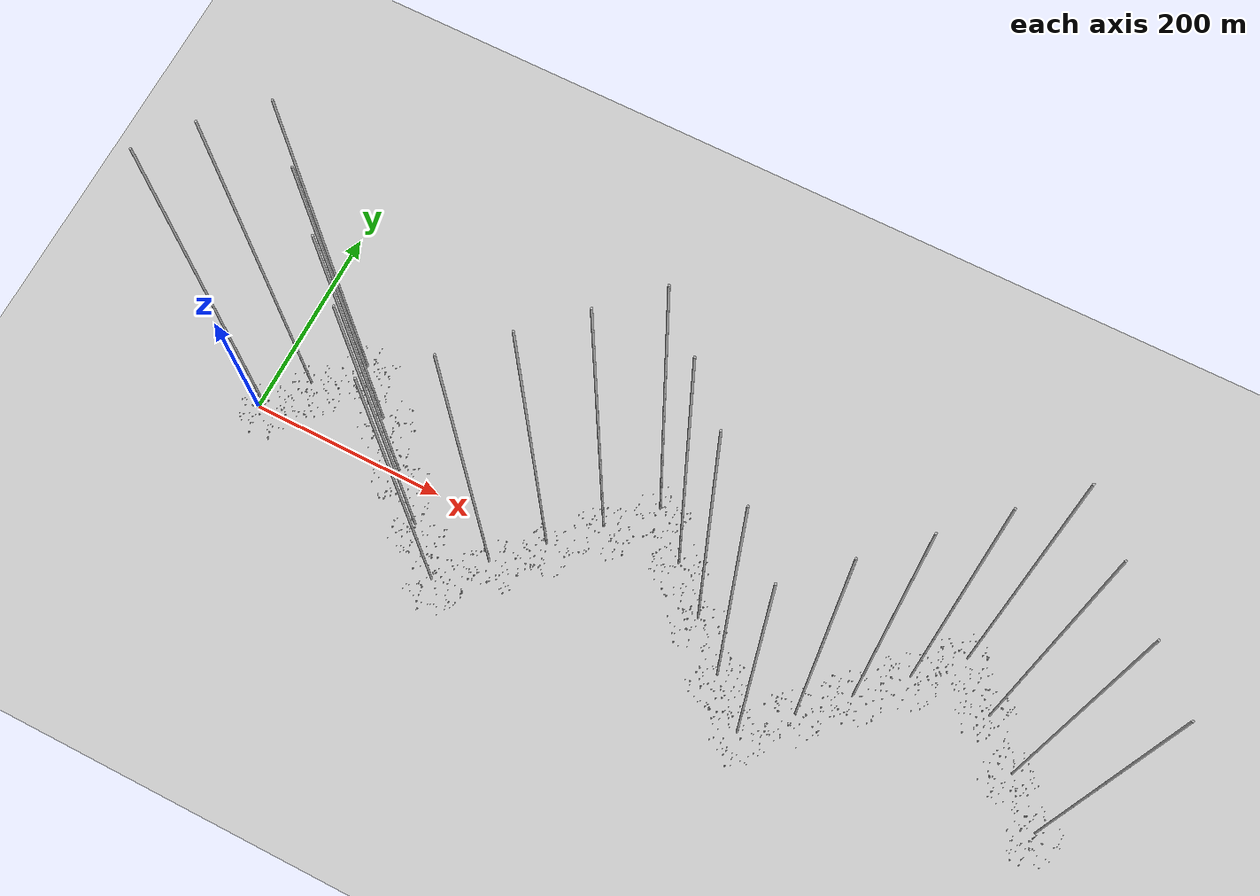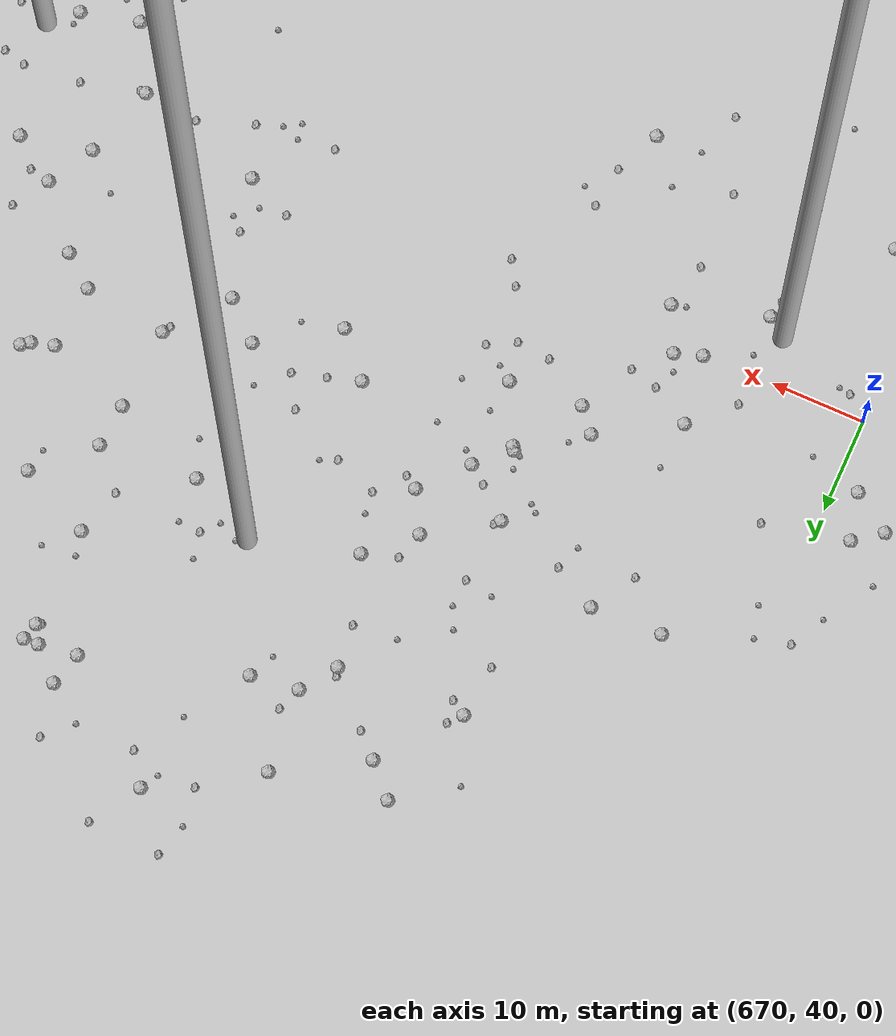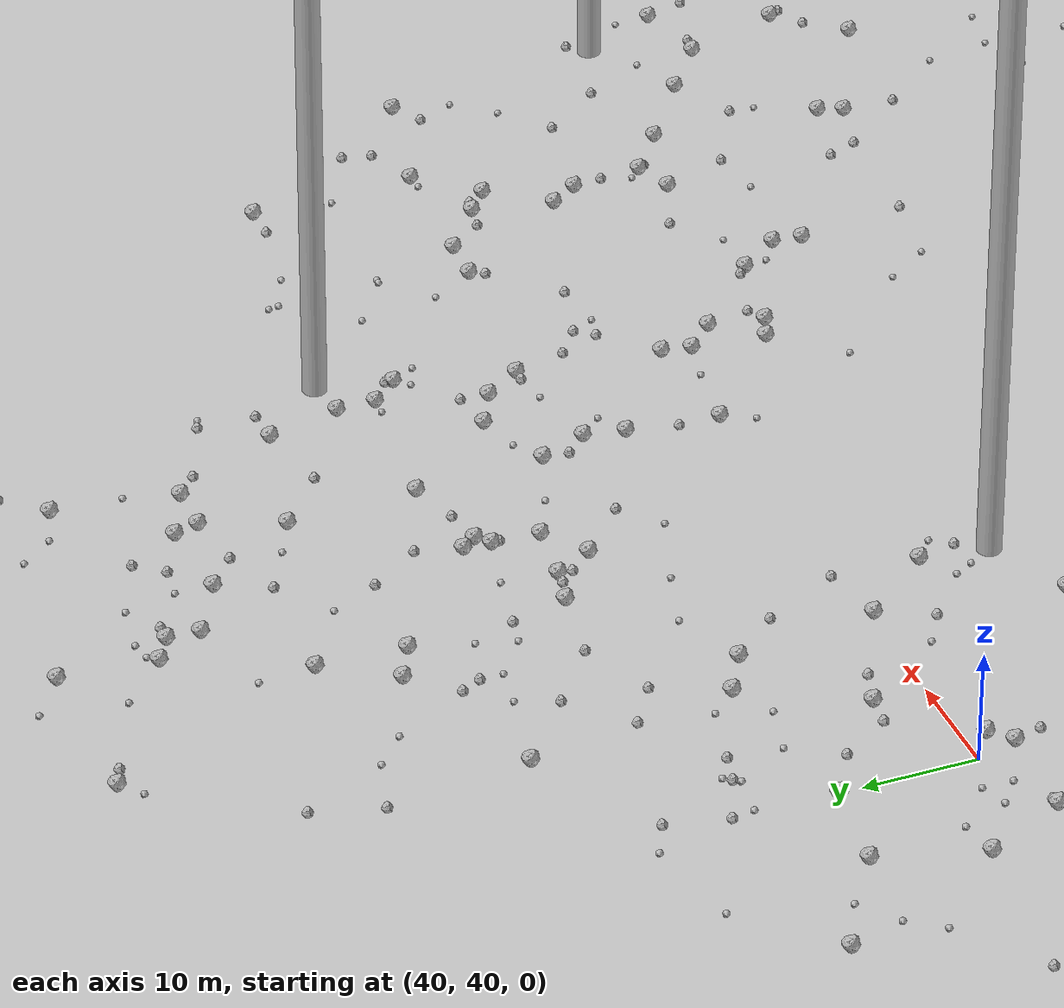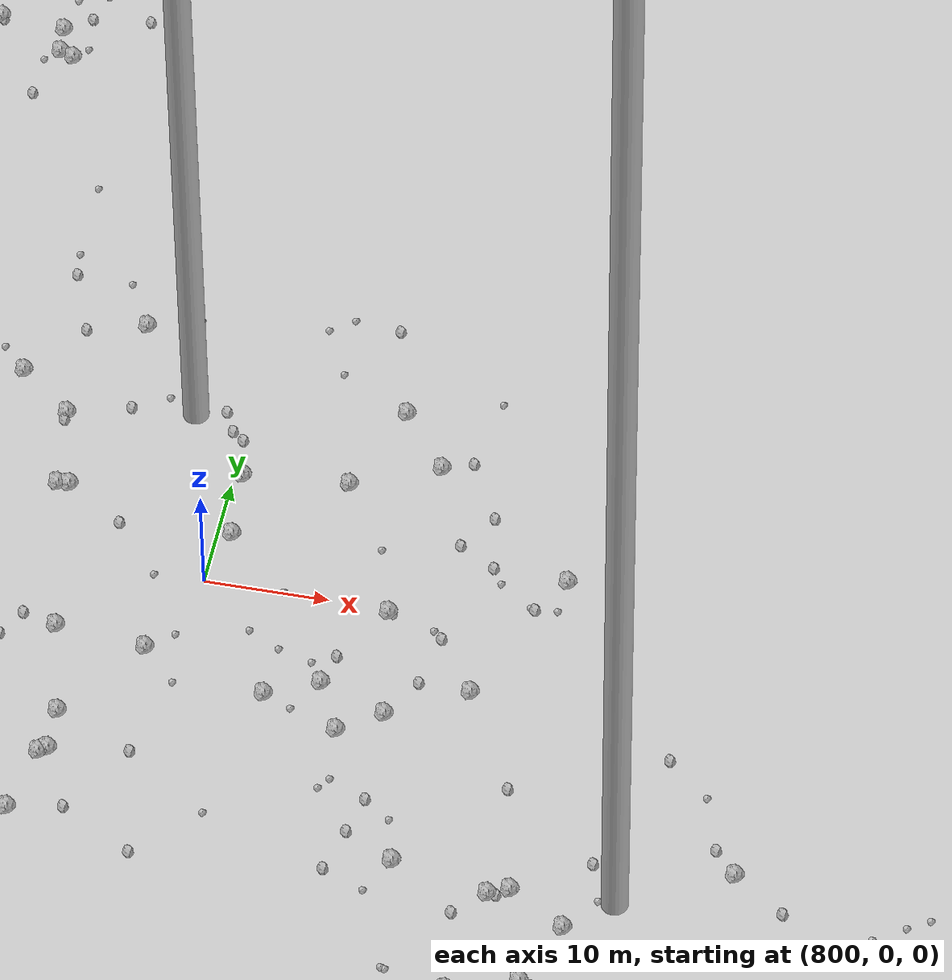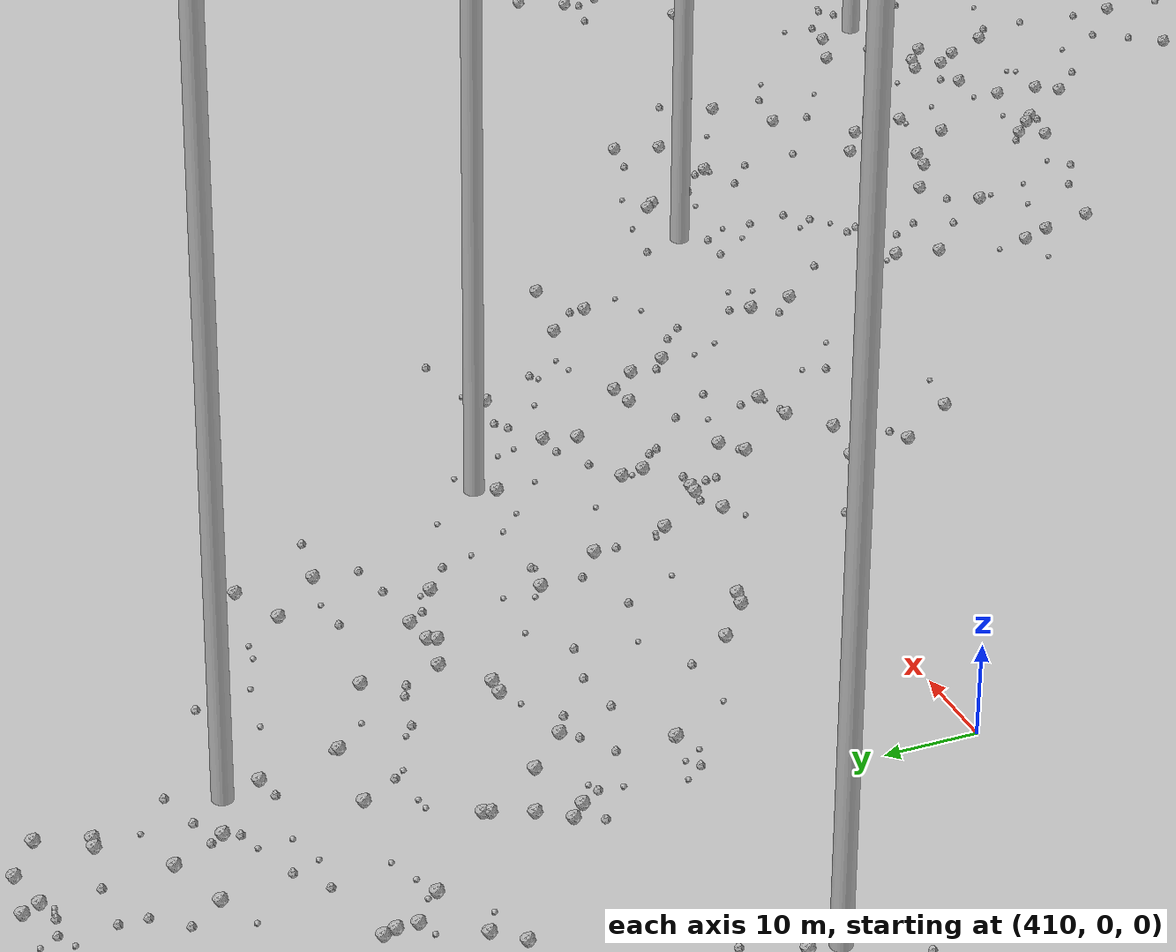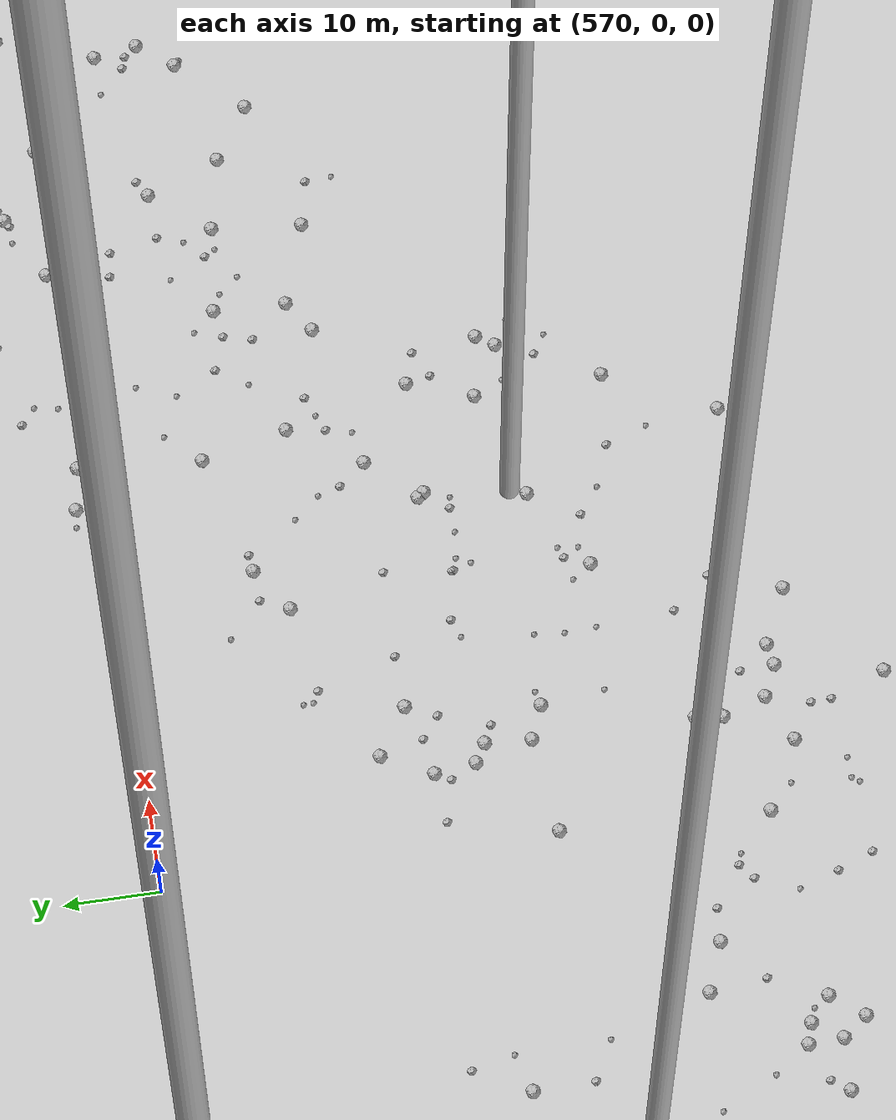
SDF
<sdf version="1.6">
 <world name="default">
  <include><uri>model://custom_ground</uri></include>
  <include><uri>model://sun</uri></include>
  <spherical_coordinates>
   <surface_model>EARTH_WGS84</surface_model>
   <latitude_deg>38.161479</latitude_deg>
   <longitude_deg>-122.454630</longitude_deg>
   <elevation>488.0</elevation>
   <heading_deg>90</heading_deg>
  </spherical_coordinates>
  <model name="rock1_0_0">
   <include><uri>model://rock1</uri><pose>-11.422423888568765 -17.45653633101054 0.5 0 0 0</pose></include>
  </model>
  <model name="rock1_0_1">
   <include><uri>model://rock1</uri><pose>21.29511063957643 7.028700530528809 0.5 0 0 0</pose></include>
  </model>
  <model name="rock1_0_2">
   <include><uri>model://rock1</uri><pose>18.90197504746974 1.9762546307096542 0.5 0 0 0</pose></include>
  </model>
  <model name="rock1_0_3">
   <include><uri>model://rock1</uri><pose>23.904759138559633 -23.740370525213148 0.5 0 0 0</pose></include>
  </model>
  <model name="rock1_0_4">
   <include><uri>model://rock1</uri><pose>27.35598047755287 4.094462015385709 0.5 0 0 0</pose></include>
  </model>
  <model name="rock1_0_5">
   <include><uri>model://rock1</uri><pose>-0.43154104800614235 -11.393826660500231 0.5 0 0 0</pose></include>
  </model>
  <model name="rock1_0_6">
   <include><uri>model://rock1</uri><pose>1.5048802186944208 -18.239227362847192 0.5 0 0 0</pose></include>
  </model>
  <model name="rock1_0_7">
   <include><uri>model://rock1</uri><pose>-6.568930959049503 -1.2539234567640456 0.5 0 0 0</pose></include>
  </model>
  <model name="rock1_0_8">
   <include><uri>model://rock1</uri><pose>22.299987637143197 -18.433251413544212 0.5 0 0 0</pose></include>
  </model>
  <model name="rock1_0_9">
   <include><uri>model://rock1</uri><pose>25.089245671686115 -25.11776613250037 0.5 0 0 0</pose></include>
  </model>
  <model name="rock1_0_10">
   <include><uri>model://rock1</uri><pose>-13.02083297470648 -4.377707332972459 0.5 0 0 0</pose></include>
  </model>
  <model name="rock1_0_11">
   <include><uri>model://rock1</uri><pose>21.075777433309945 2.11489564465338 0.5 0 0 0</pose></include>
  </model>
  <model name="rock1_0_12">
   <include><uri>model://rock1</uri><pose>22.302882200145916 -11.824543901835412 0.5 0 0 0</pose></include>
  </model>
  <model name="rock1_0_13">
   <include><uri>model://rock1</uri><pose>4.096442146311293 -6.4994771152563615 0.5 0 0 0</pose></include>
  </model>
  <model name="rock1_0_14">
   <include><uri>model://rock1</uri><pose>37.99875655014054 2.3755618427558147 0.5 0 0 0</pose></include>
  </model>
  <model name="rock1_0_15">
   <include><uri>model://rock1</uri><pose>22.33461778184487 9.78849343791191 0.5 0 0 0</pose></include>
  </model>
  <model name="rock1_0_16">
   <include><uri>model://rock1</uri><pose>18.115247521884484 10.569810243179688 0.5 0 0 0</pose></include>
  </model>
  <model name="rock1_0_17">
   <include><uri>model://rock1</uri><pose>-6.979055204974333 9.604320161331742 0.5 0 0 0</pose></include>
  </model>
  <model name="rock1_0_18">
   <include><uri>model://rock1</uri><pose>-16.991445342473416 1.7621251893038625 0.5 0 0 0</pose></include>
  </model>
  <model name="rock1_0_19">
   <include><uri>model://rock1</uri><pose>-11.226330479964847 20.502197814193806 0.5 0 0 0</pose></include>
  </model>
  <model name="rock1_0_20">
   <include><uri>model://rock1</uri><pose>-18.53074277306324 -0.829795608528368 0.5 0 0 0</pose></include>
  </model>
  <model name="rock1_0_21">
   <include><uri>model://rock1</uri><pose>-10.729988659180991 11.714281617839944 0.5 0 0 0</pose></include>
  </model>
  <model name="rock1_0_22">
   <include><uri>model://rock1</uri><pose>5.062383608551009 9.399847297263122 0.5 0 0 0</pose></include>
  </model>
  <model name="rock1_0_23">
   <include><uri>model://rock1</uri><pose>-9.572850426425783 -13.073966765319703 0.5 0 0 0</pose></include>
  </model>
  <model name="rock1_0_24">
   <include><uri>model://rock1</uri><pose>4.570803721416485 -27.24168480987268 0.5 0 0 0</pose></include>
  </model>
  <model name="rock1_0_25">
   <include><uri>model://rock1</uri><pose>3.335997369261129 -17.057339482379714 0.5 0 0 0</pose></include>
  </model>
  <model name="rock1_0_26">
   <include><uri>model://rock1</uri><pose>-5.641910765876851 -1.6284841010343598 0.5 0 0 0</pose></include>
  </model>
  <model name="rock2_0_0">
   <include><uri>model://rock2</uri><pose>-14.795966836213063 13.473840195143566 0.3 0 0 0</pose></include>
  </model>
  <model name="rock2_0_1">
   <include><uri>model://rock2</uri><pose>33.33357503447475 11.83070845017155 0.3 0 0 0</pose></include>
  </model>
  <model name="rock2_0_2">
   <include><uri>model://rock2</uri><pose>9.886727955150345 -27.71504935978107 0.3 0 0 0</pose></include>
  </model>
  <model name="rock2_0_3">
   <include><uri>model://rock2</uri><pose>-1.8920495503149262 -16.707963876040562 0.3 0 0 0</pose></include>
  </model>
  <model name="rock2_0_4">
   <include><uri>model://rock2</uri><pose>18.839104132591316 -1.2931808057941083 0.3 0 0 0</pose></include>
  </model>
  <model name="rock2_0_5">
   <include><uri>model://rock2</uri><pose>32.72237677885481 -8.983279314566445 0.3 0 0 0</pose></include>
  </model>
  <model name="rock2_0_6">
   <include><uri>model://rock2</uri><pose>19.609583591279275 -10.531477998621597 0.3 0 0 0</pose></include>
  </model>
  <model name="rock2_0_7">
   <include><uri>model://rock2</uri><pose>17.589936067342897 -12.335917428208457 0.3 0 0 0</pose></include>
  </model>
  <model name="rock2_0_8">
   <include><uri>model://rock2</uri><pose>18.674841870931118 18.14584031728993 0.3 0 0 0</pose></include>
  </model>
  <model name="rock2_0_9">
   <include><uri>model://rock2</uri><pose>7.589929846303608 28.629263281706542 0.3 0 0 0</pose></include>
  </model>
  <model name="rock2_0_10">
   <include><uri>model://rock2</uri><pose>3.9212329497730956 4.990401667515997 0.3 0 0 0</pose></include>
  </model>
  <model name="rock2_0_11">
   <include><uri>model://rock2</uri><pose>-13.86655170982083 -14.103359871072588 0.3 0 0 0</pose></include>
  </model>
  <model name="rock2_0_12">
   <include><uri>model://rock2</uri><pose>-9.086062877194522 13.251051951480086 0.3 0 0 0</pose></include>
  </model>
  <model name="rock2_0_13">
   <include><uri>model://rock2</uri><pose>14.01130624874363 26.360398216439542 0.3 0 0 0</pose></include>
  </model>
  <model name="rock2_0_14">
   <include><uri>model://rock2</uri><pose>4.8063555141060945 -6.565810468326788 0.3 0 0 0</pose></include>
  </model>
  <model name="rock2_0_15">
   <include><uri>model://rock2</uri><pose>20.877337114464048 15.93515967297914 0.3 0 0 0</pose></include>
  </model>
  <model name="rock2_0_16">
   <include><uri>model://rock2</uri><pose>25.006043575253734 7.009424857807474 0.3 0 0 0</pose></include>
  </model>
  <model name="rock2_0_17">
   <include><uri>model://rock2</uri><pose>31.665367741141793 11.659455462707776 0.3 0 0 0</pose></include>
  </model>
  <model name="rock2_0_18">
   <include><uri>model://rock2</uri><pose>-14.6460279500564 1.316855790210706 0.3 0 0 0</pose></include>
  </model>
  <model name="rock2_0_19">
   <include><uri>model://rock2</uri><pose>17.137182894728916 -3.9296160048041244 0.3 0 0 0</pose></include>
  </model>
  <model name="rock2_0_20">
   <include><uri>model://rock2</uri><pose>12.8099785089616 18.195548403789182 0.3 0 0 0</pose></include>
  </model>
  <model name="rock2_0_21">
   <include><uri>model://rock2</uri><pose>8.321747116880221 22.3062997122856 0.3 0 0 0</pose></include>
  </model>
  <model name="rock2_0_22">
   <include><uri>model://rock2</uri><pose>-5.3522457006533575 -9.934176551140279 0.3 0 0 0</pose></include>
  </model>
  <model name="rock2_0_23">
   <include><uri>model://rock2</uri><pose>6.6889818469903695 0.1554803210774942 0.3 0 0 0</pose></include>
  </model>
  <model name="rock2_0_24">
   <include><uri>model://rock2</uri><pose>-8.787995471852712 -19.695665179855652 0.3 0 0 0</pose></include>
  </model>
  <model name="rock2_0_25">
   <include><uri>model://rock2</uri><pose>-8.723950658191804 5.935528242038259 0.3 0 0 0</pose></include>
  </model>
  <model name="rock2_0_26">
   <include><uri>model://rock2</uri><pose>-8.55203846838452 11.97660590289432 0.3 0 0 0</pose></include>
  </model>
  <model name="rock3_0_0">
   <include><uri>model://rock3</uri><pose>11.600917251244429 -10.664968413043187 0.2 0 0 0</pose></include>
  </model>
  <model name="rock3_0_1">
   <include><uri>model://rock3</uri><pose>-9.999675906613774 -14.420293324235585 0.2 0 0 0</pose></include>
  </model>
  <model name="rock3_0_2">
   <include><uri>model://rock3</uri><pose>12.085326698453265 11.199673688135313 0.2 0 0 0</pose></include>
  </model>
  <model name="rock3_0_3">
   <include><uri>model://rock3</uri><pose>12.836567297247328 -27.779343836853034 0.2 0 0 0</pose></include>
  </model>
  <model name="rock3_0_4">
   <include><uri>model://rock3</uri><pose>-9.44324231934436 -17.386103856414067 0.2 0 0 0</pose></include>
  </model>
  <model name="rock3_0_5">
   <include><uri>model://rock3</uri><pose>19.10493584067676 -17.137663188881895 0.2 0 0 0</pose></include>
  </model>
  <model name="rock3_0_6">
   <include><uri>model://rock3</uri><pose>13.09800177222877 -19.35196003471509 0.2 0 0 0</pose></include>
  </model>
  <model name="rock3_0_7">
   <include><uri>model://rock3</uri><pose>21.715891274960853 24.8793692326202 0.2 0 0 0</pose></include>
  </model>
  <model name="rock3_0_8">
   <include><uri>model://rock3</uri><pose>16.19531016059912 6.56972005047016 0.2 0 0 0</pose></include>
  </model>
  <model name="rock3_0_9">
   <include><uri>model://rock3</uri><pose>0.8627414381615282 11.229692996740198 0.2 0 0 0</pose></include>
  </model>
  <model name="rock3_0_10">
   <include><uri>model://rock3</uri><pose>2.4824844236576773 -12.506827804465349 0.2 0 0 0</pose></include>
  </model>
  <model name="rock3_0_11">
   <include><uri>model://rock3</uri><pose>13.632923764449387 -29.553744460491444 0.2 0 0 0</pose></include>
  </model>
  <model name="rock3_0_12">
   <include><uri>model://rock3</uri><pose>-1.4311172081411065 -11.67921113316601 0.2 0 0 0</pose></include>
  </model>
  <model name="rock3_0_13">
   <include><uri>model://rock3</uri><pose>15.67745653126859 -10.329568467996598 0.2 0 0 0</pose></include>
  </model>
  <model name="rock3_0_14">
   <include><uri>model://rock3</uri><pose>1.0029522082294697 -8.673941565927084 0.2 0 0 0</pose></include>
  </model>
  <model name="rock3_0_15">
   <include><uri>model://rock3</uri><pose>37.568483406740526 7.9363157776881295 0.2 0 0 0</pose></include>
  </model>
  <model name="rock3_0_16">
   <include><uri>model://rock3</uri><pose>6.478222945080606 -27.110986703567235 0.2 0 0 0</pose></include>
  </model>
  <model name="rock3_0_17">
   <include><uri>model://rock3</uri><pose>28.13750288366601 -10.279115504804835 0.2 0 0 0</pose></include>
  </model>
  <model name="rock3_0_18">
   <include><uri>model://rock3</uri><pose>-6.833633167820546 10.507223299432404 0.2 0 0 0</pose></include>
  </model>
  <model name="rock3_0_19">
   <include><uri>model://rock3</uri><pose>8.624912575508205 21.611723181876485 0.2 0 0 0</pose></include>
  </model>
  <model name="rock3_0_20">
   <include><uri>model://rock3</uri><pose>-3.880948586797782 4.8860987559123075 0.2 0 0 0</pose></include>
  </model>
  <model name="rock3_0_21">
   <include><uri>model://rock3</uri><pose>8.22817978241461 26.50506201456949 0.2 0 0 0</pose></include>
  </model>
  <model name="rock3_0_22">
   <include><uri>model://rock3</uri><pose>9.168746572811543 -19.477582256037344 0.2 0 0 0</pose></include>
  </model>
  <model name="rock3_0_23">
   <include><uri>model://rock3</uri><pose>-5.419986338891203 15.895938095707379 0.2 0 0 0</pose></include>
  </model>
  <model name="rock3_0_24">
   <include><uri>model://rock3</uri><pose>14.594233181515968 20.017622331089896 0.2 0 0 0</pose></include>
  </model>
  <model name="rock3_0_25">
   <include><uri>model://rock3</uri><pose>16.88645551952245 16.79058139716141 0.2 0 0 0</pose></include>
  </model>
  <model name="rock3_0_26">
   <include><uri>model://rock3</uri><pose>2.5937627115383357 10.340736477874216 0.2 0 0 0</pose></include>
  </model>
  <model name="rock1_1_0">
   <include><uri>model://rock1</uri><pose>31.465373938497454 53.3157043054967 0.5 0 0 0</pose></include>
  </model>
  <model name="rock1_1_1">
   <include><uri>model://rock1</uri><pose>42.92803329069999 23.454880738462933 0.5 0 0 0</pose></include>
  </model>
  <model name="rock1_1_2">
   <include><uri>model://rock1</uri><pose>41.0788637951528 36.45528258655227 0.5 0 0 0</pose></include>
  </model>
  <model name="rock1_1_3">
   <include><uri>model://rock1</uri><pose>60.997949652759 39.585298631139224 0.5 0 0 0</pose></include>
  </model>
  <model name="rock1_1_4">
   <include><uri>model://rock1</uri><pose>20.106442797201517 22.508813412130664 0.5 0 0 0</pose></include>
  </model>
  <model name="rock1_1_5">
   <include><uri>model://rock1</uri><pose>66.54089774556283 33.03053498570619 0.5 0 0 0</pose></include>
  </model>
  <model name="rock1_1_6">
   <include><uri>model://rock1</uri><pose>25.0530545279704 33.5233801193076 0.5 0 0 0</pose></include>
  </model>
  <model name="rock1_1_7">
   <include><uri>model://rock1</uri><pose>29.88817138203364 31.83021782522784 0.5 0 0 0</pose></include>
  </model>
  <model name="rock1_1_8">
   <include><uri>model://rock1</uri><pose>16.408638078650405 37.12971602019397 0.5 0 0 0</pose></include>
  </model>
  <model name="rock1_1_9">
   <include><uri>model://rock1</uri><pose>47.75484578836357 19.270125523678963 0.5 0 0 0</pose></include>
  </model>
  <model name="rock1_1_10">
   <include><uri>model://rock1</uri><pose>21.447217271282824 40.71332778041018 0.5 0 0 0</pose></include>
  </model>
  <model name="rock1_1_11">
   <include><uri>model://rock1</uri><pose>58.44023364316902 23.68242214960489 0.5 0 0 0</pose></include>
  </model>
  <model name="rock1_1_12">
   <include><uri>model://rock1</uri><pose>32.74068720248522 34.628066855057234 0.5 0 0 0</pose></include>
  </model>
  <model name="rock1_1_13">
   <include><uri>model://rock1</uri><pose>59.557931960257 52.021762471866346 0.5 0 0 0</pose></include>
  </model>
  <model name="rock1_1_14">
   <include><uri>model://rock1</uri><pose>24.029787780457468 22.839610098171327 0.5 0 0 0</pose></include>
  </model>
  <model name="rock1_1_15">
   <include><uri>model://rock1</uri><pose>32.3502300067018 36.942219505463385 0.5 0 0 0</pose></include>
  </model>
  <model name="rock1_1_16">
   <include><uri>model://rock1</uri><pose>50.04793812140482 44.600271410569746 0.5 0 0 0</pose></include>
  </model>
  <model name="rock1_1_17">
   <include><uri>model://rock1</uri><pose>28.78417241448326 44.20081929371801 0.5 0 0 0</pose></include>
  </model>
  <model name="rock1_1_18">
   <include><uri>model://rock1</uri><pose>39.88798211675736 52.075886038439265 0.5 0 0 0</pose></include>
  </model>
  <model name="rock1_1_19">
   <include><uri>model://rock1</uri><pose>43.03402150578194 13.122429518579553 0.5 0 0 0</pose></include>
  </model>
  <model name="rock1_1_20">
   <include><uri>model://rock1</uri><pose>42.934610243995145 38.101213783392744 0.5 0 0 0</pose></include>
  </model>
  <model name="rock1_1_21">
   <include><uri>model://rock1</uri><pose>55.477817935261875 54.36111244224659 0.5 0 0 0</pose></include>
  </model>
  <model name="rock1_1_22">
   <include><uri>model://rock1</uri><pose>53.425297025876816 15.456914406745634 0.5 0 0 0</pose></include>
  </model>
  <model name="rock1_1_23">
   <include><uri>model://rock1</uri><pose>37.102212809691906 12.78112707558371 0.5 0 0 0</pose></include>
  </model>
  <model name="rock1_1_24">
   <include><uri>model://rock1</uri><pose>21.991827809793683 59.11230937180315 0.5 0 0 0</pose></include>
  </model>
  <model name="rock1_1_25">
   <include><uri>model://rock1</uri><pose>46.351020193468244 11.895056311981016 0.5 0 0 0</pose></include>
  </model>
  <model name="rock1_1_26">
   <include><uri>model://rock1</uri><pose>18.39590467424436 38.76656959891937 0.5 0 0 0</pose></include>
  </model>
  <model name="rock2_1_0">
   <include><uri>model://rock2</uri><pose>58.69279826777013 35.01095800143528 0.3 0 0 0</pose></include>
  </model>
  <model name="rock2_1_1">
   <include><uri>model://rock2</uri><pose>63.219385909995864 47.66129783848097 0.3 0 0 0</pose></include>
  </model>
  <model name="rock2_1_2">
   <include><uri>model://rock2</uri><pose>66.79915370632746 40.69665202138629 0.3 0 0 0</pose></include>
  </model>
  <model name="rock2_1_3">
   <include><uri>model://rock2</uri><pose>32.930834256950874 37.05022764941492 0.3 0 0 0</pose></include>
  </model>
  <model name="rock2_1_4">
   <include><uri>model://rock2</uri><pose>67.25328415791446 29.54806669819788 0.3 0 0 0</pose></include>
  </model>
  <model name="rock2_1_5">
   <include><uri>model://rock2</uri><pose>41.702231366961385 33.93026979538273 0.3 0 0 0</pose></include>
  </model>
  <model name="rock2_1_6">
   <include><uri>model://rock2</uri><pose>25.213998949797645 35.065567545396775 0.3 0 0 0</pose></include>
  </model>
  <model name="rock2_1_7">
   <include><uri>model://rock2</uri><pose>38.309025410324054 32.08949625370045 0.3 0 0 0</pose></include>
  </model>
  <model name="rock2_1_8">
   <include><uri>model://rock2</uri><pose>59.83924377614162 21.770771291188773 0.3 0 0 0</pose></include>
  </model>
  <model name="rock2_1_9">
   <include><uri>model://rock2</uri><pose>51.740905652053286 25.339462325352557 0.3 0 0 0</pose></include>
  </model>
  <model name="rock2_1_10">
   <include><uri>model://rock2</uri><pose>44.330475083577205 27.530853331768068 0.3 0 0 0</pose></include>
  </model>
  <model name="rock2_1_11">
   <include><uri>model://rock2</uri><pose>39.895936032705755 61.05806489404621 0.3 0 0 0</pose></include>
  </model>
  <model name="rock2_1_12">
   <include><uri>model://rock2</uri><pose>53.28405390081328 43.53538405737452 0.3 0 0 0</pose></include>
  </model>
  <model name="rock2_1_13">
   <include><uri>model://rock2</uri><pose>44.43989175634673 59.05969465478566 0.3 0 0 0</pose></include>
  </model>
  <model name="rock2_1_14">
   <include><uri>model://rock2</uri><pose>13.973780886066558 46.015888668324166 0.3 0 0 0</pose></include>
  </model>
  <model name="rock2_1_15">
   <include><uri>model://rock2</uri><pose>44.17194811398533 49.46143762790028 0.3 0 0 0</pose></include>
  </model>
  <model name="rock2_1_16">
   <include><uri>model://rock2</uri><pose>17.789823288313485 38.63083605288679 0.3 0 0 0</pose></include>
  </model>
  <model name="rock2_1_17">
   <include><uri>model://rock2</uri><pose>41.14021817302083 66.40704457204818 0.3 0 0 0</pose></include>
  </model>
  <model name="rock2_1_18">
   <include><uri>model://rock2</uri><pose>42.277451715296856 10.909466184535408 0.3 0 0 0</pose></include>
  </model>
  <model name="rock2_1_19">
   <include><uri>model://rock2</uri><pose>54.147633039948374 62.99299523320991 0.3 0 0 0</pose></include>
  </model>
  <model name="rock2_1_20">
   <include><uri>model://rock2</uri><pose>38.67540544897699 28.140766171353814 0.3 0 0 0</pose></include>
  </model>
  <model name="rock2_1_21">
   <include><uri>model://rock2</uri><pose>33.98604329845379 34.416208593958885 0.3 0 0 0</pose></include>
  </model>
  <model name="rock2_1_22">
   <include><uri>model://rock2</uri><pose>28.906358312646375 14.681914742558517 0.3 0 0 0</pose></include>
  </model>
  <model name="rock2_1_23">
   <include><uri>model://rock2</uri><pose>47.276873524936086 58.31321366013633 0.3 0 0 0</pose></include>
  </model>
  <model name="rock2_1_24">
   <include><uri>model://rock2</uri><pose>27.005792028198805 21.41521446142435 0.3 0 0 0</pose></include>
  </model>
  <model name="rock2_1_25">
   <include><uri>model://rock2</uri><pose>47.12468751348337 44.97696350550599 0.3 0 0 0</pose></include>
  </model>
  <model name="rock2_1_26">
   <include><uri>model://rock2</uri><pose>24.09512892275486 22.47026062614868 0.3 0 0 0</pose></include>
  </model>
  <model name="rock3_1_0">
   <include><uri>model://rock3</uri><pose>21.22284537157486 51.26167464162477 0.2 0 0 0</pose></include>
  </model>
  <model name="rock3_1_1">
   <include><uri>model://rock3</uri><pose>26.620741816812046 56.67532071277305 0.2 0 0 0</pose></include>
  </model>
  <model name="rock3_1_2">
   <include><uri>model://rock3</uri><pose>32.27234427513855 44.724936110077756 0.2 0 0 0</pose></include>
  </model>
  <model name="rock3_1_3">
   <include><uri>model://rock3</uri><pose>45.03395789600574 59.63733909076771 0.2 0 0 0</pose></include>
  </model>
  <model name="rock3_1_4">
   <include><uri>model://rock3</uri><pose>23.333544659102056 54.14605118664483 0.2 0 0 0</pose></include>
  </model>
  <model name="rock3_1_5">
   <include><uri>model://rock3</uri><pose>40.33143408732873 58.9785342271433 0.2 0 0 0</pose></include>
  </model>
  <model name="rock3_1_6">
   <include><uri>model://rock3</uri><pose>55.57590534387806 36.88212897403271 0.2 0 0 0</pose></include>
  </model>
  <model name="rock3_1_7">
   <include><uri>model://rock3</uri><pose>44.12105042937494 13.646455249710094 0.2 0 0 0</pose></include>
  </model>
  <model name="rock3_1_8">
   <include><uri>model://rock3</uri><pose>64.35765803827817 29.322875209084042 0.2 0 0 0</pose></include>
  </model>
  <model name="rock3_1_9">
   <include><uri>model://rock3</uri><pose>68.55505120196106 31.199721013485725 0.2 0 0 0</pose></include>
  </model>
  <model name="rock3_1_10">
   <include><uri>model://rock3</uri><pose>36.27423229712055 38.78428277423038 0.2 0 0 0</pose></include>
  </model>
  <model name="rock3_1_11">
   <include><uri>model://rock3</uri><pose>44.12916461191606 58.40285502635419 0.2 0 0 0</pose></include>
  </model>
  <model name="rock3_1_12">
   <include><uri>model://rock3</uri><pose>65.78307512376655 54.44841003597725 0.2 0 0 0</pose></include>
  </model>
  <model name="rock3_1_13">
   <include><uri>model://rock3</uri><pose>46.878232950366524 53.63089682688421 0.2 0 0 0</pose></include>
  </model>
  <model name="rock3_1_14">
   <include><uri>model://rock3</uri><pose>63.381656605258094 31.05112269001831 0.2 0 0 0</pose></include>
  </model>
  <model name="rock3_1_15">
   <include><uri>model://rock3</uri><pose>20.989802827203633 26.745893642984445 0.2 0 0 0</pose></include>
  </model>
  <model name="rock3_1_16">
   <include><uri>model://rock3</uri><pose>38.018061624655395 67.90825489797407 0.2 0 0 0</pose></include>
  </model>
  <model name="rock3_1_17">
   <include><uri>model://rock3</uri><pose>53.26360477450118 17.83306577858449 0.2 0 0 0</pose></include>
  </model>
  <model name="rock3_1_18">
   <include><uri>model://rock3</uri><pose>51.63094547351288 52.411823458755066 0.2 0 0 0</pose></include>
  </model>
  <model name="rock3_1_19">
   <include><uri>model://rock3</uri><pose>20.84696924557383 17.768363292374552 0.2 0 0 0</pose></include>
  </model>
  <model name="rock3_1_20">
   <include><uri>model://rock3</uri><pose>18.337225500982797 23.793543806278556 0.2 0 0 0</pose></include>
  </model>
  <model name="rock3_1_21">
   <include><uri>model://rock3</uri><pose>41.81141326060745 16.15495729045267 0.2 0 0 0</pose></include>
  </model>
  <model name="rock3_1_22">
   <include><uri>model://rock3</uri><pose>29.160270085034185 66.16086465738812 0.2 0 0 0</pose></include>
  </model>
  <model name="rock3_1_23">
   <include><uri>model://rock3</uri><pose>33.903152451163265 40.6108610237467 0.2 0 0 0</pose></include>
  </model>
  <model name="rock3_1_24">
   <include><uri>model://rock3</uri><pose>53.08841330918215 56.76221870341578 0.2 0 0 0</pose></include>
  </model>
  <model name="rock3_1_25">
   <include><uri>model://rock3</uri><pose>36.33874285839945 41.43929801688422 0.2 0 0 0</pose></include>
  </model>
  <model name="rock3_1_26">
   <include><uri>model://rock3</uri><pose>26.203332792556093 31.54922446643146 0.2 0 0 0</pose></include>
  </model>
  <model name="rock1_2_0">
   <include><uri>model://rock1</uri><pose>81.54506123056231 64.42865817759953 0.5 0 0 0</pose></include>
  </model>
  <model name="rock1_2_1">
   <include><uri>model://rock1</uri><pose>77.46080999009351 57.55836576707267 0.5 0 0 0</pose></include>
  </model>
  <model name="rock1_2_2">
   <include><uri>model://rock1</uri><pose>66.89026659315573 77.86086660818091 0.5 0 0 0</pose></include>
  </model>
  <model name="rock1_2_3">
   <include><uri>model://rock1</uri><pose>81.29975668253516 60.21473447947379 0.5 0 0 0</pose></include>
  </model>
  <model name="rock1_2_4">
   <include><uri>model://rock1</uri><pose>102.93276917655037 75.72457809439146 0.5 0 0 0</pose></include>
  </model>
  <model name="rock1_2_5">
   <include><uri>model://rock1</uri><pose>84.39316386888586 87.48904184423436 0.5 0 0 0</pose></include>
  </model>
  <model name="rock1_2_6">
   <include><uri>model://rock1</uri><pose>90.4956075973125 78.80531077358228 0.5 0 0 0</pose></include>
  </model>
  <model name="rock1_2_7">
   <include><uri>model://rock1</uri><pose>82.75238840276708 65.45173449248274 0.5 0 0 0</pose></include>
  </model>
  <model name="rock1_2_8">
   <include><uri>model://rock1</uri><pose>78.87555923660298 93.4848886694181 0.5 0 0 0</pose></include>
  </model>
  <model name="rock1_2_9">
   <include><uri>model://rock1</uri><pose>91.54027180435045 55.84574931806746 0.5 0 0 0</pose></include>
  </model>
  <model name="rock1_2_10">
   <include><uri>model://rock1</uri><pose>93.10180920617202 85.65978376145016 0.5 0 0 0</pose></include>
  </model>
  <model name="rock1_2_11">
   <include><uri>model://rock1</uri><pose>78.74736180904462 90.59334639184542 0.5 0 0 0</pose></include>
  </model>
  <model name="rock1_2_12">
   <include><uri>model://rock1</uri><pose>104.57322722180282 65.69797776708194 0.5 0 0 0</pose></include>
  </model>
  <model name="rock1_2_13">
   <include><uri>model://rock1</uri><pose>71.97737102680648 61.84161378749049 0.5 0 0 0</pose></include>
  </model>
  <model name="rock1_2_14">
   <include><uri>model://rock1</uri><pose>70.83159080491792 83.78680970223353 0.5 0 0 0</pose></include>
  </model>
  <model name="rock1_2_15">
   <include><uri>model://rock1</uri><pose>61.897276928738805 103.57540127275398 0.5 0 0 0</pose></include>
  </model>
  <model name="rock1_2_16">
   <include><uri>model://rock1</uri><pose>90.97075753219549 67.32855183016162 0.5 0 0 0</pose></include>
  </model>
  <model name="rock1_2_17">
   <include><uri>model://rock1</uri><pose>70.51303476354921 76.03363422556261 0.5 0 0 0</pose></include>
  </model>
  <model name="rock1_2_18">
   <include><uri>model://rock1</uri><pose>81.71561353216725 66.82179467872757 0.5 0 0 0</pose></include>
  </model>
  <model name="rock1_2_19">
   <include><uri>model://rock1</uri><pose>76.29324449661239 94.98165402095012 0.5 0 0 0</pose></include>
  </model>
  <model name="rock1_2_20">
   <include><uri>model://rock1</uri><pose>52.80503913779584 72.62910763636984 0.5 0 0 0</pose></include>
  </model>
  <model name="rock1_2_21">
   <include><uri>model://rock1</uri><pose>75.57731350189239 61.016502452254045 0.5 0 0 0</pose></include>
  </model>
  <model name="rock1_2_22">
   <include><uri>model://rock1</uri><pose>104.55761601157988 69.14892128685977 0.5 0 0 0</pose></include>
  </model>
  <model name="rock1_2_23">
   <include><uri>model://rock1</uri><pose>92.39589209338772 87.90298768717872 0.5 0 0 0</pose></include>
  </model>
  <model name="rock1_2_24">
   <include><uri>model://rock1</uri><pose>99.30828346041139 96.30682554367743 0.5 0 0 0</pose></include>
  </model>
  <model name="rock1_2_25">
   <include><uri>model://rock1</uri><pose>97.60743199421343 85.54397582183532 0.5 0 0 0</pose></include>
  </model>
  <model name="rock1_2_26">
   <include><uri>model://rock1</uri><pose>76.97581001036563 103.36354188818288 0.5 0 0 0</pose></include>
  </model>
  <model name="rock2_2_0">
   <include><uri>model://rock2</uri><pose>51.15953449005507 85.22891554225322 0.3 0 0 0</pose></include>
  </model>
  <model name="rock2_2_1">
   <include><uri>model://rock2</uri><pose>79.47511493569564 75.32405083175735 0.3 0 0 0</pose></include>
  </model>
  <model name="rock2_2_2">
   <include><uri>model://rock2</uri><pose>80.34899717382517 93.41121441604659 0.3 0 0 0</pose></include>
  </model>
  <model name="rock2_2_3">
   <include><uri>model://rock2</uri><pose>91.23480894483964 53.54526920067654 0.3 0 0 0</pose></include>
  </model>
  <model name="rock2_2_4">
   <include><uri>model://rock2</uri><pose>63.657432085967045 102.74455822690665 0.3 0 0 0</pose></include>
  </model>
  <model name="rock2_2_5">
   <include><uri>model://rock2</uri><pose>59.06704455517625 67.47557882877514 0.3 0 0 0</pose></include>
  </model>
  <model name="rock2_2_6">
   <include><uri>model://rock2</uri><pose>106.03352862777228 75.8032844901324 0.3 0 0 0</pose></include>
  </model>
  <model name="rock2_2_7">
   <include><uri>model://rock2</uri><pose>99.63647582378613 83.67963783880006 0.3 0 0 0</pose></include>
  </model>
  <model name="rock2_2_8">
   <include><uri>model://rock2</uri><pose>95.69130435963115 74.46297178850575 0.3 0 0 0</pose></include>
  </model>
  <model name="rock2_2_9">
   <include><uri>model://rock2</uri><pose>82.2056775179835 83.04458542350089 0.3 0 0 0</pose></include>
  </model>
  <model name="rock2_2_10">
   <include><uri>model://rock2</uri><pose>81.5290051808875 63.698264440320266 0.3 0 0 0</pose></include>
  </model>
  <model name="rock2_2_11">
   <include><uri>model://rock2</uri><pose>106.25480860522978 80.92001191786801 0.3 0 0 0</pose></include>
  </model>
  <model name="rock2_2_12">
   <include><uri>model://rock2</uri><pose>52.84945425251011 91.16026649685054 0.3 0 0 0</pose></include>
  </model>
  <model name="rock2_2_13">
   <include><uri>model://rock2</uri><pose>74.17474964026445 61.1341616694546 0.3 0 0 0</pose></include>
  </model>
  <model name="rock2_2_14">
   <include><uri>model://rock2</uri><pose>82.20143952138037 53.13732625696582 0.3 0 0 0</pose></include>
  </model>
  <model name="rock2_2_15">
   <include><uri>model://rock2</uri><pose>63.2464604979988 74.14166654191928 0.3 0 0 0</pose></include>
  </model>
  <model name="rock2_2_16">
   <include><uri>model://rock2</uri><pose>87.48688103066002 90.27387819848171 0.3 0 0 0</pose></include>
  </model>
  <model name="rock2_2_17">
   <include><uri>model://rock2</uri><pose>64.70318497224726 63.096170995916715 0.3 0 0 0</pose></include>
  </model>
  <model name="rock2_2_18">
   <include><uri>model://rock2</uri><pose>64.17659837921154 72.3339483879461 0.3 0 0 0</pose></include>
  </model>
  <model name="rock2_2_19">
   <include><uri>model://rock2</uri><pose>82.70824355548562 70.69591575381305 0.3 0 0 0</pose></include>
  </model>
  <model name="rock2_2_20">
   <include><uri>model://rock2</uri><pose>89.3845777044257 92.63764435827255 0.3 0 0 0</pose></include>
  </model>
  <model name="rock2_2_21">
   <include><uri>model://rock2</uri><pose>58.13846473005846 60.40229629437257 0.3 0 0 0</pose></include>
  </model>
  <model name="rock2_2_22">
   <include><uri>model://rock2</uri><pose>70.52014773403923 66.93600401876293 0.3 0 0 0</pose></include>
  </model>
  <model name="rock2_2_23">
   <include><uri>model://rock2</uri><pose>75.37185165242005 59.77578366028182 0.3 0 0 0</pose></include>
  </model>
  <model name="rock2_2_24">
   <include><uri>model://rock2</uri><pose>87.42099650425463 84.9144975754914 0.3 0 0 0</pose></include>
  </model>
  <model name="rock2_2_25">
   <include><uri>model://rock2</uri><pose>102.39640480444703 99.72205130612062 0.3 0 0 0</pose></include>
  </model>
  <model name="rock2_2_26">
   <include><uri>model://rock2</uri><pose>86.23944539720551 66.00725326118007 0.3 0 0 0</pose></include>
  </model>
  <model name="rock3_2_0">
   <include><uri>model://rock3</uri><pose>95.34381930498826 97.63026318670788 0.2 0 0 0</pose></include>
  </model>
  <model name="rock3_2_1">
   <include><uri>model://rock3</uri><pose>94.13266577931876 57.35102620074357 0.2 0 0 0</pose></include>
  </model>
  <model name="rock3_2_2">
   <include><uri>model://rock3</uri><pose>68.97000049160786 70.77049566422883 0.2 0 0 0</pose></include>
  </model>
  <model name="rock3_2_3">
   <include><uri>model://rock3</uri><pose>70.41916630777335 88.63875632152076 0.2 0 0 0</pose></include>
  </model>
  <model name="rock3_2_4">
   <include><uri>model://rock3</uri><pose>68.03343832696447 67.42608564513556 0.2 0 0 0</pose></include>
  </model>
  <model name="rock3_2_5">
   <include><uri>model://rock3</uri><pose>102.88357277865848 65.67845355755756 0.2 0 0 0</pose></include>
  </model>
  <model name="rock3_2_6">
   <include><uri>model://rock3</uri><pose>83.50058059349311 95.21094147849271 0.2 0 0 0</pose></include>
  </model>
  <model name="rock3_2_7">
   <include><uri>model://rock3</uri><pose>98.91862576215834 90.05076258575991 0.2 0 0 0</pose></include>
  </model>
  <model name="rock3_2_8">
   <include><uri>model://rock3</uri><pose>64.29414637231153 70.21424615197495 0.2 0 0 0</pose></include>
  </model>
  <model name="rock3_2_9">
   <include><uri>model://rock3</uri><pose>71.55406481048803 52.709312801091215 0.2 0 0 0</pose></include>
  </model>
  <model name="rock3_2_10">
   <include><uri>model://rock3</uri><pose>77.24361853425484 108.5414359531612 0.2 0 0 0</pose></include>
  </model>
  <model name="rock3_2_11">
   <include><uri>model://rock3</uri><pose>77.01788191227652 95.70902990236061 0.2 0 0 0</pose></include>
  </model>
  <model name="rock3_2_12">
   <include><uri>model://rock3</uri><pose>85.601410170595 57.948656770400845 0.2 0 0 0</pose></include>
  </model>
  <model name="rock3_2_13">
   <include><uri>model://rock3</uri><pose>76.0648783018534 65.72484499891237 0.2 0 0 0</pose></include>
  </model>
  <model name="rock3_2_14">
   <include><uri>model://rock3</uri><pose>107.45253993907335 80.41987340111956 0.2 0 0 0</pose></include>
  </model>
  <model name="rock3_2_15">
   <include><uri>model://rock3</uri><pose>78.86009871021022 50.147600851157165 0.2 0 0 0</pose></include>
  </model>
  <model name="rock3_2_16">
   <include><uri>model://rock3</uri><pose>77.42110488924813 79.6132758319855 0.2 0 0 0</pose></include>
  </model>
  <model name="rock3_2_17">
   <include><uri>model://rock3</uri><pose>93.04355783087844 100.5606875453297 0.2 0 0 0</pose></include>
  </model>
  <model name="rock3_2_18">
   <include><uri>model://rock3</uri><pose>71.7402486545628 99.06456632088421 0.2 0 0 0</pose></include>
  </model>
  <model name="rock3_2_19">
   <include><uri>model://rock3</uri><pose>56.622712691974385 83.54608836083167 0.2 0 0 0</pose></include>
  </model>
  <model name="rock3_2_20">
   <include><uri>model://rock3</uri><pose>84.50989440975447 90.65305323372334 0.2 0 0 0</pose></include>
  </model>
  <model name="rock3_2_21">
   <include><uri>model://rock3</uri><pose>72.74704927872338 106.18058877819387 0.2 0 0 0</pose></include>
  </model>
  <model name="rock3_2_22">
   <include><uri>model://rock3</uri><pose>86.71570200909855 80.58875192206337 0.2 0 0 0</pose></include>
  </model>
  <model name="rock3_2_23">
   <include><uri>model://rock3</uri><pose>60.51203117529664 70.85996675917545 0.2 0 0 0</pose></include>
  </model>
  <model name="rock3_2_24">
   <include><uri>model://rock3</uri><pose>78.87647431007699 96.02747594157282 0.2 0 0 0</pose></include>
  </model>
  <model name="rock3_2_25">
   <include><uri>model://rock3</uri><pose>59.58213241215821 80.91074379347157 0.2 0 0 0</pose></include>
  </model>
  <model name="rock3_2_26">
   <include><uri>model://rock3</uri><pose>59.97306634183434 101.95467176362087 0.2 0 0 0</pose></include>
  </model>
  <model name="rock1_3_0">
   <include><uri>model://rock1</uri><pose>128.05914163932005 39.92646845954289 0.5 0 0 0</pose></include>
  </model>
  <model name="rock1_3_1">
   <include><uri>model://rock1</uri><pose>98.19676810888522 58.4646207139481 0.5 0 0 0</pose></include>
  </model>
  <model name="rock1_3_2">
   <include><uri>model://rock1</uri><pose>101.96685695712947 56.50921314087708 0.5 0 0 0</pose></include>
  </model>
  <model name="rock1_3_3">
   <include><uri>model://rock1</uri><pose>136.56853146034774 50.08566890352998 0.5 0 0 0</pose></include>
  </model>
  <model name="rock1_3_4">
   <include><uri>model://rock1</uri><pose>136.18920749510607 64.92930589049251 0.5 0 0 0</pose></include>
  </model>
  <model name="rock1_3_5">
   <include><uri>model://rock1</uri><pose>126.88396770945994 29.61271946448131 0.5 0 0 0</pose></include>
  </model>
  <model name="rock1_3_6">
   <include><uri>model://rock1</uri><pose>129.55627948950973 47.038661417048765 0.5 0 0 0</pose></include>
  </model>
  <model name="rock1_3_7">
   <include><uri>model://rock1</uri><pose>101.5663903104145 31.277548473376996 0.5 0 0 0</pose></include>
  </model>
  <model name="rock1_3_8">
   <include><uri>model://rock1</uri><pose>103.99918612549266 30.320469025604034 0.5 0 0 0</pose></include>
  </model>
  <model name="rock1_3_9">
   <include><uri>model://rock1</uri><pose>91.71975629623569 39.786766803042056 0.5 0 0 0</pose></include>
  </model>
  <model name="rock1_3_10">
   <include><uri>model://rock1</uri><pose>102.19826449834416 37.856902714087155 0.5 0 0 0</pose></include>
  </model>
  <model name="rock1_3_11">
   <include><uri>model://rock1</uri><pose>120.20911823935548 51.019892881116874 0.5 0 0 0</pose></include>
  </model>
  <model name="rock1_3_12">
   <include><uri>model://rock1</uri><pose>102.6949779709876 40.45116286007381 0.5 0 0 0</pose></include>
  </model>
  <model name="rock1_3_13">
   <include><uri>model://rock1</uri><pose>131.99224514774127 45.08408490866926 0.5 0 0 0</pose></include>
  </model>
  <model name="rock1_3_14">
   <include><uri>model://rock1</uri><pose>148.1242379642904 47.311522180183744 0.5 0 0 0</pose></include>
  </model>
  <model name="rock1_3_15">
   <include><uri>model://rock1</uri><pose>124.55107438424781 50.76156650350289 0.5 0 0 0</pose></include>
  </model>
  <model name="rock1_3_16">
   <include><uri>model://rock1</uri><pose>130.46499077482991 30.870494629438035 0.5 0 0 0</pose></include>
  </model>
  <model name="rock1_3_17">
   <include><uri>model://rock1</uri><pose>104.91836789487544 35.18753849788142 0.5 0 0 0</pose></include>
  </model>
  <model name="rock1_3_18">
   <include><uri>model://rock1</uri><pose>129.8675473256478 37.2811095397683 0.5 0 0 0</pose></include>
  </model>
  <model name="rock1_3_19">
   <include><uri>model://rock1</uri><pose>112.22137664368876 28.582068256021948 0.5 0 0 0</pose></include>
  </model>
  <model name="rock1_3_20">
   <include><uri>model://rock1</uri><pose>93.31335776074167 51.49712242938518 0.5 0 0 0</pose></include>
  </model>
  <model name="rock1_3_21">
   <include><uri>model://rock1</uri><pose>92.63155381719298 47.923073793959304 0.5 0 0 0</pose></include>
  </model>
  <model name="rock1_3_22">
   <include><uri>model://rock1</uri><pose>106.87247205421541 63.2026444768676 0.5 0 0 0</pose></include>
  </model>
  <model name="rock1_3_23">
   <include><uri>model://rock1</uri><pose>104.27940647943615 53.08128052734871 0.5 0 0 0</pose></include>
  </model>
  <model name="rock1_3_24">
   <include><uri>model://rock1</uri><pose>115.05009387042819 24.76288264707624 0.5 0 0 0</pose></include>
  </model>
  <model name="rock1_3_25">
   <include><uri>model://rock1</uri><pose>135.09371088954487 27.433483753979306 0.5 0 0 0</pose></include>
  </model>
  <model name="rock1_3_26">
   <include><uri>model://rock1</uri><pose>114.76916805203564 22.103260651906783 0.5 0 0 0</pose></include>
  </model>
  <model name="rock2_3_0">
   <include><uri>model://rock2</uri><pose>91.63932646887584 43.46025360351952 0.3 0 0 0</pose></include>
  </model>
  <model name="rock2_3_1">
   <include><uri>model://rock2</uri><pose>127.29310418466005 11.462845912233625 0.3 0 0 0</pose></include>
  </model>
  <model name="rock2_3_2">
   <include><uri>model://rock2</uri><pose>130.71358605151053 30.222938597576064 0.3 0 0 0</pose></include>
  </model>
  <model name="rock2_3_3">
   <include><uri>model://rock2</uri><pose>130.74773656346005 46.72494202049039 0.3 0 0 0</pose></include>
  </model>
  <model name="rock2_3_4">
   <include><uri>model://rock2</uri><pose>145.29013230743516 45.65084896609367 0.3 0 0 0</pose></include>
  </model>
  <model name="rock2_3_5">
   <include><uri>model://rock2</uri><pose>119.50023689750842 49.73895179010301 0.3 0 0 0</pose></include>
  </model>
  <model name="rock2_3_6">
   <include><uri>model://rock2</uri><pose>128.97210554083148 23.5407227261966 0.3 0 0 0</pose></include>
  </model>
  <model name="rock2_3_7">
   <include><uri>model://rock2</uri><pose>126.14875431067497 14.196431914718515 0.3 0 0 0</pose></include>
  </model>
  <model name="rock2_3_8">
   <include><uri>model://rock2</uri><pose>111.22762346885078 29.38643727246256 0.3 0 0 0</pose></include>
  </model>
  <model name="rock2_3_9">
   <include><uri>model://rock2</uri><pose>106.86881829457164 63.90392090136248 0.3 0 0 0</pose></include>
  </model>
  <model name="rock2_3_10">
   <include><uri>model://rock2</uri><pose>143.81064139175083 29.81908710344374 0.3 0 0 0</pose></include>
  </model>
  <model name="rock2_3_11">
   <include><uri>model://rock2</uri><pose>114.19649784665087 44.54473932733961 0.3 0 0 0</pose></include>
  </model>
  <model name="rock2_3_12">
   <include><uri>model://rock2</uri><pose>130.07718107832596 34.587830669109366 0.3 0 0 0</pose></include>
  </model>
  <model name="rock2_3_13">
   <include><uri>model://rock2</uri><pose>105.4285809669548 48.313820898106925 0.3 0 0 0</pose></include>
  </model>
  <model name="rock2_3_14">
   <include><uri>model://rock2</uri><pose>139.66076758539276 35.305060400760254 0.3 0 0 0</pose></include>
  </model>
  <model name="rock2_3_15">
   <include><uri>model://rock2</uri><pose>132.78940728482962 64.94610671888466 0.3 0 0 0</pose></include>
  </model>
  <model name="rock2_3_16">
   <include><uri>model://rock2</uri><pose>106.96206867173944 44.63420840325236 0.3 0 0 0</pose></include>
  </model>
  <model name="rock2_3_17">
   <include><uri>model://rock2</uri><pose>141.220639498469 51.90087761574782 0.3 0 0 0</pose></include>
  </model>
  <model name="rock2_3_18">
   <include><uri>model://rock2</uri><pose>105.59703598323688 31.160937087207007 0.3 0 0 0</pose></include>
  </model>
  <model name="rock2_3_19">
   <include><uri>model://rock2</uri><pose>141.83694109326464 54.479249259333095 0.3 0 0 0</pose></include>
  </model>
  <model name="rock2_3_20">
   <include><uri>model://rock2</uri><pose>102.98757594842132 53.11272289189055 0.3 0 0 0</pose></include>
  </model>
  <model name="rock2_3_21">
   <include><uri>model://rock2</uri><pose>115.9979552451594 12.162739346661928 0.3 0 0 0</pose></include>
  </model>
  <model name="rock2_3_22">
   <include><uri>model://rock2</uri><pose>120.97233156451233 31.851044004956144 0.3 0 0 0</pose></include>
  </model>
  <model name="rock2_3_23">
   <include><uri>model://rock2</uri><pose>108.23524680513086 46.19881571964473 0.3 0 0 0</pose></include>
  </model>
  <model name="rock2_3_24">
   <include><uri>model://rock2</uri><pose>102.04998113206113 58.978573766954135 0.3 0 0 0</pose></include>
  </model>
  <model name="rock2_3_25">
   <include><uri>model://rock2</uri><pose>136.31318720699574 19.555669617718575 0.3 0 0 0</pose></include>
  </model>
  <model name="rock2_3_26">
   <include><uri>model://rock2</uri><pose>127.01842824376708 47.51407141633503 0.3 0 0 0</pose></include>
  </model>
  <model name="rock3_3_0">
   <include><uri>model://rock3</uri><pose>96.467412425118 25.644701948317277 0.2 0 0 0</pose></include>
  </model>
  <model name="rock3_3_1">
   <include><uri>model://rock3</uri><pose>122.16584362960145 58.67940873460274 0.2 0 0 0</pose></include>
  </model>
  <model name="rock3_3_2">
   <include><uri>model://rock3</uri><pose>114.72820300817948 24.59961431918486 0.2 0 0 0</pose></include>
  </model>
  <model name="rock3_3_3">
   <include><uri>model://rock3</uri><pose>105.93301168252292 17.34001864068233 0.2 0 0 0</pose></include>
  </model>
  <model name="rock3_3_4">
   <include><uri>model://rock3</uri><pose>108.69647552119429 13.364852284144995 0.2 0 0 0</pose></include>
  </model>
  <model name="rock3_3_5">
   <include><uri>model://rock3</uri><pose>136.1947743717031 17.197494704783367 0.2 0 0 0</pose></include>
  </model>
  <model name="rock3_3_6">
   <include><uri>model://rock3</uri><pose>112.53822207393284 26.36360137549962 0.2 0 0 0</pose></include>
  </model>
  <model name="rock3_3_7">
   <include><uri>model://rock3</uri><pose>121.42403003987096 67.99106347581913 0.2 0 0 0</pose></include>
  </model>
  <model name="rock3_3_8">
   <include><uri>model://rock3</uri><pose>108.15295589495878 60.90113660328816 0.2 0 0 0</pose></include>
  </model>
  <model name="rock3_3_9">
   <include><uri>model://rock3</uri><pose>116.6060632451022 62.1894164578918 0.2 0 0 0</pose></include>
  </model>
  <model name="rock3_3_10">
   <include><uri>model://rock3</uri><pose>109.39846337422728 43.986649328492426 0.2 0 0 0</pose></include>
  </model>
  <model name="rock3_3_11">
   <include><uri>model://rock3</uri><pose>95.25710409543747 49.28184744126887 0.2 0 0 0</pose></include>
  </model>
  <model name="rock3_3_12">
   <include><uri>model://rock3</uri><pose>90.30203447919509 36.937192786007046 0.2 0 0 0</pose></include>
  </model>
  <model name="rock3_3_13">
   <include><uri>model://rock3</uri><pose>99.99110446004237 52.54589056492612 0.2 0 0 0</pose></include>
  </model>
  <model name="rock3_3_14">
   <include><uri>model://rock3</uri><pose>129.29854503604332 31.890510788139718 0.2 0 0 0</pose></include>
  </model>
  <model name="rock3_3_15">
   <include><uri>model://rock3</uri><pose>146.82246736809327 42.2119021779994 0.2 0 0 0</pose></include>
  </model>
  <model name="rock3_3_16">
   <include><uri>model://rock3</uri><pose>117.70304440211564 55.00008365645066 0.2 0 0 0</pose></include>
  </model>
  <model name="rock3_3_17">
   <include><uri>model://rock3</uri><pose>134.97102999518526 49.873713106574236 0.2 0 0 0</pose></include>
  </model>
  <model name="rock3_3_18">
   <include><uri>model://rock3</uri><pose>143.88751340894623 38.76370689282795 0.2 0 0 0</pose></include>
  </model>
  <model name="rock3_3_19">
   <include><uri>model://rock3</uri><pose>116.90648483406844 28.487082537231085 0.2 0 0 0</pose></include>
  </model>
  <model name="rock3_3_20">
   <include><uri>model://rock3</uri><pose>121.2312886436271 68.95029581028399 0.2 0 0 0</pose></include>
  </model>
  <model name="rock3_3_21">
   <include><uri>model://rock3</uri><pose>105.81358244383792 61.92432916810529 0.2 0 0 0</pose></include>
  </model>
  <model name="rock3_3_22">
   <include><uri>model://rock3</uri><pose>125.2086537319901 66.33633807322136 0.2 0 0 0</pose></include>
  </model>
  <model name="rock3_3_23">
   <include><uri>model://rock3</uri><pose>124.01354224398554 22.797408877288298 0.2 0 0 0</pose></include>
  </model>
  <model name="rock3_3_24">
   <include><uri>model://rock3</uri><pose>121.686436386801 58.736282504320876 0.2 0 0 0</pose></include>
  </model>
  <model name="rock3_3_25">
   <include><uri>model://rock3</uri><pose>135.2947448331081 57.87594629827544 0.2 0 0 0</pose></include>
  </model>
  <model name="rock3_3_26">
   <include><uri>model://rock3</uri><pose>98.09507307742075 38.683046413761566 0.2 0 0 0</pose></include>
  </model>
  <model name="rock1_4_0">
   <include><uri>model://rock1</uri><pose>154.40868269230702 19.86771718220954 0.5 0 0 0</pose></include>
  </model>
  <model name="rock1_4_1">
   <include><uri>model://rock1</uri><pose>159.3210783388388 -21.37944250901318 0.5 0 0 0</pose></include>
  </model>
  <model name="rock1_4_2">
   <include><uri>model://rock1</uri><pose>155.2083952248455 -26.996227235726526 0.5 0 0 0</pose></include>
  </model>
  <model name="rock1_4_3">
   <include><uri>model://rock1</uri><pose>151.06715657905536 -28.075674261840554 0.5 0 0 0</pose></include>
  </model>
  <model name="rock1_4_4">
   <include><uri>model://rock1</uri><pose>163.74902479352477 -17.487424442770198 0.5 0 0 0</pose></include>
  </model>
  <model name="rock1_4_5">
   <include><uri>model://rock1</uri><pose>142.23909911705744 22.40788133628059 0.5 0 0 0</pose></include>
  </model>
  <model name="rock1_4_6">
   <include><uri>model://rock1</uri><pose>178.89770712781143 -0.19571395544387116 0.5 0 0 0</pose></include>
  </model>
  <model name="rock1_4_7">
   <include><uri>model://rock1</uri><pose>155.41850540828347 -24.299007998440178 0.5 0 0 0</pose></include>
  </model>
  <model name="rock1_4_8">
   <include><uri>model://rock1</uri><pose>150.4276928243802 9.52183680588417 0.5 0 0 0</pose></include>
  </model>
  <model name="rock1_4_9">
   <include><uri>model://rock1</uri><pose>182.15821374107946 15.120570566795287 0.5 0 0 0</pose></include>
  </model>
  <model name="rock1_4_10">
   <include><uri>model://rock1</uri><pose>158.6994122277445 11.99885478593707 0.5 0 0 0</pose></include>
  </model>
  <model name="rock1_4_11">
   <include><uri>model://rock1</uri><pose>158.35551082620867 10.675402005799043 0.5 0 0 0</pose></include>
  </model>
  <model name="rock1_4_12">
   <include><uri>model://rock1</uri><pose>145.28740483399966 3.9067941174685785 0.5 0 0 0</pose></include>
  </model>
  <model name="rock1_4_13">
   <include><uri>model://rock1</uri><pose>171.48690544647528 -8.186693173737652 0.5 0 0 0</pose></include>
  </model>
  <model name="rock1_4_14">
   <include><uri>model://rock1</uri><pose>150.23747949818338 -10.228269592739167 0.5 0 0 0</pose></include>
  </model>
  <model name="rock1_4_15">
   <include><uri>model://rock1</uri><pose>147.4256373018215 18.49446469608727 0.5 0 0 0</pose></include>
  </model>
  <model name="rock1_4_16">
   <include><uri>model://rock1</uri><pose>155.7561417942777 -14.912656612078578 0.5 0 0 0</pose></include>
  </model>
  <model name="rock1_4_17">
   <include><uri>model://rock1</uri><pose>158.90689722198627 12.048514588726412 0.5 0 0 0</pose></include>
  </model>
  <model name="rock1_4_18">
   <include><uri>model://rock1</uri><pose>158.1790389021071 -16.922761613431682 0.5 0 0 0</pose></include>
  </model>
  <model name="rock1_4_19">
   <include><uri>model://rock1</uri><pose>167.17935125481506 12.554108678580313 0.5 0 0 0</pose></include>
  </model>
  <model name="rock1_4_20">
   <include><uri>model://rock1</uri><pose>132.84434757050582 10.021053890323152 0.5 0 0 0</pose></include>
  </model>
  <model name="rock1_4_21">
   <include><uri>model://rock1</uri><pose>170.9175032742 15.04307537186751 0.5 0 0 0</pose></include>
  </model>
  <model name="rock1_4_22">
   <include><uri>model://rock1</uri><pose>153.9689127261104 -19.261680195191296 0.5 0 0 0</pose></include>
  </model>
  <model name="rock1_4_23">
   <include><uri>model://rock1</uri><pose>155.83977134806352 11.253326498352507 0.5 0 0 0</pose></include>
  </model>
  <model name="rock1_4_24">
   <include><uri>model://rock1</uri><pose>133.6688202154591 12.187179141758975 0.5 0 0 0</pose></include>
  </model>
  <model name="rock1_4_25">
   <include><uri>model://rock1</uri><pose>159.0265675388273 11.669826680878792 0.5 0 0 0</pose></include>
  </model>
  <model name="rock1_4_26">
   <include><uri>model://rock1</uri><pose>161.95067270933856 9.158708566426633 0.5 0 0 0</pose></include>
  </model>
  <model name="rock2_4_0">
   <include><uri>model://rock2</uri><pose>166.60064528363378 14.013273598755113 0.3 0 0 0</pose></include>
  </model>
  <model name="rock2_4_1">
   <include><uri>model://rock2</uri><pose>188.18264132403382 -3.566294837692933 0.3 0 0 0</pose></include>
  </model>
  <model name="rock2_4_2">
   <include><uri>model://rock2</uri><pose>169.65772756610892 5.817455390258743 0.3 0 0 0</pose></include>
  </model>
  <model name="rock2_4_3">
   <include><uri>model://rock2</uri><pose>151.42737655248493 -2.05430107668246 0.3 0 0 0</pose></include>
  </model>
  <model name="rock2_4_4">
   <include><uri>model://rock2</uri><pose>149.12374150607164 18.16756947623987 0.3 0 0 0</pose></include>
  </model>
  <model name="rock2_4_5">
   <include><uri>model://rock2</uri><pose>160.326601090752 7.501435862931167 0.3 0 0 0</pose></include>
  </model>
  <model name="rock2_4_6">
   <include><uri>model://rock2</uri><pose>150.8876751633665 8.477664459136989 0.3 0 0 0</pose></include>
  </model>
  <model name="rock2_4_7">
   <include><uri>model://rock2</uri><pose>165.27055930195874 3.6621795529837087 0.3 0 0 0</pose></include>
  </model>
  <model name="rock2_4_8">
   <include><uri>model://rock2</uri><pose>163.58745085935766 -6.906211529848015 0.3 0 0 0</pose></include>
  </model>
  <model name="rock2_4_9">
   <include><uri>model://rock2</uri><pose>155.52116699903814 16.177238460170216 0.3 0 0 0</pose></include>
  </model>
  <model name="rock2_4_10">
   <include><uri>model://rock2</uri><pose>147.63887359953338 -24.980609941547435 0.3 0 0 0</pose></include>
  </model>
  <model name="rock2_4_11">
   <include><uri>model://rock2</uri><pose>177.35895357378928 -14.611519350219693 0.3 0 0 0</pose></include>
  </model>
  <model name="rock2_4_12">
   <include><uri>model://rock2</uri><pose>164.19630845626347 -12.537937140353968 0.3 0 0 0</pose></include>
  </model>
  <model name="rock2_4_13">
   <include><uri>model://rock2</uri><pose>132.07191900073624 -5.795436019848449 0.3 0 0 0</pose></include>
  </model>
  <model name="rock2_4_14">
   <include><uri>model://rock2</uri><pose>170.01652068398676 -22.368812556758133 0.3 0 0 0</pose></include>
  </model>
  <model name="rock2_4_15">
   <include><uri>model://rock2</uri><pose>181.67231045514694 -3.3721176460843907 0.3 0 0 0</pose></include>
  </model>
  <model name="rock2_4_16">
   <include><uri>model://rock2</uri><pose>154.21031443882598 -4.301630386010331 0.3 0 0 0</pose></include>
  </model>
  <model name="rock2_4_17">
   <include><uri>model://rock2</uri><pose>136.44891283030555 -16.914688516577915 0.3 0 0 0</pose></include>
  </model>
  <model name="rock2_4_18">
   <include><uri>model://rock2</uri><pose>180.53910140792533 14.631201179322574 0.3 0 0 0</pose></include>
  </model>
  <model name="rock2_4_19">
   <include><uri>model://rock2</uri><pose>148.03681543983552 7.219390267885679 0.3 0 0 0</pose></include>
  </model>
  <model name="rock2_4_20">
   <include><uri>model://rock2</uri><pose>152.16471973080186 28.824861375646776 0.3 0 0 0</pose></include>
  </model>
  <model name="rock2_4_21">
   <include><uri>model://rock2</uri><pose>154.36944873419907 -2.6284979141229634 0.3 0 0 0</pose></include>
  </model>
  <model name="rock2_4_22">
   <include><uri>model://rock2</uri><pose>175.59826870713064 -20.79590565070726 0.3 0 0 0</pose></include>
  </model>
  <model name="rock2_4_23">
   <include><uri>model://rock2</uri><pose>154.48122055077337 6.023682157743778 0.3 0 0 0</pose></include>
  </model>
  <model name="rock2_4_24">
   <include><uri>model://rock2</uri><pose>132.57549868074122 5.257215882181505 0.3 0 0 0</pose></include>
  </model>
  <model name="rock2_4_25">
   <include><uri>model://rock2</uri><pose>186.23597539650183 5.990994513616336 0.3 0 0 0</pose></include>
  </model>
  <model name="rock2_4_26">
   <include><uri>model://rock2</uri><pose>153.46316830190722 -20.89678139859471 0.3 0 0 0</pose></include>
  </model>
  <model name="rock3_4_0">
   <include><uri>model://rock3</uri><pose>154.21501397044 23.071091333168262 0.2 0 0 0</pose></include>
  </model>
  <model name="rock3_4_1">
   <include><uri>model://rock3</uri><pose>150.77913298990507 -8.479016792834681 0.2 0 0 0</pose></include>
  </model>
  <model name="rock3_4_2">
   <include><uri>model://rock3</uri><pose>134.2196317761112 -8.402861276729105 0.2 0 0 0</pose></include>
  </model>
  <model name="rock3_4_3">
   <include><uri>model://rock3</uri><pose>142.39565771207114 -18.273572330372765 0.2 0 0 0</pose></include>
  </model>
  <model name="rock3_4_4">
   <include><uri>model://rock3</uri><pose>137.73304548964265 -0.8206831696357995 0.2 0 0 0</pose></include>
  </model>
  <model name="rock3_4_5">
   <include><uri>model://rock3</uri><pose>138.69016154807517 -6.783924073711244 0.2 0 0 0</pose></include>
  </model>
  <model name="rock3_4_6">
   <include><uri>model://rock3</uri><pose>147.4106523702964 -9.373812126989119 0.2 0 0 0</pose></include>
  </model>
  <model name="rock3_4_7">
   <include><uri>model://rock3</uri><pose>183.95791435321644 -13.496982618963202 0.2 0 0 0</pose></include>
  </model>
  <model name="rock3_4_8">
   <include><uri>model://rock3</uri><pose>154.60451603244064 6.207158548164095 0.2 0 0 0</pose></include>
  </model>
  <model name="rock3_4_9">
   <include><uri>model://rock3</uri><pose>171.95030308153133 -26.084649807533207 0.2 0 0 0</pose></include>
  </model>
  <model name="rock3_4_10">
   <include><uri>model://rock3</uri><pose>140.15935826656747 -10.33145296052816 0.2 0 0 0</pose></include>
  </model>
  <model name="rock3_4_11">
   <include><uri>model://rock3</uri><pose>151.46943369841517 -13.358278140971308 0.2 0 0 0</pose></include>
  </model>
  <model name="rock3_4_12">
   <include><uri>model://rock3</uri><pose>138.7076210051329 -14.6774980724006 0.2 0 0 0</pose></include>
  </model>
  <model name="rock3_4_13">
   <include><uri>model://rock3</uri><pose>147.8276759433608 18.040985949616505 0.2 0 0 0</pose></include>
  </model>
  <model name="rock3_4_14">
   <include><uri>model://rock3</uri><pose>146.91175233147462 24.01264752870089 0.2 0 0 0</pose></include>
  </model>
  <model name="rock3_4_15">
   <include><uri>model://rock3</uri><pose>166.9328787015981 7.160570040802533 0.2 0 0 0</pose></include>
  </model>
  <model name="rock3_4_16">
   <include><uri>model://rock3</uri><pose>159.24843384059605 -8.920657110278906 0.2 0 0 0</pose></include>
  </model>
  <model name="rock3_4_17">
   <include><uri>model://rock3</uri><pose>166.34332415934352 12.087092841311495 0.2 0 0 0</pose></include>
  </model>
  <model name="rock3_4_18">
   <include><uri>model://rock3</uri><pose>174.67333581342692 -23.807094772060957 0.2 0 0 0</pose></include>
  </model>
  <model name="rock3_4_19">
   <include><uri>model://rock3</uri><pose>143.3346746702531 -7.650115746661854 0.2 0 0 0</pose></include>
  </model>
  <model name="rock3_4_20">
   <include><uri>model://rock3</uri><pose>161.90671891985784 -20.899704145886247 0.2 0 0 0</pose></include>
  </model>
  <model name="rock3_4_21">
   <include><uri>model://rock3</uri><pose>169.32434278905419 -2.9479023232430457 0.2 0 0 0</pose></include>
  </model>
  <model name="rock3_4_22">
   <include><uri>model://rock3</uri><pose>168.00124877388214 -2.7542773085356913 0.2 0 0 0</pose></include>
  </model>
  <model name="rock3_4_23">
   <include><uri>model://rock3</uri><pose>148.3549636584365 -26.295250413224977 0.2 0 0 0</pose></include>
  </model>
  <model name="rock3_4_24">
   <include><uri>model://rock3</uri><pose>181.10422531311323 -7.36472124185066 0.2 0 0 0</pose></include>
  </model>
  <model name="rock3_4_25">
   <include><uri>model://rock3</uri><pose>161.76383174789083 -18.02745561833983 0.2 0 0 0</pose></include>
  </model>
  <model name="rock3_4_26">
   <include><uri>model://rock3</uri><pose>172.94668238977442 -0.36121185138334866 0.2 0 0 0</pose></include>
  </model>
  <model name="rock1_5_0">
   <include><uri>model://rock1</uri><pose>176.89800991805504 -47.703396206794736 0.5 0 0 0</pose></include>
  </model>
  <model name="rock1_5_1">
   <include><uri>model://rock1</uri><pose>189.77617196823442 -41.44812586596673 0.5 0 0 0</pose></include>
  </model>
  <model name="rock1_5_2">
   <include><uri>model://rock1</uri><pose>220.9620764034329 -43.96969708978692 0.5 0 0 0</pose></include>
  </model>
  <model name="rock1_5_3">
   <include><uri>model://rock1</uri><pose>190.14269135289055 -32.885641828399194 0.5 0 0 0</pose></include>
  </model>
  <model name="rock1_5_4">
   <include><uri>model://rock1</uri><pose>196.2462765666077 -38.80854331058223 0.5 0 0 0</pose></include>
  </model>
  <model name="rock1_5_5">
   <include><uri>model://rock1</uri><pose>201.69541664705193 -62.6717358246896 0.5 0 0 0</pose></include>
  </model>
  <model name="rock1_5_6">
   <include><uri>model://rock1</uri><pose>225.78961755023352 -33.951265916500525 0.5 0 0 0</pose></include>
  </model>
  <model name="rock1_5_7">
   <include><uri>model://rock1</uri><pose>207.81692403748582 -51.49255043242467 0.5 0 0 0</pose></include>
  </model>
  <model name="rock1_5_8">
   <include><uri>model://rock1</uri><pose>189.6368009415293 -52.20373740442629 0.5 0 0 0</pose></include>
  </model>
  <model name="rock1_5_9">
   <include><uri>model://rock1</uri><pose>185.76360058983443 -46.798638712435164 0.5 0 0 0</pose></include>
  </model>
  <model name="rock1_5_10">
   <include><uri>model://rock1</uri><pose>191.76501853976606 -45.97042889909262 0.5 0 0 0</pose></include>
  </model>
  <model name="rock1_5_11">
   <include><uri>model://rock1</uri><pose>221.93197642052485 -36.06261351961804 0.5 0 0 0</pose></include>
  </model>
  <model name="rock1_5_12">
   <include><uri>model://rock1</uri><pose>222.85624981257217 -27.601660886134752 0.5 0 0 0</pose></include>
  </model>
  <model name="rock1_5_13">
   <include><uri>model://rock1</uri><pose>182.84895274672647 -51.069541801490516 0.5 0 0 0</pose></include>
  </model>
  <model name="rock1_5_14">
   <include><uri>model://rock1</uri><pose>200.65516590494673 -56.354436758107454 0.5 0 0 0</pose></include>
  </model>
  <model name="rock1_5_15">
   <include><uri>model://rock1</uri><pose>220.0063649836521 -56.83864761971737 0.5 0 0 0</pose></include>
  </model>
  <model name="rock1_5_16">
   <include><uri>model://rock1</uri><pose>198.67929442304646 -30.25936799939305 0.5 0 0 0</pose></include>
  </model>
  <model name="rock1_5_17">
   <include><uri>model://rock1</uri><pose>203.63502393597213 -63.00485425581054 0.5 0 0 0</pose></include>
  </model>
  <model name="rock1_5_18">
   <include><uri>model://rock1</uri><pose>223.52675904487216 -55.32853521240799 0.5 0 0 0</pose></include>
  </model>
  <model name="rock1_5_19">
   <include><uri>model://rock1</uri><pose>194.76971018534564 -16.176429455481518 0.5 0 0 0</pose></include>
  </model>
  <model name="rock1_5_20">
   <include><uri>model://rock1</uri><pose>211.99208743865762 -28.25462982492627 0.5 0 0 0</pose></include>
  </model>
  <model name="rock1_5_21">
   <include><uri>model://rock1</uri><pose>196.41240495820946 -23.489676809123424 0.5 0 0 0</pose></include>
  </model>
  <model name="rock1_5_22">
   <include><uri>model://rock1</uri><pose>207.06342268034425 -41.98094145798366 0.5 0 0 0</pose></include>
  </model>
  <model name="rock1_5_23">
   <include><uri>model://rock1</uri><pose>201.1042845750704 -52.67185407380998 0.5 0 0 0</pose></include>
  </model>
  <model name="rock1_5_24">
   <include><uri>model://rock1</uri><pose>229.6676861098654 -41.26268964136946 0.5 0 0 0</pose></include>
  </model>
  <model name="rock1_5_25">
   <include><uri>model://rock1</uri><pose>200.3516345987243 -46.45777594214344 0.5 0 0 0</pose></include>
  </model>
  <model name="rock1_5_26">
   <include><uri>model://rock1</uri><pose>223.60249230182427 -46.516684717550426 0.5 0 0 0</pose></include>
  </model>
  <model name="rock2_5_0">
   <include><uri>model://rock2</uri><pose>215.616033228086 -50.74687622257192 0.3 0 0 0</pose></include>
  </model>
  <model name="rock2_5_1">
   <include><uri>model://rock2</uri><pose>197.4216778017921 -63.16365853160222 0.3 0 0 0</pose></include>
  </model>
  <model name="rock2_5_2">
   <include><uri>model://rock2</uri><pose>192.07358117442084 -22.866128474268166 0.3 0 0 0</pose></include>
  </model>
  <model name="rock2_5_3">
   <include><uri>model://rock2</uri><pose>194.16345998776774 -44.14489622752052 0.3 0 0 0</pose></include>
  </model>
  <model name="rock2_5_4">
   <include><uri>model://rock2</uri><pose>224.8100895370793 -26.21018079155641 0.3 0 0 0</pose></include>
  </model>
  <model name="rock2_5_5">
   <include><uri>model://rock2</uri><pose>184.72387478904662 -40.270136316619016 0.3 0 0 0</pose></include>
  </model>
  <model name="rock2_5_6">
   <include><uri>model://rock2</uri><pose>214.102124299553 -59.19519446888777 0.3 0 0 0</pose></include>
  </model>
  <model name="rock2_5_7">
   <include><uri>model://rock2</uri><pose>204.29601830081552 -47.17671143318195 0.3 0 0 0</pose></include>
  </model>
  <model name="rock2_5_8">
   <include><uri>model://rock2</uri><pose>193.4180340089398 -61.01980593374667 0.3 0 0 0</pose></include>
  </model>
  <model name="rock2_5_9">
   <include><uri>model://rock2</uri><pose>197.84408459657348 -16.28233192915752 0.3 0 0 0</pose></include>
  </model>
  <model name="rock2_5_10">
   <include><uri>model://rock2</uri><pose>192.5373400266802 -41.80659889449251 0.3 0 0 0</pose></include>
  </model>
  <model name="rock2_5_11">
   <include><uri>model://rock2</uri><pose>176.06700639641065 -41.965248120782135 0.3 0 0 0</pose></include>
  </model>
  <model name="rock2_5_12">
   <include><uri>model://rock2</uri><pose>178.52599605572308 -59.39062114630363 0.3 0 0 0</pose></include>
  </model>
  <model name="rock2_5_13">
   <include><uri>model://rock2</uri><pose>199.69572442763902 -32.93679441486214 0.3 0 0 0</pose></include>
  </model>
  <model name="rock2_5_14">
   <include><uri>model://rock2</uri><pose>188.38106599613704 -24.642788311790262 0.3 0 0 0</pose></include>
  </model>
  <model name="rock2_5_15">
   <include><uri>model://rock2</uri><pose>174.53303832244896 -41.23108855759165 0.3 0 0 0</pose></include>
  </model>
  <model name="rock2_5_16">
   <include><uri>model://rock2</uri><pose>206.63964144354762 -52.04415903151175 0.3 0 0 0</pose></include>
  </model>
  <model name="rock2_5_17">
   <include><uri>model://rock2</uri><pose>197.48517616131448 -22.973396156188848 0.3 0 0 0</pose></include>
  </model>
  <model name="rock2_5_18">
   <include><uri>model://rock2</uri><pose>222.948652660162 -57.41081905608262 0.3 0 0 0</pose></include>
  </model>
  <model name="rock2_5_19">
   <include><uri>model://rock2</uri><pose>200.69046431516082 -64.16673386858183 0.3 0 0 0</pose></include>
  </model>
  <model name="rock2_5_20">
   <include><uri>model://rock2</uri><pose>176.6563702205979 -38.007286288349825 0.3 0 0 0</pose></include>
  </model>
  <model name="rock2_5_21">
   <include><uri>model://rock2</uri><pose>195.49174428327044 -66.33625808598148 0.3 0 0 0</pose></include>
  </model>
  <model name="rock2_5_22">
   <include><uri>model://rock2</uri><pose>184.68572490163325 -48.536930626585075 0.3 0 0 0</pose></include>
  </model>
  <model name="rock2_5_23">
   <include><uri>model://rock2</uri><pose>222.7036769145995 -28.404135754174753 0.3 0 0 0</pose></include>
  </model>
  <model name="rock2_5_24">
   <include><uri>model://rock2</uri><pose>176.22232421307137 -39.74150776240476 0.3 0 0 0</pose></include>
  </model>
  <model name="rock2_5_25">
   <include><uri>model://rock2</uri><pose>214.94015193347877 -61.684814902615685 0.3 0 0 0</pose></include>
  </model>
  <model name="rock2_5_26">
   <include><uri>model://rock2</uri><pose>196.8584389243081 -61.01183570153572 0.3 0 0 0</pose></include>
  </model>
  <model name="rock3_5_0">
   <include><uri>model://rock3</uri><pose>198.74939767199007 -51.96763365988602 0.2 0 0 0</pose></include>
  </model>
  <model name="rock3_5_1">
   <include><uri>model://rock3</uri><pose>182.36607428736173 -32.936639339300406 0.2 0 0 0</pose></include>
  </model>
  <model name="rock3_5_2">
   <include><uri>model://rock3</uri><pose>228.161296928679 -49.55283141079379 0.2 0 0 0</pose></include>
  </model>
  <model name="rock3_5_3">
   <include><uri>model://rock3</uri><pose>183.99323933060086 -20.16907943844297 0.2 0 0 0</pose></include>
  </model>
  <model name="rock3_5_4">
   <include><uri>model://rock3</uri><pose>185.9636072713781 -21.949429198892737 0.2 0 0 0</pose></include>
  </model>
  <model name="rock3_5_5">
   <include><uri>model://rock3</uri><pose>197.63099069494496 -21.04091483714209 0.2 0 0 0</pose></include>
  </model>
  <model name="rock3_5_6">
   <include><uri>model://rock3</uri><pose>191.0052168991268 -28.895150635551268 0.2 0 0 0</pose></include>
  </model>
  <model name="rock3_5_7">
   <include><uri>model://rock3</uri><pose>181.26277746779053 -25.431203537104757 0.2 0 0 0</pose></include>
  </model>
  <model name="rock3_5_8">
   <include><uri>model://rock3</uri><pose>184.69586315067593 -62.01500599038358 0.2 0 0 0</pose></include>
  </model>
  <model name="rock3_5_9">
   <include><uri>model://rock3</uri><pose>213.65861771457 -25.061350377785487 0.2 0 0 0</pose></include>
  </model>
  <model name="rock3_5_10">
   <include><uri>model://rock3</uri><pose>208.2998423375187 -60.36773703324817 0.2 0 0 0</pose></include>
  </model>
  <model name="rock3_5_11">
   <include><uri>model://rock3</uri><pose>195.96838160410894 -11.459678977654882 0.2 0 0 0</pose></include>
  </model>
  <model name="rock3_5_12">
   <include><uri>model://rock3</uri><pose>189.7239953482994 -62.84524783444077 0.2 0 0 0</pose></include>
  </model>
  <model name="rock3_5_13">
   <include><uri>model://rock3</uri><pose>199.63747131765507 -52.96606336573489 0.2 0 0 0</pose></include>
  </model>
  <model name="rock3_5_14">
   <include><uri>model://rock3</uri><pose>198.6621733698762 -10.115643347221685 0.2 0 0 0</pose></include>
  </model>
  <model name="rock3_5_15">
   <include><uri>model://rock3</uri><pose>172.0028512600843 -34.44389030719399 0.2 0 0 0</pose></include>
  </model>
  <model name="rock3_5_16">
   <include><uri>model://rock3</uri><pose>210.69629218318022 -39.8930252958517 0.2 0 0 0</pose></include>
  </model>
  <model name="rock3_5_17">
   <include><uri>model://rock3</uri><pose>194.53954132032516 -54.64139072384924 0.2 0 0 0</pose></include>
  </model>
  <model name="rock3_5_18">
   <include><uri>model://rock3</uri><pose>182.68449636907792 -40.586433733475175 0.2 0 0 0</pose></include>
  </model>
  <model name="rock3_5_19">
   <include><uri>model://rock3</uri><pose>204.6031540335582 -39.24599282978605 0.2 0 0 0</pose></include>
  </model>
  <model name="rock3_5_20">
   <include><uri>model://rock3</uri><pose>199.15587593111707 -26.105255632243832 0.2 0 0 0</pose></include>
  </model>
  <model name="rock3_5_21">
   <include><uri>model://rock3</uri><pose>207.07304718290175 -23.419493117115863 0.2 0 0 0</pose></include>
  </model>
  <model name="rock3_5_22">
   <include><uri>model://rock3</uri><pose>227.72071005259983 -28.706598140814286 0.2 0 0 0</pose></include>
  </model>
  <model name="rock3_5_23">
   <include><uri>model://rock3</uri><pose>208.6291452400398 -30.76873815368164 0.2 0 0 0</pose></include>
  </model>
  <model name="rock3_5_24">
   <include><uri>model://rock3</uri><pose>184.42728628422148 -28.045611310311912 0.2 0 0 0</pose></include>
  </model>
  <model name="rock3_5_25">
   <include><uri>model://rock3</uri><pose>205.6226220754006 -60.99264326225885 0.2 0 0 0</pose></include>
  </model>
  <model name="rock3_5_26">
   <include><uri>model://rock3</uri><pose>180.5957246279277 -26.452231883926316 0.2 0 0 0</pose></include>
  </model>
  <model name="rock1_6_0">
   <include><uri>model://rock1</uri><pose>233.39229304437873 -70.364610630927 0.5 0 0 0</pose></include>
  </model>
  <model name="rock1_6_1">
   <include><uri>model://rock1</uri><pose>247.28215288759404 -55.78095466177807 0.5 0 0 0</pose></include>
  </model>
  <model name="rock1_6_2">
   <include><uri>model://rock1</uri><pose>226.3350168320365 -66.39841153537947 0.5 0 0 0</pose></include>
  </model>
  <model name="rock1_6_3">
   <include><uri>model://rock1</uri><pose>225.3555264890344 -57.90743605397263 0.5 0 0 0</pose></include>
  </model>
  <model name="rock1_6_4">
   <include><uri>model://rock1</uri><pose>268.8436038232085 -79.93634016485908 0.5 0 0 0</pose></include>
  </model>
  <model name="rock1_6_5">
   <include><uri>model://rock1</uri><pose>261.00237401915575 -88.8948145027945 0.5 0 0 0</pose></include>
  </model>
  <model name="rock1_6_6">
   <include><uri>model://rock1</uri><pose>242.81591577371938 -70.45276098022217 0.5 0 0 0</pose></include>
  </model>
  <model name="rock1_6_7">
   <include><uri>model://rock1</uri><pose>232.36004844780177 -95.40306181678498 0.5 0 0 0</pose></include>
  </model>
  <model name="rock1_6_8">
   <include><uri>model://rock1</uri><pose>237.64182882383878 -107.79818671961002 0.5 0 0 0</pose></include>
  </model>
  <model name="rock1_6_9">
   <include><uri>model://rock1</uri><pose>251.24258866127695 -68.99083813130707 0.5 0 0 0</pose></include>
  </model>
  <model name="rock1_6_10">
   <include><uri>model://rock1</uri><pose>267.0836984082987 -76.5883276161299 0.5 0 0 0</pose></include>
  </model>
  <model name="rock1_6_11">
   <include><uri>model://rock1</uri><pose>249.95653804980756 -58.273148823130235 0.5 0 0 0</pose></include>
  </model>
  <model name="rock1_6_12">
   <include><uri>model://rock1</uri><pose>243.44068156016436 -51.66766713695319 0.5 0 0 0</pose></include>
  </model>
  <model name="rock1_6_13">
   <include><uri>model://rock1</uri><pose>243.18208163637303 -82.85220406783131 0.5 0 0 0</pose></include>
  </model>
  <model name="rock1_6_14">
   <include><uri>model://rock1</uri><pose>235.17774568965538 -71.21399215869624 0.5 0 0 0</pose></include>
  </model>
  <model name="rock1_6_15">
   <include><uri>model://rock1</uri><pose>267.9082006802205 -75.40308539476442 0.5 0 0 0</pose></include>
  </model>
  <model name="rock1_6_16">
   <include><uri>model://rock1</uri><pose>230.45786073722024 -55.11778704000098 0.5 0 0 0</pose></include>
  </model>
  <model name="rock1_6_17">
   <include><uri>model://rock1</uri><pose>236.49763878249112 -69.18405370102016 0.5 0 0 0</pose></include>
  </model>
  <model name="rock1_6_18">
   <include><uri>model://rock1</uri><pose>224.0603217456395 -56.17879798575213 0.5 0 0 0</pose></include>
  </model>
  <model name="rock1_6_19">
   <include><uri>model://rock1</uri><pose>266.8492866421288 -74.0599080120019 0.5 0 0 0</pose></include>
  </model>
  <model name="rock1_6_20">
   <include><uri>model://rock1</uri><pose>234.49518417603545 -67.69757114548105 0.5 0 0 0</pose></include>
  </model>
  <model name="rock1_6_21">
   <include><uri>model://rock1</uri><pose>251.57647679326973 -73.6375489850563 0.5 0 0 0</pose></include>
  </model>
  <model name="rock1_6_22">
   <include><uri>model://rock1</uri><pose>231.30077291770468 -87.46961138048461 0.5 0 0 0</pose></include>
  </model>
  <model name="rock1_6_23">
   <include><uri>model://rock1</uri><pose>229.56503647393188 -86.02780924477375 0.5 0 0 0</pose></include>
  </model>
  <model name="rock1_6_24">
   <include><uri>model://rock1</uri><pose>233.30873545225597 -101.85212135756339 0.5 0 0 0</pose></include>
  </model>
  <model name="rock1_6_25">
   <include><uri>model://rock1</uri><pose>214.75229339646827 -75.3446338827269 0.5 0 0 0</pose></include>
  </model>
  <model name="rock1_6_26">
   <include><uri>model://rock1</uri><pose>240.0712914023302 -52.73361344463867 0.5 0 0 0</pose></include>
  </model>
  <model name="rock2_6_0">
   <include><uri>model://rock2</uri><pose>260.17553276077956 -93.84358345359911 0.3 0 0 0</pose></include>
  </model>
  <model name="rock2_6_1">
   <include><uri>model://rock2</uri><pose>216.32812944158474 -91.37451999839038 0.3 0 0 0</pose></include>
  </model>
  <model name="rock2_6_2">
   <include><uri>model://rock2</uri><pose>229.28462024319177 -68.9675576933681 0.3 0 0 0</pose></include>
  </model>
  <model name="rock2_6_3">
   <include><uri>model://rock2</uri><pose>226.56837605761513 -85.62068023755046 0.3 0 0 0</pose></include>
  </model>
  <model name="rock2_6_4">
   <include><uri>model://rock2</uri><pose>237.0939773468267 -109.28594533750463 0.3 0 0 0</pose></include>
  </model>
  <model name="rock2_6_5">
   <include><uri>model://rock2</uri><pose>249.31209763853536 -97.66356917752765 0.3 0 0 0</pose></include>
  </model>
  <model name="rock2_6_6">
   <include><uri>model://rock2</uri><pose>244.1627371358622 -64.32874891943084 0.3 0 0 0</pose></include>
  </model>
  <model name="rock2_6_7">
   <include><uri>model://rock2</uri><pose>264.46121983399644 -93.60165257731288 0.3 0 0 0</pose></include>
  </model>
  <model name="rock2_6_8">
   <include><uri>model://rock2</uri><pose>230.52658591636663 -77.15849571241871 0.3 0 0 0</pose></include>
  </model>
  <model name="rock2_6_9">
   <include><uri>model://rock2</uri><pose>247.07753467691447 -87.1704168226024 0.3 0 0 0</pose></include>
  </model>
  <model name="rock2_6_10">
   <include><uri>model://rock2</uri><pose>257.56875567438635 -57.153276119760584 0.3 0 0 0</pose></include>
  </model>
  <model name="rock2_6_11">
   <include><uri>model://rock2</uri><pose>257.7707673249956 -87.99326528027517 0.3 0 0 0</pose></include>
  </model>
  <model name="rock2_6_12">
   <include><uri>model://rock2</uri><pose>266.5175408008188 -86.7217130860141 0.3 0 0 0</pose></include>
  </model>
  <model name="rock2_6_13">
   <include><uri>model://rock2</uri><pose>224.73441781971354 -67.0718698698085 0.3 0 0 0</pose></include>
  </model>
  <model name="rock2_6_14">
   <include><uri>model://rock2</uri><pose>262.443443481464 -64.35387656377199 0.3 0 0 0</pose></include>
  </model>
  <model name="rock2_6_15">
   <include><uri>model://rock2</uri><pose>265.1740981582485 -71.89631380525685 0.3 0 0 0</pose></include>
  </model>
  <model name="rock2_6_16">
   <include><uri>model://rock2</uri><pose>220.13284681419492 -69.72186736416627 0.3 0 0 0</pose></include>
  </model>
  <model name="rock2_6_17">
   <include><uri>model://rock2</uri><pose>219.37121740758417 -91.04549464657458 0.3 0 0 0</pose></include>
  </model>
  <model name="rock2_6_18">
   <include><uri>model://rock2</uri><pose>255.21624560228497 -84.3543654143525 0.3 0 0 0</pose></include>
  </model>
  <model name="rock2_6_19">
   <include><uri>model://rock2</uri><pose>236.71598426753192 -64.46532626460494 0.3 0 0 0</pose></include>
  </model>
  <model name="rock2_6_20">
   <include><uri>model://rock2</uri><pose>221.49491513434793 -101.20156078038309 0.3 0 0 0</pose></include>
  </model>
  <model name="rock2_6_21">
   <include><uri>model://rock2</uri><pose>217.45067299293547 -83.74731474383034 0.3 0 0 0</pose></include>
  </model>
  <model name="rock2_6_22">
   <include><uri>model://rock2</uri><pose>254.53707757367175 -78.52902857586339 0.3 0 0 0</pose></include>
  </model>
  <model name="rock2_6_23">
   <include><uri>model://rock2</uri><pose>246.34976527495593 -98.77950482950908 0.3 0 0 0</pose></include>
  </model>
  <model name="rock2_6_24">
   <include><uri>model://rock2</uri><pose>228.03185256869367 -97.83915492787894 0.3 0 0 0</pose></include>
  </model>
  <model name="rock2_6_25">
   <include><uri>model://rock2</uri><pose>226.3147745554808 -83.62819093060062 0.3 0 0 0</pose></include>
  </model>
  <model name="rock2_6_26">
   <include><uri>model://rock2</uri><pose>247.1791211582548 -74.20510255066681 0.3 0 0 0</pose></include>
  </model>
  <model name="rock3_6_0">
   <include><uri>model://rock3</uri><pose>236.26660893645334 -72.63791122847114 0.2 0 0 0</pose></include>
  </model>
  <model name="rock3_6_1">
   <include><uri>model://rock3</uri><pose>233.09804389252903 -86.25655162651677 0.2 0 0 0</pose></include>
  </model>
  <model name="rock3_6_2">
   <include><uri>model://rock3</uri><pose>254.23521982807023 -74.54938860039312 0.2 0 0 0</pose></include>
  </model>
  <model name="rock3_6_3">
   <include><uri>model://rock3</uri><pose>253.09108456668895 -98.14309071173749 0.2 0 0 0</pose></include>
  </model>
  <model name="rock3_6_4">
   <include><uri>model://rock3</uri><pose>222.95420565687553 -95.80753682412555 0.2 0 0 0</pose></include>
  </model>
  <model name="rock3_6_5">
   <include><uri>model://rock3</uri><pose>215.4405330332764 -96.44180801480667 0.2 0 0 0</pose></include>
  </model>
  <model name="rock3_6_6">
   <include><uri>model://rock3</uri><pose>238.99456030076874 -67.35005136969903 0.2 0 0 0</pose></include>
  </model>
  <model name="rock3_6_7">
   <include><uri>model://rock3</uri><pose>233.56744255895583 -75.04647050883423 0.2 0 0 0</pose></include>
  </model>
  <model name="rock3_6_8">
   <include><uri>model://rock3</uri><pose>256.5660967754236 -104.73676781284996 0.2 0 0 0</pose></include>
  </model>
  <model name="rock3_6_9">
   <include><uri>model://rock3</uri><pose>239.82891962250298 -76.33308853288153 0.2 0 0 0</pose></include>
  </model>
  <model name="rock3_6_10">
   <include><uri>model://rock3</uri><pose>225.2588429438952 -86.92180188037766 0.2 0 0 0</pose></include>
  </model>
  <model name="rock3_6_11">
   <include><uri>model://rock3</uri><pose>265.99013706387944 -89.37251608632002 0.2 0 0 0</pose></include>
  </model>
  <model name="rock3_6_12">
   <include><uri>model://rock3</uri><pose>231.88249418576277 -91.55814476946458 0.2 0 0 0</pose></include>
  </model>
  <model name="rock3_6_13">
   <include><uri>model://rock3</uri><pose>250.85283558233482 -53.19160259765653 0.2 0 0 0</pose></include>
  </model>
  <model name="rock3_6_14">
   <include><uri>model://rock3</uri><pose>241.54014592009207 -50.79368224114966 0.2 0 0 0</pose></include>
  </model>
  <model name="rock3_6_15">
   <include><uri>model://rock3</uri><pose>236.71450756862822 -63.104635840337494 0.2 0 0 0</pose></include>
  </model>
  <model name="rock3_6_16">
   <include><uri>model://rock3</uri><pose>249.09032579344623 -96.88122414557262 0.2 0 0 0</pose></include>
  </model>
  <model name="rock3_6_17">
   <include><uri>model://rock3</uri><pose>261.07171068724455 -96.89843333646076 0.2 0 0 0</pose></include>
  </model>
  <model name="rock3_6_18">
   <include><uri>model://rock3</uri><pose>214.71713071964666 -89.06954198675734 0.2 0 0 0</pose></include>
  </model>
  <model name="rock3_6_19">
   <include><uri>model://rock3</uri><pose>223.10864072707426 -93.68419663872388 0.2 0 0 0</pose></include>
  </model>
  <model name="rock3_6_20">
   <include><uri>model://rock3</uri><pose>213.945933248732 -67.9605857849146 0.2 0 0 0</pose></include>
  </model>
  <model name="rock3_6_21">
   <include><uri>model://rock3</uri><pose>223.09692989620845 -65.44097393845755 0.2 0 0 0</pose></include>
  </model>
  <model name="rock3_6_22">
   <include><uri>model://rock3</uri><pose>253.96722136274025 -92.63776417899777 0.2 0 0 0</pose></include>
  </model>
  <model name="rock3_6_23">
   <include><uri>model://rock3</uri><pose>244.70913748691518 -96.68867013781548 0.2 0 0 0</pose></include>
  </model>
  <model name="rock3_6_24">
   <include><uri>model://rock3</uri><pose>244.23699893195896 -99.78006894481882 0.2 0 0 0</pose></include>
  </model>
  <model name="rock3_6_25">
   <include><uri>model://rock3</uri><pose>237.7317406090603 -100.85783550132774 0.2 0 0 0</pose></include>
  </model>
  <model name="rock3_6_26">
   <include><uri>model://rock3</uri><pose>258.22333850582027 -71.73901776113073 0.2 0 0 0</pose></include>
  </model>
  <model name="rock1_7_0">
   <include><uri>model://rock1</uri><pose>284.09410895451344 -17.880665067865372 0.5 0 0 0</pose></include>
  </model>
  <model name="rock1_7_1">
   <include><uri>model://rock1</uri><pose>251.22204386454496 -40.24591959742577 0.5 0 0 0</pose></include>
  </model>
  <model name="rock1_7_2">
   <include><uri>model://rock1</uri><pose>262.9533063910252 -35.963843457397765 0.5 0 0 0</pose></include>
  </model>
  <model name="rock1_7_3">
   <include><uri>model://rock1</uri><pose>291.16855985073863 -43.93347056646248 0.5 0 0 0</pose></include>
  </model>
  <model name="rock1_7_4">
   <include><uri>model://rock1</uri><pose>267.09815116793493 -28.447008277709756 0.5 0 0 0</pose></include>
  </model>
  <model name="rock1_7_5">
   <include><uri>model://rock1</uri><pose>266.2960169585262 -60.43871100592693 0.5 0 0 0</pose></include>
  </model>
  <model name="rock1_7_6">
   <include><uri>model://rock1</uri><pose>269.590070933474 -48.39368705637763 0.5 0 0 0</pose></include>
  </model>
  <model name="rock1_7_7">
   <include><uri>model://rock1</uri><pose>279.3988393557993 -59.08837702193646 0.5 0 0 0</pose></include>
  </model>
  <model name="rock1_7_8">
   <include><uri>model://rock1</uri><pose>297.2326497806764 -21.94556630867809 0.5 0 0 0</pose></include>
  </model>
  <model name="rock1_7_9">
   <include><uri>model://rock1</uri><pose>271.2873584702192 -51.023010029113244 0.5 0 0 0</pose></include>
  </model>
  <model name="rock1_7_10">
   <include><uri>model://rock1</uri><pose>271.52466574500596 -29.9947360082557 0.5 0 0 0</pose></include>
  </model>
  <model name="rock1_7_11">
   <include><uri>model://rock1</uri><pose>303.46801196608476 -48.982825491649834 0.5 0 0 0</pose></include>
  </model>
  <model name="rock1_7_12">
   <include><uri>model://rock1</uri><pose>269.88594209090394 -54.90464548243063 0.5 0 0 0</pose></include>
  </model>
  <model name="rock1_7_13">
   <include><uri>model://rock1</uri><pose>290.7155257940018 -48.688578794989795 0.5 0 0 0</pose></include>
  </model>
  <model name="rock1_7_14">
   <include><uri>model://rock1</uri><pose>281.66622441632103 -11.26532079997429 0.5 0 0 0</pose></include>
  </model>
  <model name="rock1_7_15">
   <include><uri>model://rock1</uri><pose>277.6549836680384 -45.79907430573371 0.5 0 0 0</pose></include>
  </model>
  <model name="rock1_7_16">
   <include><uri>model://rock1</uri><pose>258.8687373315032 -36.9692280989628 0.5 0 0 0</pose></include>
  </model>
  <model name="rock1_7_17">
   <include><uri>model://rock1</uri><pose>285.3784541923838 -53.38526023969425 0.5 0 0 0</pose></include>
  </model>
  <model name="rock1_7_18">
   <include><uri>model://rock1</uri><pose>284.28297247078217 -20.85402035702642 0.5 0 0 0</pose></include>
  </model>
  <model name="rock1_7_19">
   <include><uri>model://rock1</uri><pose>307.098209166501 -36.181664551185605 0.5 0 0 0</pose></include>
  </model>
  <model name="rock1_7_20">
   <include><uri>model://rock1</uri><pose>305.761546383505 -36.230942395226414 0.5 0 0 0</pose></include>
  </model>
  <model name="rock1_7_21">
   <include><uri>model://rock1</uri><pose>264.5869446449924 -30.7612903093287 0.5 0 0 0</pose></include>
  </model>
  <model name="rock1_7_22">
   <include><uri>model://rock1</uri><pose>306.48835011842294 -52.320423927101515 0.5 0 0 0</pose></include>
  </model>
  <model name="rock1_7_23">
   <include><uri>model://rock1</uri><pose>283.45827857974865 -54.91558772414058 0.5 0 0 0</pose></include>
  </model>
  <model name="rock1_7_24">
   <include><uri>model://rock1</uri><pose>302.33187175764635 -57.8970828130953 0.5 0 0 0</pose></include>
  </model>
  <model name="rock1_7_25">
   <include><uri>model://rock1</uri><pose>272.5937149106415 -50.09364937682935 0.5 0 0 0</pose></include>
  </model>
  <model name="rock1_7_26">
   <include><uri>model://rock1</uri><pose>289.0906633210074 -34.56686030952659 0.5 0 0 0</pose></include>
  </model>
  <model name="rock2_7_0">
   <include><uri>model://rock2</uri><pose>306.24072472994146 -33.91336376853623 0.3 0 0 0</pose></include>
  </model>
  <model name="rock2_7_1">
   <include><uri>model://rock2</uri><pose>264.2307008765065 -53.926393065095695 0.3 0 0 0</pose></include>
  </model>
  <model name="rock2_7_2">
   <include><uri>model://rock2</uri><pose>281.5361241581586 -32.670895592730815 0.3 0 0 0</pose></include>
  </model>
  <model name="rock2_7_3">
   <include><uri>model://rock2</uri><pose>292.64007183247077 -39.27620856627932 0.3 0 0 0</pose></include>
  </model>
  <model name="rock2_7_4">
   <include><uri>model://rock2</uri><pose>274.39890669102755 -24.704488265028345 0.3 0 0 0</pose></include>
  </model>
  <model name="rock2_7_5">
   <include><uri>model://rock2</uri><pose>283.62072794438035 -49.63878644455439 0.3 0 0 0</pose></include>
  </model>
  <model name="rock2_7_6">
   <include><uri>model://rock2</uri><pose>260.44856922996684 -52.45421397090578 0.3 0 0 0</pose></include>
  </model>
  <model name="rock2_7_7">
   <include><uri>model://rock2</uri><pose>303.6981859943385 -30.24305387897536 0.3 0 0 0</pose></include>
  </model>
  <model name="rock2_7_8">
   <include><uri>model://rock2</uri><pose>282.0907078022368 -16.247315682176797 0.3 0 0 0</pose></include>
  </model>
  <model name="rock2_7_9">
   <include><uri>model://rock2</uri><pose>281.97508571076764 -29.616541814543012 0.3 0 0 0</pose></include>
  </model>
  <model name="rock2_7_10">
   <include><uri>model://rock2</uri><pose>251.4286552069934 -40.03527908613397 0.3 0 0 0</pose></include>
  </model>
  <model name="rock2_7_11">
   <include><uri>model://rock2</uri><pose>298.28028186135225 -48.30270029229982 0.3 0 0 0</pose></include>
  </model>
  <model name="rock2_7_12">
   <include><uri>model://rock2</uri><pose>283.4820415503947 -28.677078496267725 0.3 0 0 0</pose></include>
  </model>
  <model name="rock2_7_13">
   <include><uri>model://rock2</uri><pose>284.48988797783426 -55.389805614290786 0.3 0 0 0</pose></include>
  </model>
  <model name="rock2_7_14">
   <include><uri>model://rock2</uri><pose>273.65848896053086 -13.887796478125644 0.3 0 0 0</pose></include>
  </model>
  <model name="rock2_7_15">
   <include><uri>model://rock2</uri><pose>262.858477487096 -51.70879835425403 0.3 0 0 0</pose></include>
  </model>
  <model name="rock2_7_16">
   <include><uri>model://rock2</uri><pose>270.52910832426653 -59.741136244913406 0.3 0 0 0</pose></include>
  </model>
  <model name="rock2_7_17">
   <include><uri>model://rock2</uri><pose>269.8273829543995 -33.769231079698294 0.3 0 0 0</pose></include>
  </model>
  <model name="rock2_7_18">
   <include><uri>model://rock2</uri><pose>288.2652663183918 -45.22990949312614 0.3 0 0 0</pose></include>
  </model>
  <model name="rock2_7_19">
   <include><uri>model://rock2</uri><pose>306.07348779810695 -45.72625994978764 0.3 0 0 0</pose></include>
  </model>
  <model name="rock2_7_20">
   <include><uri>model://rock2</uri><pose>261.8133758379703 -27.89407469785281 0.3 0 0 0</pose></include>
  </model>
  <model name="rock2_7_21">
   <include><uri>model://rock2</uri><pose>259.70463213090693 -32.658475469465124 0.3 0 0 0</pose></include>
  </model>
  <model name="rock2_7_22">
   <include><uri>model://rock2</uri><pose>266.6359520458575 -46.89848661312828 0.3 0 0 0</pose></include>
  </model>
  <model name="rock2_7_23">
   <include><uri>model://rock2</uri><pose>252.9740222375497 -46.68328655976146 0.3 0 0 0</pose></include>
  </model>
  <model name="rock2_7_24">
   <include><uri>model://rock2</uri><pose>256.7821197022413 -23.751533181622726 0.3 0 0 0</pose></include>
  </model>
  <model name="rock2_7_25">
   <include><uri>model://rock2</uri><pose>292.4178439128651 -18.124943375517446 0.3 0 0 0</pose></include>
  </model>
  <model name="rock2_7_26">
   <include><uri>model://rock2</uri><pose>260.3863555567276 -61.22308193534886 0.3 0 0 0</pose></include>
  </model>
  <model name="rock3_7_0">
   <include><uri>model://rock3</uri><pose>262.6659338333326 -50.97224223238569 0.2 0 0 0</pose></include>
  </model>
  <model name="rock3_7_1">
   <include><uri>model://rock3</uri><pose>297.2894460226847 -55.84685426148216 0.2 0 0 0</pose></include>
  </model>
  <model name="rock3_7_2">
   <include><uri>model://rock3</uri><pose>290.11243278180075 -29.906432343738274 0.2 0 0 0</pose></include>
  </model>
  <model name="rock3_7_3">
   <include><uri>model://rock3</uri><pose>265.2373147686285 -39.25063941099247 0.2 0 0 0</pose></include>
  </model>
  <model name="rock3_7_4">
   <include><uri>model://rock3</uri><pose>261.70432917706876 -42.268193723737824 0.2 0 0 0</pose></include>
  </model>
  <model name="rock3_7_5">
   <include><uri>model://rock3</uri><pose>257.2139773000916 -51.827479393534944 0.2 0 0 0</pose></include>
  </model>
  <model name="rock3_7_6">
   <include><uri>model://rock3</uri><pose>295.991630033815 -48.30022277527807 0.2 0 0 0</pose></include>
  </model>
  <model name="rock3_7_7">
   <include><uri>model://rock3</uri><pose>294.1904963730496 -36.345924594672276 0.2 0 0 0</pose></include>
  </model>
  <model name="rock3_7_8">
   <include><uri>model://rock3</uri><pose>290.9209072110177 -34.078808102447404 0.2 0 0 0</pose></include>
  </model>
  <model name="rock3_7_9">
   <include><uri>model://rock3</uri><pose>301.7027255187079 -50.97958233364669 0.2 0 0 0</pose></include>
  </model>
  <model name="rock3_7_10">
   <include><uri>model://rock3</uri><pose>269.58523420876486 -58.37255696677054 0.2 0 0 0</pose></include>
  </model>
  <model name="rock3_7_11">
   <include><uri>model://rock3</uri><pose>265.4009213966187 -53.16756510332265 0.2 0 0 0</pose></include>
  </model>
  <model name="rock3_7_12">
   <include><uri>model://rock3</uri><pose>301.21712556989434 -24.608899514484108 0.2 0 0 0</pose></include>
  </model>
  <model name="rock3_7_13">
   <include><uri>model://rock3</uri><pose>265.5186719000673 -26.942862474460796 0.2 0 0 0</pose></include>
  </model>
  <model name="rock3_7_14">
   <include><uri>model://rock3</uri><pose>298.6526791994457 -53.88406895418856 0.2 0 0 0</pose></include>
  </model>
  <model name="rock3_7_15">
   <include><uri>model://rock3</uri><pose>254.3762879454627 -45.950157288082124 0.2 0 0 0</pose></include>
  </model>
  <model name="rock3_7_16">
   <include><uri>model://rock3</uri><pose>281.9144906684589 -14.31599312693654 0.2 0 0 0</pose></include>
  </model>
  <model name="rock3_7_17">
   <include><uri>model://rock3</uri><pose>302.55821316110854 -28.48823892578838 0.2 0 0 0</pose></include>
  </model>
  <model name="rock3_7_18">
   <include><uri>model://rock3</uri><pose>257.2855244183136 -37.83401566461201 0.2 0 0 0</pose></include>
  </model>
  <model name="rock3_7_19">
   <include><uri>model://rock3</uri><pose>280.7167919670351 -22.604552367598558 0.2 0 0 0</pose></include>
  </model>
  <model name="rock3_7_20">
   <include><uri>model://rock3</uri><pose>269.4800214887124 -35.03371868816502 0.2 0 0 0</pose></include>
  </model>
  <model name="rock3_7_21">
   <include><uri>model://rock3</uri><pose>269.04466803143345 -60.881819677038926 0.2 0 0 0</pose></include>
  </model>
  <model name="rock3_7_22">
   <include><uri>model://rock3</uri><pose>295.06047167376283 -35.17971967350839 0.2 0 0 0</pose></include>
  </model>
  <model name="rock3_7_23">
   <include><uri>model://rock3</uri><pose>263.85799323265746 -19.369191931159882 0.2 0 0 0</pose></include>
  </model>
  <model name="rock3_7_24">
   <include><uri>model://rock3</uri><pose>300.58521764883915 -55.20865718699986 0.2 0 0 0</pose></include>
  </model>
  <model name="rock3_7_25">
   <include><uri>model://rock3</uri><pose>256.13993725843727 -34.452795806233794 0.2 0 0 0</pose></include>
  </model>
  <model name="rock3_7_26">
   <include><uri>model://rock3</uri><pose>298.152565961103 -38.845276186634436 0.2 0 0 0</pose></include>
  </model>
  <model name="rock1_8_0">
   <include><uri>model://rock1</uri><pose>324.22897604164615 7.422358651098477 0.5 0 0 0</pose></include>
  </model>
  <model name="rock1_8_1">
   <include><uri>model://rock1</uri><pose>337.57432599258124 0.39569303428520186 0.5 0 0 0</pose></include>
  </model>
  <model name="rock1_8_2">
   <include><uri>model://rock1</uri><pose>304.04898984258665 16.863668651146156 0.5 0 0 0</pose></include>
  </model>
  <model name="rock1_8_3">
   <include><uri>model://rock1</uri><pose>307.7878252313238 -21.816255617539756 0.5 0 0 0</pose></include>
  </model>
  <model name="rock1_8_4">
   <include><uri>model://rock1</uri><pose>300.59024465188133 9.390148373791511 0.5 0 0 0</pose></include>
  </model>
  <model name="rock1_8_5">
   <include><uri>model://rock1</uri><pose>299.5278037458684 -8.605379764033337 0.5 0 0 0</pose></include>
  </model>
  <model name="rock1_8_6">
   <include><uri>model://rock1</uri><pose>295.8325502869592 -2.3550162144470335 0.5 0 0 0</pose></include>
  </model>
  <model name="rock1_8_7">
   <include><uri>model://rock1</uri><pose>313.9339356091643 -23.600739584568387 0.5 0 0 0</pose></include>
  </model>
  <model name="rock1_8_8">
   <include><uri>model://rock1</uri><pose>311.5723166690976 7.875925583088581 0.5 0 0 0</pose></include>
  </model>
  <model name="rock1_8_9">
   <include><uri>model://rock1</uri><pose>326.3428618146614 -23.784843445961926 0.5 0 0 0</pose></include>
  </model>
  <model name="rock1_8_10">
   <include><uri>model://rock1</uri><pose>315.29225663253436 -21.470590265519203 0.5 0 0 0</pose></include>
  </model>
  <model name="rock1_8_11">
   <include><uri>model://rock1</uri><pose>308.1909712093331 -1.0065029013397329 0.5 0 0 0</pose></include>
  </model>
  <model name="rock1_8_12">
   <include><uri>model://rock1</uri><pose>311.81653949763086 -11.428670519441862 0.5 0 0 0</pose></include>
  </model>
  <model name="rock1_8_13">
   <include><uri>model://rock1</uri><pose>347.7620398894111 11.071251028946044 0.5 0 0 0</pose></include>
  </model>
  <model name="rock1_8_14">
   <include><uri>model://rock1</uri><pose>305.32147296223314 -9.093235292567453 0.5 0 0 0</pose></include>
  </model>
  <model name="rock1_8_15">
   <include><uri>model://rock1</uri><pose>299.79647005715515 -4.499326514000263 0.5 0 0 0</pose></include>
  </model>
  <model name="rock1_8_16">
   <include><uri>model://rock1</uri><pose>339.96412510853963 -18.51693845716399 0.5 0 0 0</pose></include>
  </model>
  <model name="rock1_8_17">
   <include><uri>model://rock1</uri><pose>309.455095038893 -15.150259676341612 0.5 0 0 0</pose></include>
  </model>
  <model name="rock1_8_18">
   <include><uri>model://rock1</uri><pose>324.11090644214244 12.325214103536695 0.5 0 0 0</pose></include>
  </model>
  <model name="rock1_8_19">
   <include><uri>model://rock1</uri><pose>315.97259489681676 -19.550782556623915 0.5 0 0 0</pose></include>
  </model>
  <model name="rock1_8_20">
   <include><uri>model://rock1</uri><pose>321.03072602303797 -17.874375353848144 0.5 0 0 0</pose></include>
  </model>
  <model name="rock1_8_21">
   <include><uri>model://rock1</uri><pose>312.88007054688995 -21.089146556948783 0.5 0 0 0</pose></include>
  </model>
  <model name="rock1_8_22">
   <include><uri>model://rock1</uri><pose>301.697130573051 11.42819922461483 0.5 0 0 0</pose></include>
  </model>
  <model name="rock1_8_23">
   <include><uri>model://rock1</uri><pose>326.47832833183384 23.29235282613496 0.5 0 0 0</pose></include>
  </model>
  <model name="rock1_8_24">
   <include><uri>model://rock1</uri><pose>302.65616990770405 -8.615333365194832 0.5 0 0 0</pose></include>
  </model>
  <model name="rock1_8_25">
   <include><uri>model://rock1</uri><pose>319.09261127762824 -2.98738949626717 0.5 0 0 0</pose></include>
  </model>
  <model name="rock1_8_26">
   <include><uri>model://rock1</uri><pose>319.3889315546399 -10.719329042874158 0.5 0 0 0</pose></include>
  </model>
  <model name="rock2_8_0">
   <include><uri>model://rock2</uri><pose>314.554856645431 -3.205677923471992 0.3 0 0 0</pose></include>
  </model>
  <model name="rock2_8_1">
   <include><uri>model://rock2</uri><pose>310.5457367749954 5.182556016618193 0.3 0 0 0</pose></include>
  </model>
  <model name="rock2_8_2">
   <include><uri>model://rock2</uri><pose>297.7032315327753 -18.42032607216226 0.3 0 0 0</pose></include>
  </model>
  <model name="rock2_8_3">
   <include><uri>model://rock2</uri><pose>297.448027735515 -15.582034186031734 0.3 0 0 0</pose></include>
  </model>
  <model name="rock2_8_4">
   <include><uri>model://rock2</uri><pose>321.2948123179889 -10.993147250987338 0.3 0 0 0</pose></include>
  </model>
  <model name="rock2_8_5">
   <include><uri>model://rock2</uri><pose>342.75227851936273 8.122789466266617 0.3 0 0 0</pose></include>
  </model>
  <model name="rock2_8_6">
   <include><uri>model://rock2</uri><pose>310.02343469442394 -27.17969867896618 0.3 0 0 0</pose></include>
  </model>
  <model name="rock2_8_7">
   <include><uri>model://rock2</uri><pose>310.06263464440514 15.348692780744969 0.3 0 0 0</pose></include>
  </model>
  <model name="rock2_8_8">
   <include><uri>model://rock2</uri><pose>301.18078631109057 -19.33465129231422 0.3 0 0 0</pose></include>
  </model>
  <model name="rock2_8_9">
   <include><uri>model://rock2</uri><pose>302.7472285459829 20.32270210260107 0.3 0 0 0</pose></include>
  </model>
  <model name="rock2_8_10">
   <include><uri>model://rock2</uri><pose>340.0240907811461 -9.393604474955993 0.3 0 0 0</pose></include>
  </model>
  <model name="rock2_8_11">
   <include><uri>model://rock2</uri><pose>308.7039143804743 -22.554695931066554 0.3 0 0 0</pose></include>
  </model>
  <model name="rock2_8_12">
   <include><uri>model://rock2</uri><pose>341.6730929548727 -8.476264842759601 0.3 0 0 0</pose></include>
  </model>
  <model name="rock2_8_13">
   <include><uri>model://rock2</uri><pose>338.33790412712915 19.903474362560125 0.3 0 0 0</pose></include>
  </model>
  <model name="rock2_8_14">
   <include><uri>model://rock2</uri><pose>326.06160503228983 22.517358201538386 0.3 0 0 0</pose></include>
  </model>
  <model name="rock2_8_15">
   <include><uri>model://rock2</uri><pose>337.9185375708467 5.490350805134746 0.3 0 0 0</pose></include>
  </model>
  <model name="rock2_8_16">
   <include><uri>model://rock2</uri><pose>340.9205378902413 4.556833842686586 0.3 0 0 0</pose></include>
  </model>
  <model name="rock2_8_17">
   <include><uri>model://rock2</uri><pose>307.0237499004194 6.59533554440651 0.3 0 0 0</pose></include>
  </model>
  <model name="rock2_8_18">
   <include><uri>model://rock2</uri><pose>342.5533992501801 -6.951791334978346 0.3 0 0 0</pose></include>
  </model>
  <model name="rock2_8_19">
   <include><uri>model://rock2</uri><pose>312.61673916618315 -4.315402492576787 0.3 0 0 0</pose></include>
  </model>
  <model name="rock2_8_20">
   <include><uri>model://rock2</uri><pose>331.66410841619916 3.1050770513518984 0.3 0 0 0</pose></include>
  </model>
  <model name="rock2_8_21">
   <include><uri>model://rock2</uri><pose>301.8033078394417 12.906079710800697 0.3 0 0 0</pose></include>
  </model>
  <model name="rock2_8_22">
   <include><uri>model://rock2</uri><pose>338.1065675226918 -21.380680630872092 0.3 0 0 0</pose></include>
  </model>
  <model name="rock2_8_23">
   <include><uri>model://rock2</uri><pose>302.0059772584293 13.25738386592883 0.3 0 0 0</pose></include>
  </model>
  <model name="rock2_8_24">
   <include><uri>model://rock2</uri><pose>296.28480739246896 -5.01554895643493 0.3 0 0 0</pose></include>
  </model>
  <model name="rock2_8_25">
   <include><uri>model://rock2</uri><pose>342.37441076491274 -11.608784975417002 0.3 0 0 0</pose></include>
  </model>
  <model name="rock2_8_26">
   <include><uri>model://rock2</uri><pose>320.26290260066025 -19.96952062612789 0.3 0 0 0</pose></include>
  </model>
  <model name="rock3_8_0">
   <include><uri>model://rock3</uri><pose>336.408276908867 9.418551085163841 0.2 0 0 0</pose></include>
  </model>
  <model name="rock3_8_1">
   <include><uri>model://rock3</uri><pose>312.24422867437465 6.54132769805198 0.2 0 0 0</pose></include>
  </model>
  <model name="rock3_8_2">
   <include><uri>model://rock3</uri><pose>318.8201117141524 9.943357367953595 0.2 0 0 0</pose></include>
  </model>
  <model name="rock3_8_3">
   <include><uri>model://rock3</uri><pose>340.23713685147277 15.842412720827127 0.2 0 0 0</pose></include>
  </model>
  <model name="rock3_8_4">
   <include><uri>model://rock3</uri><pose>323.75694905729057 -20.57277207541712 0.2 0 0 0</pose></include>
  </model>
  <model name="rock3_8_5">
   <include><uri>model://rock3</uri><pose>335.489638748723 23.4346294421182 0.2 0 0 0</pose></include>
  </model>
  <model name="rock3_8_6">
   <include><uri>model://rock3</uri><pose>336.2692916770304 3.167719810969075 0.2 0 0 0</pose></include>
  </model>
  <model name="rock3_8_7">
   <include><uri>model://rock3</uri><pose>336.6795077036808 -22.210093513354273 0.2 0 0 0</pose></include>
  </model>
  <model name="rock3_8_8">
   <include><uri>model://rock3</uri><pose>315.1693094945023 -24.81212453195721 0.2 0 0 0</pose></include>
  </model>
  <model name="rock3_8_9">
   <include><uri>model://rock3</uri><pose>311.02795647981947 10.53727576654267 0.2 0 0 0</pose></include>
  </model>
  <model name="rock3_8_10">
   <include><uri>model://rock3</uri><pose>304.9042436453697 -19.09893992932129 0.2 0 0 0</pose></include>
  </model>
  <model name="rock3_8_11">
   <include><uri>model://rock3</uri><pose>317.89065610913144 11.571370559177211 0.2 0 0 0</pose></include>
  </model>
  <model name="rock3_8_12">
   <include><uri>model://rock3</uri><pose>318.1532154634699 -18.297903838660933 0.2 0 0 0</pose></include>
  </model>
  <model name="rock3_8_13">
   <include><uri>model://rock3</uri><pose>339.9806278035364 -15.556946518842516 0.2 0 0 0</pose></include>
  </model>
  <model name="rock3_8_14">
   <include><uri>model://rock3</uri><pose>325.0302901451299 7.873518454324007 0.2 0 0 0</pose></include>
  </model>
  <model name="rock3_8_15">
   <include><uri>model://rock3</uri><pose>317.8406851855887 -29.856087909877406 0.2 0 0 0</pose></include>
  </model>
  <model name="rock3_8_16">
   <include><uri>model://rock3</uri><pose>317.88203949568236 19.07256046276708 0.2 0 0 0</pose></include>
  </model>
  <model name="rock3_8_17">
   <include><uri>model://rock3</uri><pose>314.3821742593725 17.958245050250433 0.2 0 0 0</pose></include>
  </model>
  <model name="rock3_8_18">
   <include><uri>model://rock3</uri><pose>316.4148234636419 -11.496115746486328 0.2 0 0 0</pose></include>
  </model>
  <model name="rock3_8_19">
   <include><uri>model://rock3</uri><pose>316.1874504516895 22.81378637854855 0.2 0 0 0</pose></include>
  </model>
  <model name="rock3_8_20">
   <include><uri>model://rock3</uri><pose>338.55049023505677 7.8111398633587115 0.2 0 0 0</pose></include>
  </model>
  <model name="rock3_8_21">
   <include><uri>model://rock3</uri><pose>324.77819773998226 10.205240400276047 0.2 0 0 0</pose></include>
  </model>
  <model name="rock3_8_22">
   <include><uri>model://rock3</uri><pose>315.02958222651233 -18.536767202204683 0.2 0 0 0</pose></include>
  </model>
  <model name="rock3_8_23">
   <include><uri>model://rock3</uri><pose>319.8870851241994 -7.092764939122809 0.2 0 0 0</pose></include>
  </model>
  <model name="rock3_8_24">
   <include><uri>model://rock3</uri><pose>328.16008108946414 -25.547793807803032 0.2 0 0 0</pose></include>
  </model>
  <model name="rock3_8_25">
   <include><uri>model://rock3</uri><pose>324.04732274956336 -13.643321308810982 0.2 0 0 0</pose></include>
  </model>
  <model name="rock3_8_26">
   <include><uri>model://rock3</uri><pose>321.237000404768 15.941210586103004 0.2 0 0 0</pose></include>
  </model>
  <model name="rock1_9_0">
   <include><uri>model://rock1</uri><pose>374.78465375453766 36.79859089643669 0.5 0 0 0</pose></include>
  </model>
  <model name="rock1_9_1">
   <include><uri>model://rock1</uri><pose>330.5252405605981 44.113677185678384 0.5 0 0 0</pose></include>
  </model>
  <model name="rock1_9_2">
   <include><uri>model://rock1</uri><pose>352.30960036393685 63.02674485193169 0.5 0 0 0</pose></include>
  </model>
  <model name="rock1_9_3">
   <include><uri>model://rock1</uri><pose>342.2440265875312 38.969105604762746 0.5 0 0 0</pose></include>
  </model>
  <model name="rock1_9_4">
   <include><uri>model://rock1</uri><pose>369.42371931366034 37.59451463222413 0.5 0 0 0</pose></include>
  </model>
  <model name="rock1_9_5">
   <include><uri>model://rock1</uri><pose>379.1473561462633 55.2775004503203 0.5 0 0 0</pose></include>
  </model>
  <model name="rock1_9_6">
   <include><uri>model://rock1</uri><pose>384.5800054374746 30.46426332277949 0.5 0 0 0</pose></include>
  </model>
  <model name="rock1_9_7">
   <include><uri>model://rock1</uri><pose>355.982440492583 37.67483930086824 0.5 0 0 0</pose></include>
  </model>
  <model name="rock1_9_8">
   <include><uri>model://rock1</uri><pose>347.7841471700216 61.55368157291241 0.5 0 0 0</pose></include>
  </model>
  <model name="rock1_9_9">
   <include><uri>model://rock1</uri><pose>343.8939881167343 40.73156054020656 0.5 0 0 0</pose></include>
  </model>
  <model name="rock1_9_10">
   <include><uri>model://rock1</uri><pose>369.08062664403997 68.21810654276509 0.5 0 0 0</pose></include>
  </model>
  <model name="rock1_9_11">
   <include><uri>model://rock1</uri><pose>346.46054168799213 65.684384982732 0.5 0 0 0</pose></include>
  </model>
  <model name="rock1_9_12">
   <include><uri>model://rock1</uri><pose>372.60620535008644 47.8577086199242 0.5 0 0 0</pose></include>
  </model>
  <model name="rock1_9_13">
   <include><uri>model://rock1</uri><pose>385.76232871560035 27.335738362805394 0.5 0 0 0</pose></include>
  </model>
  <model name="rock1_9_14">
   <include><uri>model://rock1</uri><pose>376.8722035127564 28.688965279569338 0.5 0 0 0</pose></include>
  </model>
  <model name="rock1_9_15">
   <include><uri>model://rock1</uri><pose>369.84172572281375 35.15154656904326 0.5 0 0 0</pose></include>
  </model>
  <model name="rock1_9_16">
   <include><uri>model://rock1</uri><pose>374.0851336531843 15.552230715686377 0.5 0 0 0</pose></include>
  </model>
  <model name="rock1_9_17">
   <include><uri>model://rock1</uri><pose>344.18772426578204 46.54730003365218 0.5 0 0 0</pose></include>
  </model>
  <model name="rock1_9_18">
   <include><uri>model://rock1</uri><pose>344.8334846880201 50.519897607942184 0.5 0 0 0</pose></include>
  </model>
  <model name="rock1_9_19">
   <include><uri>model://rock1</uri><pose>363.56503451613145 67.94082471783182 0.5 0 0 0</pose></include>
  </model>
  <model name="rock1_9_20">
   <include><uri>model://rock1</uri><pose>345.4024326214575 41.147087071189766 0.5 0 0 0</pose></include>
  </model>
  <model name="rock1_9_21">
   <include><uri>model://rock1</uri><pose>335.4399196904499 42.829571741822555 0.5 0 0 0</pose></include>
  </model>
  <model name="rock1_9_22">
   <include><uri>model://rock1</uri><pose>353.8651843160062 14.721363067286282 0.5 0 0 0</pose></include>
  </model>
  <model name="rock1_9_23">
   <include><uri>model://rock1</uri><pose>367.961549400396 53.25385381132943 0.5 0 0 0</pose></include>
  </model>
  <model name="rock1_9_24">
   <include><uri>model://rock1</uri><pose>386.9879442807958 48.87212708707273 0.5 0 0 0</pose></include>
  </model>
  <model name="rock1_9_25">
   <include><uri>model://rock1</uri><pose>386.4599117847121 40.936090135075915 0.5 0 0 0</pose></include>
  </model>
  <model name="rock1_9_26">
   <include><uri>model://rock1</uri><pose>383.5265672751403 42.62920632644674 0.5 0 0 0</pose></include>
  </model>
  <model name="rock2_9_0">
   <include><uri>model://rock2</uri><pose>376.22268032513875 26.232211288694412 0.3 0 0 0</pose></include>
  </model>
  <model name="rock2_9_1">
   <include><uri>model://rock2</uri><pose>337.4587073756449 30.405186672612064 0.3 0 0 0</pose></include>
  </model>
  <model name="rock2_9_2">
   <include><uri>model://rock2</uri><pose>370.6100488367158 41.51296586056221 0.3 0 0 0</pose></include>
  </model>
  <model name="rock2_9_3">
   <include><uri>model://rock2</uri><pose>387.0928944933144 36.10180304174338 0.3 0 0 0</pose></include>
  </model>
  <model name="rock2_9_4">
   <include><uri>model://rock2</uri><pose>354.67857435273015 18.513302738678483 0.3 0 0 0</pose></include>
  </model>
  <model name="rock2_9_5">
   <include><uri>model://rock2</uri><pose>361.4803102696701 65.90282789394772 0.3 0 0 0</pose></include>
  </model>
  <model name="rock2_9_6">
   <include><uri>model://rock2</uri><pose>380.51427991285857 53.5770191498568 0.3 0 0 0</pose></include>
  </model>
  <model name="rock2_9_7">
   <include><uri>model://rock2</uri><pose>383.6202993564549 50.382362168908294 0.3 0 0 0</pose></include>
  </model>
  <model name="rock2_9_8">
   <include><uri>model://rock2</uri><pose>381.6480836424138 38.27961741973783 0.3 0 0 0</pose></include>
  </model>
  <model name="rock2_9_9">
   <include><uri>model://rock2</uri><pose>366.7745343857971 40.06707915253756 0.3 0 0 0</pose></include>
  </model>
  <model name="rock2_9_10">
   <include><uri>model://rock2</uri><pose>351.4626002449279 15.225333797751205 0.3 0 0 0</pose></include>
  </model>
  <model name="rock2_9_11">
   <include><uri>model://rock2</uri><pose>352.61923467728417 51.09975799641968 0.3 0 0 0</pose></include>
  </model>
  <model name="rock2_9_12">
   <include><uri>model://rock2</uri><pose>331.7884828472419 32.68541054530067 0.3 0 0 0</pose></include>
  </model>
  <model name="rock2_9_13">
   <include><uri>model://rock2</uri><pose>333.4412345790089 31.398232305377057 0.3 0 0 0</pose></include>
  </model>
  <model name="rock2_9_14">
   <include><uri>model://rock2</uri><pose>372.43838187876395 50.196052715473265 0.3 0 0 0</pose></include>
  </model>
  <model name="rock2_9_15">
   <include><uri>model://rock2</uri><pose>380.01357554531984 20.213792299281756 0.3 0 0 0</pose></include>
  </model>
  <model name="rock2_9_16">
   <include><uri>model://rock2</uri><pose>339.70840538724855 56.52828159306829 0.3 0 0 0</pose></include>
  </model>
  <model name="rock2_9_17">
   <include><uri>model://rock2</uri><pose>345.90784574911845 58.65005539159906 0.3 0 0 0</pose></include>
  </model>
  <model name="rock2_9_18">
   <include><uri>model://rock2</uri><pose>333.10133441804135 49.31296685410465 0.3 0 0 0</pose></include>
  </model>
  <model name="rock2_9_19">
   <include><uri>model://rock2</uri><pose>367.67955974392646 59.329860529927004 0.3 0 0 0</pose></include>
  </model>
  <model name="rock2_9_20">
   <include><uri>model://rock2</uri><pose>351.7051713328956 37.00500811563323 0.3 0 0 0</pose></include>
  </model>
  <model name="rock2_9_21">
   <include><uri>model://rock2</uri><pose>368.609929138213 54.835050120796744 0.3 0 0 0</pose></include>
  </model>
  <model name="rock2_9_22">
   <include><uri>model://rock2</uri><pose>357.13409194069214 48.44932642092788 0.3 0 0 0</pose></include>
  </model>
  <model name="rock2_9_23">
   <include><uri>model://rock2</uri><pose>367.8634566968432 61.80135752458754 0.3 0 0 0</pose></include>
  </model>
  <model name="rock2_9_24">
   <include><uri>model://rock2</uri><pose>368.1912331139922 34.197195390670586 0.3 0 0 0</pose></include>
  </model>
  <model name="rock2_9_25">
   <include><uri>model://rock2</uri><pose>369.98379745794057 42.52623740103096 0.3 0 0 0</pose></include>
  </model>
  <model name="rock2_9_26">
   <include><uri>model://rock2</uri><pose>374.1724872850294 16.820774632872883 0.3 0 0 0</pose></include>
  </model>
  <model name="rock3_9_0">
   <include><uri>model://rock3</uri><pose>365.7896161043991 12.267832880712321 0.2 0 0 0</pose></include>
  </model>
  <model name="rock3_9_1">
   <include><uri>model://rock3</uri><pose>366.5595094555148 24.825234905105592 0.2 0 0 0</pose></include>
  </model>
  <model name="rock3_9_2">
   <include><uri>model://rock3</uri><pose>352.0960018203559 20.418473566244657 0.2 0 0 0</pose></include>
  </model>
  <model name="rock3_9_3">
   <include><uri>model://rock3</uri><pose>335.6677163115848 23.754587489606966 0.2 0 0 0</pose></include>
  </model>
  <model name="rock3_9_4">
   <include><uri>model://rock3</uri><pose>333.8949718710709 32.86998899413181 0.2 0 0 0</pose></include>
  </model>
  <model name="rock3_9_5">
   <include><uri>model://rock3</uri><pose>365.85217172290135 67.28671088709484 0.2 0 0 0</pose></include>
  </model>
  <model name="rock3_9_6">
   <include><uri>model://rock3</uri><pose>371.96993071319724 67.15708943325018 0.2 0 0 0</pose></include>
  </model>
  <model name="rock3_9_7">
   <include><uri>model://rock3</uri><pose>377.03217068203696 36.476112399327434 0.2 0 0 0</pose></include>
  </model>
  <model name="rock3_9_8">
   <include><uri>model://rock3</uri><pose>347.78748515154876 47.6280373157039 0.2 0 0 0</pose></include>
  </model>
  <model name="rock3_9_9">
   <include><uri>model://rock3</uri><pose>388.7764157845276 43.52025658112312 0.2 0 0 0</pose></include>
  </model>
  <model name="rock3_9_10">
   <include><uri>model://rock3</uri><pose>352.52420415109196 12.096339419507975 0.2 0 0 0</pose></include>
  </model>
  <model name="rock3_9_11">
   <include><uri>model://rock3</uri><pose>350.1791127486067 53.74426727472388 0.2 0 0 0</pose></include>
  </model>
  <model name="rock3_9_12">
   <include><uri>model://rock3</uri><pose>367.49174118318285 19.437262617963434 0.2 0 0 0</pose></include>
  </model>
  <model name="rock3_9_13">
   <include><uri>model://rock3</uri><pose>354.7882142031627 55.223217009137144 0.2 0 0 0</pose></include>
  </model>
  <model name="rock3_9_14">
   <include><uri>model://rock3</uri><pose>356.01101257535885 63.07936850223431 0.2 0 0 0</pose></include>
  </model>
  <model name="rock3_9_15">
   <include><uri>model://rock3</uri><pose>369.53182741486114 43.042556403630385 0.2 0 0 0</pose></include>
  </model>
  <model name="rock3_9_16">
   <include><uri>model://rock3</uri><pose>359.475804828147 50.01313762915859 0.2 0 0 0</pose></include>
  </model>
  <model name="rock3_9_17">
   <include><uri>model://rock3</uri><pose>351.02722474071425 24.112756481397916 0.2 0 0 0</pose></include>
  </model>
  <model name="rock3_9_18">
   <include><uri>model://rock3</uri><pose>347.8744530075856 27.727328302939867 0.2 0 0 0</pose></include>
  </model>
  <model name="rock3_9_19">
   <include><uri>model://rock3</uri><pose>372.67247873537 21.946326092011276 0.2 0 0 0</pose></include>
  </model>
  <model name="rock3_9_20">
   <include><uri>model://rock3</uri><pose>371.29177081186884 12.83199147977944 0.2 0 0 0</pose></include>
  </model>
  <model name="rock3_9_21">
   <include><uri>model://rock3</uri><pose>354.2340888677644 31.545322188172648 0.2 0 0 0</pose></include>
  </model>
  <model name="rock3_9_22">
   <include><uri>model://rock3</uri><pose>359.67341802865684 61.782258021878505 0.2 0 0 0</pose></include>
  </model>
  <model name="rock3_9_23">
   <include><uri>model://rock3</uri><pose>345.0438965998872 36.82148524216777 0.2 0 0 0</pose></include>
  </model>
  <model name="rock3_9_24">
   <include><uri>model://rock3</uri><pose>357.0844006123214 56.72779107905478 0.2 0 0 0</pose></include>
  </model>
  <model name="rock3_9_25">
   <include><uri>model://rock3</uri><pose>341.9987935168 61.723836400540826 0.2 0 0 0</pose></include>
  </model>
  <model name="rock3_9_26">
   <include><uri>model://rock3</uri><pose>353.90908722899627 22.818337964615093 0.2 0 0 0</pose></include>
  </model>
  <model name="rock1_10_0">
   <include><uri>model://rock1</uri><pose>390.35320775877574 77.14716237035681 0.5 0 0 0</pose></include>
  </model>
  <model name="rock1_10_1">
   <include><uri>model://rock1</uri><pose>396.1631391610499 77.44420822982192 0.5 0 0 0</pose></include>
  </model>
  <model name="rock1_10_2">
   <include><uri>model://rock1</uri><pose>425.52518798177744 94.48027131829295 0.5 0 0 0</pose></include>
  </model>
  <model name="rock1_10_3">
   <include><uri>model://rock1</uri><pose>424.50129419510637 84.59697712688401 0.5 0 0 0</pose></include>
  </model>
  <model name="rock1_10_4">
   <include><uri>model://rock1</uri><pose>377.380887670826 79.89913097346584 0.5 0 0 0</pose></include>
  </model>
  <model name="rock1_10_5">
   <include><uri>model://rock1</uri><pose>425.8970749790848 84.32031689057443 0.5 0 0 0</pose></include>
  </model>
  <model name="rock1_10_6">
   <include><uri>model://rock1</uri><pose>387.1297446112617 69.6376864349482 0.5 0 0 0</pose></include>
  </model>
  <model name="rock1_10_7">
   <include><uri>model://rock1</uri><pose>405.6114407328833 57.91439073115467 0.5 0 0 0</pose></include>
  </model>
  <model name="rock1_10_8">
   <include><uri>model://rock1</uri><pose>396.70803946650483 98.6584988505068 0.5 0 0 0</pose></include>
  </model>
  <model name="rock1_10_9">
   <include><uri>model://rock1</uri><pose>427.60980975104025 89.55630198707897 0.5 0 0 0</pose></include>
  </model>
  <model name="rock1_10_10">
   <include><uri>model://rock1</uri><pose>379.9822104102366 69.729020452292 0.5 0 0 0</pose></include>
  </model>
  <model name="rock1_10_11">
   <include><uri>model://rock1</uri><pose>397.96920039509973 55.86427627694899 0.5 0 0 0</pose></include>
  </model>
  <model name="rock1_10_12">
   <include><uri>model://rock1</uri><pose>401.75914478477415 61.24522482357919 0.5 0 0 0</pose></include>
  </model>
  <model name="rock1_10_13">
   <include><uri>model://rock1</uri><pose>403.8666023455136 85.28651326987584 0.5 0 0 0</pose></include>
  </model>
  <model name="rock1_10_14">
   <include><uri>model://rock1</uri><pose>401.77641588847644 63.45198001135721 0.5 0 0 0</pose></include>
  </model>
  <model name="rock1_10_15">
   <include><uri>model://rock1</uri><pose>412.0529071993787 76.60515344464844 0.5 0 0 0</pose></include>
  </model>
  <model name="rock1_10_16">
   <include><uri>model://rock1</uri><pose>395.4753391104956 53.17227735147514 0.5 0 0 0</pose></include>
  </model>
  <model name="rock1_10_17">
   <include><uri>model://rock1</uri><pose>416.9865182777732 93.92490148447163 0.5 0 0 0</pose></include>
  </model>
  <model name="rock1_10_18">
   <include><uri>model://rock1</uri><pose>418.8639614974882 78.69520403708106 0.5 0 0 0</pose></include>
  </model>
  <model name="rock1_10_19">
   <include><uri>model://rock1</uri><pose>421.88196823408964 72.90144324992698 0.5 0 0 0</pose></include>
  </model>
  <model name="rock1_10_20">
   <include><uri>model://rock1</uri><pose>401.6613560964806 89.08802643036515 0.5 0 0 0</pose></include>
  </model>
  <model name="rock1_10_21">
   <include><uri>model://rock1</uri><pose>388.2617837906631 106.97069813121189 0.5 0 0 0</pose></include>
  </model>
  <model name="rock1_10_22">
   <include><uri>model://rock1</uri><pose>422.88539465767343 92.86384373734768 0.5 0 0 0</pose></include>
  </model>
  <model name="rock1_10_23">
   <include><uri>model://rock1</uri><pose>399.106267961861 87.69441150540507 0.5 0 0 0</pose></include>
  </model>
  <model name="rock1_10_24">
   <include><uri>model://rock1</uri><pose>401.2391397541111 64.88470471322826 0.5 0 0 0</pose></include>
  </model>
  <model name="rock1_10_25">
   <include><uri>model://rock1</uri><pose>401.4464165370614 100.4401749507414 0.5 0 0 0</pose></include>
  </model>
  <model name="rock1_10_26">
   <include><uri>model://rock1</uri><pose>417.9793183244557 91.98824236067352 0.5 0 0 0</pose></include>
  </model>
  <model name="rock2_10_0">
   <include><uri>model://rock2</uri><pose>424.63881588026516 74.79375011978917 0.3 0 0 0</pose></include>
  </model>
  <model name="rock2_10_1">
   <include><uri>model://rock2</uri><pose>412.5687700895584 91.96501299130051 0.3 0 0 0</pose></include>
  </model>
  <model name="rock2_10_2">
   <include><uri>model://rock2</uri><pose>393.9209268671147 79.41667032676727 0.3 0 0 0</pose></include>
  </model>
  <model name="rock2_10_3">
   <include><uri>model://rock2</uri><pose>421.0988862796286 71.33616827944991 0.3 0 0 0</pose></include>
  </model>
  <model name="rock2_10_4">
   <include><uri>model://rock2</uri><pose>412.0962212455578 86.38390915991471 0.3 0 0 0</pose></include>
  </model>
  <model name="rock2_10_5">
   <include><uri>model://rock2</uri><pose>385.47164415214684 72.1905343170542 0.3 0 0 0</pose></include>
  </model>
  <model name="rock2_10_6">
   <include><uri>model://rock2</uri><pose>385.0899664448459 95.44292117853392 0.3 0 0 0</pose></include>
  </model>
  <model name="rock2_10_7">
   <include><uri>model://rock2</uri><pose>376.06020702110084 90.25379270297422 0.3 0 0 0</pose></include>
  </model>
  <model name="rock2_10_8">
   <include><uri>model://rock2</uri><pose>375.88100705732137 73.25089595793814 0.3 0 0 0</pose></include>
  </model>
  <model name="rock2_10_9">
   <include><uri>model://rock2</uri><pose>394.68143234211374 108.83800193182256 0.3 0 0 0</pose></include>
  </model>
  <model name="rock2_10_10">
   <include><uri>model://rock2</uri><pose>425.9747982641245 66.10833457932395 0.3 0 0 0</pose></include>
  </model>
  <model name="rock2_10_11">
   <include><uri>model://rock2</uri><pose>413.4908421267997 68.99988509920526 0.3 0 0 0</pose></include>
  </model>
  <model name="rock2_10_12">
   <include><uri>model://rock2</uri><pose>409.2259275263326 80.34784912204148 0.3 0 0 0</pose></include>
  </model>
  <model name="rock2_10_13">
   <include><uri>model://rock2</uri><pose>420.91099619448147 74.32744411612897 0.3 0 0 0</pose></include>
  </model>
  <model name="rock2_10_14">
   <include><uri>model://rock2</uri><pose>404.8301678773717 82.31414004868077 0.3 0 0 0</pose></include>
  </model>
  <model name="rock2_10_15">
   <include><uri>model://rock2</uri><pose>400.53796357825087 101.76906192153515 0.3 0 0 0</pose></include>
  </model>
  <model name="rock2_10_16">
   <include><uri>model://rock2</uri><pose>380.77334173709016 89.30781482250545 0.3 0 0 0</pose></include>
  </model>
  <model name="rock2_10_17">
   <include><uri>model://rock2</uri><pose>409.99321391702915 66.56843570644207 0.3 0 0 0</pose></include>
  </model>
  <model name="rock2_10_18">
   <include><uri>model://rock2</uri><pose>400.48874988818187 89.33499950909514 0.3 0 0 0</pose></include>
  </model>
  <model name="rock2_10_19">
   <include><uri>model://rock2</uri><pose>402.7299839015976 96.41331712495591 0.3 0 0 0</pose></include>
  </model>
  <model name="rock2_10_20">
   <include><uri>model://rock2</uri><pose>411.961834895143 83.50882971758142 0.3 0 0 0</pose></include>
  </model>
  <model name="rock2_10_21">
   <include><uri>model://rock2</uri><pose>417.97064353109755 85.98874102275936 0.3 0 0 0</pose></include>
  </model>
  <model name="rock2_10_22">
   <include><uri>model://rock2</uri><pose>429.4984100628313 75.99986515245068 0.3 0 0 0</pose></include>
  </model>
  <model name="rock2_10_23">
   <include><uri>model://rock2</uri><pose>376.60494880697036 76.63015253895657 0.3 0 0 0</pose></include>
  </model>
  <model name="rock2_10_24">
   <include><uri>model://rock2</uri><pose>383.0731840092758 72.8441725968612 0.3 0 0 0</pose></include>
  </model>
  <model name="rock2_10_25">
   <include><uri>model://rock2</uri><pose>415.1180916217216 91.2990280257207 0.3 0 0 0</pose></include>
  </model>
  <model name="rock2_10_26">
   <include><uri>model://rock2</uri><pose>388.79986132298484 106.05509060269335 0.3 0 0 0</pose></include>
  </model>
  <model name="rock3_10_0">
   <include><uri>model://rock3</uri><pose>401.52227917877514 89.22838703188216 0.2 0 0 0</pose></include>
  </model>
  <model name="rock3_10_1">
   <include><uri>model://rock3</uri><pose>411.63858981676213 59.9805422710558 0.2 0 0 0</pose></include>
  </model>
  <model name="rock3_10_2">
   <include><uri>model://rock3</uri><pose>392.22477682832107 107.82583296213002 0.2 0 0 0</pose></include>
  </model>
  <model name="rock3_10_3">
   <include><uri>model://rock3</uri><pose>414.69335335738697 65.9416225964851 0.2 0 0 0</pose></include>
  </model>
  <model name="rock3_10_4">
   <include><uri>model://rock3</uri><pose>405.04431286333187 58.95336428459434 0.2 0 0 0</pose></include>
  </model>
  <model name="rock3_10_5">
   <include><uri>model://rock3</uri><pose>376.311982953763 71.5142786184195 0.2 0 0 0</pose></include>
  </model>
  <model name="rock3_10_6">
   <include><uri>model://rock3</uri><pose>382.2304072453081 71.86629487955042 0.2 0 0 0</pose></include>
  </model>
  <model name="rock3_10_7">
   <include><uri>model://rock3</uri><pose>416.15557129169724 91.07501221980144 0.2 0 0 0</pose></include>
  </model>
  <model name="rock3_10_8">
   <include><uri>model://rock3</uri><pose>390.68020556442787 67.86208702494591 0.2 0 0 0</pose></include>
  </model>
  <model name="rock3_10_9">
   <include><uri>model://rock3</uri><pose>410.6434682049984 90.87639705425883 0.2 0 0 0</pose></include>
  </model>
  <model name="rock3_10_10">
   <include><uri>model://rock3</uri><pose>418.5960266770066 70.52779105935596 0.2 0 0 0</pose></include>
  </model>
  <model name="rock3_10_11">
   <include><uri>model://rock3</uri><pose>411.4957090227298 93.91919751488196 0.2 0 0 0</pose></include>
  </model>
  <model name="rock3_10_12">
   <include><uri>model://rock3</uri><pose>418.75699408551867 67.04312371857665 0.2 0 0 0</pose></include>
  </model>
  <model name="rock3_10_13">
   <include><uri>model://rock3</uri><pose>374.97517972261414 74.17614932747983 0.2 0 0 0</pose></include>
  </model>
  <model name="rock3_10_14">
   <include><uri>model://rock3</uri><pose>407.5651529159719 74.59983561670559 0.2 0 0 0</pose></include>
  </model>
  <model name="rock3_10_15">
   <include><uri>model://rock3</uri><pose>400.81668532431684 54.135161931168625 0.2 0 0 0</pose></include>
  </model>
  <model name="rock3_10_16">
   <include><uri>model://rock3</uri><pose>397.3743314177683 82.55364672519725 0.2 0 0 0</pose></include>
  </model>
  <model name="rock3_10_17">
   <include><uri>model://rock3</uri><pose>399.713487566087 60.36503348102222 0.2 0 0 0</pose></include>
  </model>
  <model name="rock3_10_18">
   <include><uri>model://rock3</uri><pose>416.7888450207346 97.05190983424136 0.2 0 0 0</pose></include>
  </model>
  <model name="rock3_10_19">
   <include><uri>model://rock3</uri><pose>425.49743926734834 84.65378651052558 0.2 0 0 0</pose></include>
  </model>
  <model name="rock3_10_20">
   <include><uri>model://rock3</uri><pose>425.00338671707937 79.83000356861832 0.2 0 0 0</pose></include>
  </model>
  <model name="rock3_10_21">
   <include><uri>model://rock3</uri><pose>405.53044561916215 98.88466930176261 0.2 0 0 0</pose></include>
  </model>
  <model name="rock3_10_22">
   <include><uri>model://rock3</uri><pose>388.9336141736721 82.52307415741791 0.2 0 0 0</pose></include>
  </model>
  <model name="rock3_10_23">
   <include><uri>model://rock3</uri><pose>408.28855427279757 58.80844567716183 0.2 0 0 0</pose></include>
  </model>
  <model name="rock3_10_24">
   <include><uri>model://rock3</uri><pose>416.85209098324106 90.84978018245806 0.2 0 0 0</pose></include>
  </model>
  <model name="rock3_10_25">
   <include><uri>model://rock3</uri><pose>391.21284228017464 87.87513310371308 0.2 0 0 0</pose></include>
  </model>
  <model name="rock3_10_26">
   <include><uri>model://rock3</uri><pose>395.851367300061 90.7657798719009 0.2 0 0 0</pose></include>
  </model>
  <model name="rock1_11_0">
   <include><uri>model://rock1</uri><pose>421.82573185160146 58.82930680114166 0.5 0 0 0</pose></include>
  </model>
  <model name="rock1_11_1">
   <include><uri>model://rock1</uri><pose>449.36975284337404 43.24643698099549 0.5 0 0 0</pose></include>
  </model>
  <model name="rock1_11_2">
   <include><uri>model://rock1</uri><pose>441.01434537781506 43.53670554144943 0.5 0 0 0</pose></include>
  </model>
  <model name="rock1_11_3">
   <include><uri>model://rock1</uri><pose>434.8140389486144 15.21267268579685 0.5 0 0 0</pose></include>
  </model>
  <model name="rock1_11_4">
   <include><uri>model://rock1</uri><pose>420.609483027912 41.86629714021249 0.5 0 0 0</pose></include>
  </model>
  <model name="rock1_11_5">
   <include><uri>model://rock1</uri><pose>436.2658585377409 39.78126933940549 0.5 0 0 0</pose></include>
  </model>
  <model name="rock1_11_6">
   <include><uri>model://rock1</uri><pose>415.75815953933875 49.22951177908395 0.5 0 0 0</pose></include>
  </model>
  <model name="rock1_11_7">
   <include><uri>model://rock1</uri><pose>454.5694998967386 20.862695646975734 0.5 0 0 0</pose></include>
  </model>
  <model name="rock1_11_8">
   <include><uri>model://rock1</uri><pose>445.9045445795837 42.79015162289302 0.5 0 0 0</pose></include>
  </model>
  <model name="rock1_11_9">
   <include><uri>model://rock1</uri><pose>445.4881926996864 41.89759012609801 0.5 0 0 0</pose></include>
  </model>
  <model name="rock1_11_10">
   <include><uri>model://rock1</uri><pose>434.08344945938984 39.90627164512402 0.5 0 0 0</pose></include>
  </model>
  <model name="rock1_11_11">
   <include><uri>model://rock1</uri><pose>415.53081266073696 48.53703907498625 0.5 0 0 0</pose></include>
  </model>
  <model name="rock1_11_12">
   <include><uri>model://rock1</uri><pose>428.9440345686154 66.70031460088632 0.5 0 0 0</pose></include>
  </model>
  <model name="rock1_11_13">
   <include><uri>model://rock1</uri><pose>425.30003996498743 37.29425019042783 0.5 0 0 0</pose></include>
  </model>
  <model name="rock1_11_14">
   <include><uri>model://rock1</uri><pose>461.13445926112934 49.177723752738316 0.5 0 0 0</pose></include>
  </model>
  <model name="rock1_11_15">
   <include><uri>model://rock1</uri><pose>439.7575376325272 11.198202721003925 0.5 0 0 0</pose></include>
  </model>
  <model name="rock1_11_16">
   <include><uri>model://rock1</uri><pose>411.6203061689659 41.7047372914326 0.5 0 0 0</pose></include>
  </model>
  <model name="rock1_11_17">
   <include><uri>model://rock1</uri><pose>450.65509980189063 28.47419736585468 0.5 0 0 0</pose></include>
  </model>
  <model name="rock1_11_18">
   <include><uri>model://rock1</uri><pose>430.98210089773727 57.8693945606489 0.5 0 0 0</pose></include>
  </model>
  <model name="rock1_11_19">
   <include><uri>model://rock1</uri><pose>440.82646566490234 51.8496950290415 0.5 0 0 0</pose></include>
  </model>
  <model name="rock1_11_20">
   <include><uri>model://rock1</uri><pose>461.34132463760034 57.49462899009545 0.5 0 0 0</pose></include>
  </model>
  <model name="rock1_11_21">
   <include><uri>model://rock1</uri><pose>441.7272320891714 10.731291026327202 0.5 0 0 0</pose></include>
  </model>
  <model name="rock1_11_22">
   <include><uri>model://rock1</uri><pose>413.44642325825686 39.99913676305953 0.5 0 0 0</pose></include>
  </model>
  <model name="rock1_11_23">
   <include><uri>model://rock1</uri><pose>454.330202891658 39.0568430139576 0.5 0 0 0</pose></include>
  </model>
  <model name="rock1_11_24">
   <include><uri>model://rock1</uri><pose>420.4342602195535 27.168027501934972 0.5 0 0 0</pose></include>
  </model>
  <model name="rock1_11_25">
   <include><uri>model://rock1</uri><pose>413.8732657376108 44.65425038211587 0.5 0 0 0</pose></include>
  </model>
  <model name="rock1_11_26">
   <include><uri>model://rock1</uri><pose>455.4788670836365 54.999131435325715 0.5 0 0 0</pose></include>
  </model>
  <model name="rock2_11_0">
   <include><uri>model://rock2</uri><pose>454.31491808083774 27.939049699959092 0.3 0 0 0</pose></include>
  </model>
  <model name="rock2_11_1">
   <include><uri>model://rock2</uri><pose>420.3233712975576 33.50651948387624 0.3 0 0 0</pose></include>
  </model>
  <model name="rock2_11_2">
   <include><uri>model://rock2</uri><pose>423.81285834395334 35.77358136790981 0.3 0 0 0</pose></include>
  </model>
  <model name="rock2_11_3">
   <include><uri>model://rock2</uri><pose>450.57857034279874 23.871933659084874 0.3 0 0 0</pose></include>
  </model>
  <model name="rock2_11_4">
   <include><uri>model://rock2</uri><pose>437.0993680429318 48.60251657869779 0.3 0 0 0</pose></include>
  </model>
  <model name="rock2_11_5">
   <include><uri>model://rock2</uri><pose>450.76082588771266 41.313813465863596 0.3 0 0 0</pose></include>
  </model>
  <model name="rock2_11_6">
   <include><uri>model://rock2</uri><pose>431.02174526517985 58.3614189783052 0.3 0 0 0</pose></include>
  </model>
  <model name="rock2_11_7">
   <include><uri>model://rock2</uri><pose>438.81901893177906 47.7660108006983 0.3 0 0 0</pose></include>
  </model>
  <model name="rock2_11_8">
   <include><uri>model://rock2</uri><pose>432.03507612001715 49.89912322162046 0.3 0 0 0</pose></include>
  </model>
  <model name="rock2_11_9">
   <include><uri>model://rock2</uri><pose>431.4377968782521 20.41407913749997 0.3 0 0 0</pose></include>
  </model>
  <model name="rock2_11_10">
   <include><uri>model://rock2</uri><pose>424.19171213910016 54.68737003187146 0.3 0 0 0</pose></include>
  </model>
  <model name="rock2_11_11">
   <include><uri>model://rock2</uri><pose>414.9787340777847 27.02614970711633 0.3 0 0 0</pose></include>
  </model>
  <model name="rock2_11_12">
   <include><uri>model://rock2</uri><pose>410.2417114277064 38.97650217586611 0.3 0 0 0</pose></include>
  </model>
  <model name="rock2_11_13">
   <include><uri>model://rock2</uri><pose>467.7183824902558 47.89535942015734 0.3 0 0 0</pose></include>
  </model>
  <model name="rock2_11_14">
   <include><uri>model://rock2</uri><pose>420.27355901036105 27.463533093300132 0.3 0 0 0</pose></include>
  </model>
  <model name="rock2_11_15">
   <include><uri>model://rock2</uri><pose>427.72312028223104 30.75604493723294 0.3 0 0 0</pose></include>
  </model>
  <model name="rock2_11_16">
   <include><uri>model://rock2</uri><pose>460.5213736707933 44.4192009054815 0.3 0 0 0</pose></include>
  </model>
  <model name="rock2_11_17">
   <include><uri>model://rock2</uri><pose>444.2778928546055 21.527968333820045 0.3 0 0 0</pose></include>
  </model>
  <model name="rock2_11_18">
   <include><uri>model://rock2</uri><pose>454.5364039899315 18.3691051620673 0.3 0 0 0</pose></include>
  </model>
  <model name="rock2_11_19">
   <include><uri>model://rock2</uri><pose>433.26934280715665 31.270076767980306 0.3 0 0 0</pose></include>
  </model>
  <model name="rock2_11_20">
   <include><uri>model://rock2</uri><pose>455.8938913462305 43.55063287038119 0.3 0 0 0</pose></include>
  </model>
  <model name="rock2_11_21">
   <include><uri>model://rock2</uri><pose>442.71690023702047 68.21767699940301 0.3 0 0 0</pose></include>
  </model>
  <model name="rock2_11_22">
   <include><uri>model://rock2</uri><pose>427.89219635515946 35.71646629014424 0.3 0 0 0</pose></include>
  </model>
  <model name="rock2_11_23">
   <include><uri>model://rock2</uri><pose>414.91797621907267 37.73117374520328 0.3 0 0 0</pose></include>
  </model>
  <model name="rock2_11_24">
   <include><uri>model://rock2</uri><pose>438.5703457803994 29.980456932153672 0.3 0 0 0</pose></include>
  </model>
  <model name="rock2_11_25">
   <include><uri>model://rock2</uri><pose>457.8186052432138 36.290175656704875 0.3 0 0 0</pose></include>
  </model>
  <model name="rock2_11_26">
   <include><uri>model://rock2</uri><pose>451.75238903658624 49.87235917310014 0.3 0 0 0</pose></include>
  </model>
  <model name="rock3_11_0">
   <include><uri>model://rock3</uri><pose>451.6739983338182 59.440840977924445 0.2 0 0 0</pose></include>
  </model>
  <model name="rock3_11_1">
   <include><uri>model://rock3</uri><pose>450.10125353746395 32.734381212007314 0.2 0 0 0</pose></include>
  </model>
  <model name="rock3_11_2">
   <include><uri>model://rock3</uri><pose>414.71297476842255 35.13123343314811 0.2 0 0 0</pose></include>
  </model>
  <model name="rock3_11_3">
   <include><uri>model://rock3</uri><pose>444.26779356836266 61.952627783807905 0.2 0 0 0</pose></include>
  </model>
  <model name="rock3_11_4">
   <include><uri>model://rock3</uri><pose>413.4156333184631 28.999934981064285 0.2 0 0 0</pose></include>
  </model>
  <model name="rock3_11_5">
   <include><uri>model://rock3</uri><pose>443.2485102154478 33.20725569533933 0.2 0 0 0</pose></include>
  </model>
  <model name="rock3_11_6">
   <include><uri>model://rock3</uri><pose>447.5029341897349 15.237074542953552 0.2 0 0 0</pose></include>
  </model>
  <model name="rock3_11_7">
   <include><uri>model://rock3</uri><pose>456.04241733474294 50.15287922461057 0.2 0 0 0</pose></include>
  </model>
  <model name="rock3_11_8">
   <include><uri>model://rock3</uri><pose>437.63497549519894 63.34294277571203 0.2 0 0 0</pose></include>
  </model>
  <model name="rock3_11_9">
   <include><uri>model://rock3</uri><pose>449.32620843166626 59.83383642273863 0.2 0 0 0</pose></include>
  </model>
  <model name="rock3_11_10">
   <include><uri>model://rock3</uri><pose>416.2035575038899 38.13211977097252 0.2 0 0 0</pose></include>
  </model>
  <model name="rock3_11_11">
   <include><uri>model://rock3</uri><pose>459.04106490308817 32.56074179203254 0.2 0 0 0</pose></include>
  </model>
  <model name="rock3_11_12">
   <include><uri>model://rock3</uri><pose>454.1148915388004 27.544066358236126 0.2 0 0 0</pose></include>
  </model>
  <model name="rock3_11_13">
   <include><uri>model://rock3</uri><pose>431.5907551775973 38.584157430775164 0.2 0 0 0</pose></include>
  </model>
  <model name="rock3_11_14">
   <include><uri>model://rock3</uri><pose>466.13951220250294 33.4469586305826 0.2 0 0 0</pose></include>
  </model>
  <model name="rock3_11_15">
   <include><uri>model://rock3</uri><pose>449.1092327207242 29.649847068586894 0.2 0 0 0</pose></include>
  </model>
  <model name="rock3_11_16">
   <include><uri>model://rock3</uri><pose>424.40573350541325 20.206418238542696 0.2 0 0 0</pose></include>
  </model>
  <model name="rock3_11_17">
   <include><uri>model://rock3</uri><pose>416.3427386882665 27.94810581837585 0.2 0 0 0</pose></include>
  </model>
  <model name="rock3_11_18">
   <include><uri>model://rock3</uri><pose>430.67332130389326 50.97167520861964 0.2 0 0 0</pose></include>
  </model>
  <model name="rock3_11_19">
   <include><uri>model://rock3</uri><pose>437.4656567073161 23.48284783469766 0.2 0 0 0</pose></include>
  </model>
  <model name="rock3_11_20">
   <include><uri>model://rock3</uri><pose>453.7356463427073 40.26355686529335 0.2 0 0 0</pose></include>
  </model>
  <model name="rock3_11_21">
   <include><uri>model://rock3</uri><pose>462.0914825982846 27.741416650790246 0.2 0 0 0</pose></include>
  </model>
  <model name="rock3_11_22">
   <include><uri>model://rock3</uri><pose>434.4147571182211 54.115632262648 0.2 0 0 0</pose></include>
  </model>
  <model name="rock3_11_23">
   <include><uri>model://rock3</uri><pose>420.18816251378 53.88219353404798 0.2 0 0 0</pose></include>
  </model>
  <model name="rock3_11_24">
   <include><uri>model://rock3</uri><pose>418.6590462942493 53.754107096768905 0.2 0 0 0</pose></include>
  </model>
  <model name="rock3_11_25">
   <include><uri>model://rock3</uri><pose>425.33402674313425 53.369857232252116 0.2 0 0 0</pose></include>
  </model>
  <model name="rock3_11_26">
   <include><uri>model://rock3</uri><pose>417.67148879066457 25.909213449990496 0.2 0 0 0</pose></include>
  </model>
  <model name="rock1_12_0">
   <include><uri>model://rock1</uri><pose>484.75709985382235 5.326301806025228 0.5 0 0 0</pose></include>
  </model>
  <model name="rock1_12_1">
   <include><uri>model://rock1</uri><pose>457.5654870588405 4.9323689097394094 0.5 0 0 0</pose></include>
  </model>
  <model name="rock1_12_2">
   <include><uri>model://rock1</uri><pose>508.7930825568511 4.3234358404793625 0.5 0 0 0</pose></include>
  </model>
  <model name="rock1_12_3">
   <include><uri>model://rock1</uri><pose>495.8882213905006 -16.38683071172235 0.5 0 0 0</pose></include>
  </model>
  <model name="rock1_12_4">
   <include><uri>model://rock1</uri><pose>502.8401157478266 0.9916083465184045 0.5 0 0 0</pose></include>
  </model>
  <model name="rock1_12_5">
   <include><uri>model://rock1</uri><pose>487.5439203592539 2.079319413740933 0.5 0 0 0</pose></include>
  </model>
  <model name="rock1_12_6">
   <include><uri>model://rock1</uri><pose>477.9782923704296 16.634990899654852 0.5 0 0 0</pose></include>
  </model>
  <model name="rock1_12_7">
   <include><uri>model://rock1</uri><pose>477.2132583722727 -8.467690612993405 0.5 0 0 0</pose></include>
  </model>
  <model name="rock1_12_8">
   <include><uri>model://rock1</uri><pose>462.9349524424639 -19.374399745505038 0.5 0 0 0</pose></include>
  </model>
  <model name="rock1_12_9">
   <include><uri>model://rock1</uri><pose>467.54544263042703 12.00692359562079 0.5 0 0 0</pose></include>
  </model>
  <model name="rock1_12_10">
   <include><uri>model://rock1</uri><pose>487.874560676878 19.183981366989038 0.5 0 0 0</pose></include>
  </model>
  <model name="rock1_12_11">
   <include><uri>model://rock1</uri><pose>469.92918716575514 25.287362332442797 0.5 0 0 0</pose></include>
  </model>
  <model name="rock1_12_12">
   <include><uri>model://rock1</uri><pose>476.8845651949393 13.07541757616913 0.5 0 0 0</pose></include>
  </model>
  <model name="rock1_12_13">
   <include><uri>model://rock1</uri><pose>467.41363677510066 -2.2971881632544964 0.5 0 0 0</pose></include>
  </model>
  <model name="rock1_12_14">
   <include><uri>model://rock1</uri><pose>472.739289171268 -9.615934985637608 0.5 0 0 0</pose></include>
  </model>
  <model name="rock1_12_15">
   <include><uri>model://rock1</uri><pose>496.5762296868113 -21.47870510540788 0.5 0 0 0</pose></include>
  </model>
  <model name="rock1_12_16">
   <include><uri>model://rock1</uri><pose>489.1230608913291 -2.351419757685246 0.5 0 0 0</pose></include>
  </model>
  <model name="rock1_12_17">
   <include><uri>model://rock1</uri><pose>461.5971697159491 6.264141184940449 0.5 0 0 0</pose></include>
  </model>
  <model name="rock1_12_18">
   <include><uri>model://rock1</uri><pose>468.3093143058849 -13.154673268315502 0.5 0 0 0</pose></include>
  </model>
  <model name="rock1_12_19">
   <include><uri>model://rock1</uri><pose>469.7993464639596 -0.2599507248060142 0.5 0 0 0</pose></include>
  </model>
  <model name="rock1_12_20">
   <include><uri>model://rock1</uri><pose>467.81550250769635 -26.291476593735013 0.5 0 0 0</pose></include>
  </model>
  <model name="rock1_12_21">
   <include><uri>model://rock1</uri><pose>462.836564554104 6.188645606088571 0.5 0 0 0</pose></include>
  </model>
  <model name="rock1_12_22">
   <include><uri>model://rock1</uri><pose>468.0038786509589 9.394862410119337 0.5 0 0 0</pose></include>
  </model>
  <model name="rock1_12_23">
   <include><uri>model://rock1</uri><pose>499.42160109278706 6.157292753163823 0.5 0 0 0</pose></include>
  </model>
  <model name="rock1_12_24">
   <include><uri>model://rock1</uri><pose>462.2141909420794 -12.190997913193009 0.5 0 0 0</pose></include>
  </model>
  <model name="rock1_12_25">
   <include><uri>model://rock1</uri><pose>456.34728219070496 12.141119824963475 0.5 0 0 0</pose></include>
  </model>
  <model name="rock1_12_26">
   <include><uri>model://rock1</uri><pose>481.77516023730226 4.876583883915487 0.5 0 0 0</pose></include>
  </model>
  <model name="rock2_12_0">
   <include><uri>model://rock2</uri><pose>459.8112499549805 6.432353325848879 0.3 0 0 0</pose></include>
  </model>
  <model name="rock2_12_1">
   <include><uri>model://rock2</uri><pose>465.0382289820425 -18.287696322991266 0.3 0 0 0</pose></include>
  </model>
  <model name="rock2_12_2">
   <include><uri>model://rock2</uri><pose>474.9301645534585 16.310477585520374 0.3 0 0 0</pose></include>
  </model>
  <model name="rock2_12_3">
   <include><uri>model://rock2</uri><pose>463.4462773849409 2.9319900214931565 0.3 0 0 0</pose></include>
  </model>
  <model name="rock2_12_4">
   <include><uri>model://rock2</uri><pose>492.98319145797643 -4.8304208922975285 0.3 0 0 0</pose></include>
  </model>
  <model name="rock2_12_5">
   <include><uri>model://rock2</uri><pose>494.86086156341946 -6.903272073998583 0.3 0 0 0</pose></include>
  </model>
  <model name="rock2_12_6">
   <include><uri>model://rock2</uri><pose>483.02833785156787 20.105212684523885 0.3 0 0 0</pose></include>
  </model>
  <model name="rock2_12_7">
   <include><uri>model://rock2</uri><pose>451.75042945953044 -6.4170554756290485 0.3 0 0 0</pose></include>
  </model>
  <model name="rock2_12_8">
   <include><uri>model://rock2</uri><pose>476.62309049342457 1.6223748049534272 0.3 0 0 0</pose></include>
  </model>
  <model name="rock2_12_9">
   <include><uri>model://rock2</uri><pose>470.6273008455096 7.397994460176001 0.3 0 0 0</pose></include>
  </model>
  <model name="rock2_12_10">
   <include><uri>model://rock2</uri><pose>467.84784415760305 -1.865425678713791 0.3 0 0 0</pose></include>
  </model>
  <model name="rock2_12_11">
   <include><uri>model://rock2</uri><pose>487.2421772651628 -0.8946838311154686 0.3 0 0 0</pose></include>
  </model>
  <model name="rock2_12_12">
   <include><uri>model://rock2</uri><pose>471.3556443991939 6.269786738594632 0.3 0 0 0</pose></include>
  </model>
  <model name="rock2_12_13">
   <include><uri>model://rock2</uri><pose>481.3007155251537 -24.725190764249525 0.3 0 0 0</pose></include>
  </model>
  <model name="rock2_12_14">
   <include><uri>model://rock2</uri><pose>476.43714948238596 -6.0253429566331285 0.3 0 0 0</pose></include>
  </model>
  <model name="rock2_12_15">
   <include><uri>model://rock2</uri><pose>480.11773952939643 -3.2810564513128426 0.3 0 0 0</pose></include>
  </model>
  <model name="rock2_12_16">
   <include><uri>model://rock2</uri><pose>497.2571094387321 22.306122769968276 0.3 0 0 0</pose></include>
  </model>
  <model name="rock2_12_17">
   <include><uri>model://rock2</uri><pose>464.9155389812844 6.066861335301084 0.3 0 0 0</pose></include>
  </model>
  <model name="rock2_12_18">
   <include><uri>model://rock2</uri><pose>491.15939148842057 12.548329486874827 0.3 0 0 0</pose></include>
  </model>
  <model name="rock2_12_19">
   <include><uri>model://rock2</uri><pose>496.345130234279 -13.993750558248358 0.3 0 0 0</pose></include>
  </model>
  <model name="rock2_12_20">
   <include><uri>model://rock2</uri><pose>502.83212514633067 2.729054287583388 0.3 0 0 0</pose></include>
  </model>
  <model name="rock2_12_21">
   <include><uri>model://rock2</uri><pose>481.6069348854207 19.091089233320538 0.3 0 0 0</pose></include>
  </model>
  <model name="rock2_12_22">
   <include><uri>model://rock2</uri><pose>463.2531401193769 4.195264392365928 0.3 0 0 0</pose></include>
  </model>
  <model name="rock2_12_23">
   <include><uri>model://rock2</uri><pose>471.0820755569674 14.214906541382248 0.3 0 0 0</pose></include>
  </model>
  <model name="rock2_12_24">
   <include><uri>model://rock2</uri><pose>480.10391172474743 -18.085210485790483 0.3 0 0 0</pose></include>
  </model>
  <model name="rock2_12_25">
   <include><uri>model://rock2</uri><pose>493.74196174566356 -18.938166666904063 0.3 0 0 0</pose></include>
  </model>
  <model name="rock2_12_26">
   <include><uri>model://rock2</uri><pose>473.8851317626475 -9.564184369993207 0.3 0 0 0</pose></include>
  </model>
  <model name="rock3_12_0">
   <include><uri>model://rock3</uri><pose>462.8925411801978 16.94723302838124 0.2 0 0 0</pose></include>
  </model>
  <model name="rock3_12_1">
   <include><uri>model://rock3</uri><pose>454.89932677666496 13.623750841703504 0.2 0 0 0</pose></include>
  </model>
  <model name="rock3_12_2">
   <include><uri>model://rock3</uri><pose>503.98812441293893 -3.389727509110081 0.2 0 0 0</pose></include>
  </model>
  <model name="rock3_12_3">
   <include><uri>model://rock3</uri><pose>464.9714028754154 25.0374983280798 0.2 0 0 0</pose></include>
  </model>
  <model name="rock3_12_4">
   <include><uri>model://rock3</uri><pose>493.3803013397898 8.426086404376328 0.2 0 0 0</pose></include>
  </model>
  <model name="rock3_12_5">
   <include><uri>model://rock3</uri><pose>500.41881277789787 -15.809857010726475 0.2 0 0 0</pose></include>
  </model>
  <model name="rock3_12_6">
   <include><uri>model://rock3</uri><pose>473.52162601304536 -27.498964445952005 0.2 0 0 0</pose></include>
  </model>
  <model name="rock3_12_7">
   <include><uri>model://rock3</uri><pose>490.33377362268243 11.788350684253395 0.2 0 0 0</pose></include>
  </model>
  <model name="rock3_12_8">
   <include><uri>model://rock3</uri><pose>455.4161248880428 3.232206837742673 0.2 0 0 0</pose></include>
  </model>
  <model name="rock3_12_9">
   <include><uri>model://rock3</uri><pose>475.08025690878617 -1.5667100016854256 0.2 0 0 0</pose></include>
  </model>
  <model name="rock3_12_10">
   <include><uri>model://rock3</uri><pose>477.2901022624643 20.19384953313771 0.2 0 0 0</pose></include>
  </model>
  <model name="rock3_12_11">
   <include><uri>model://rock3</uri><pose>473.9976125325708 28.371941459952644 0.2 0 0 0</pose></include>
  </model>
  <model name="rock3_12_12">
   <include><uri>model://rock3</uri><pose>489.94555239027886 21.032373943268453 0.2 0 0 0</pose></include>
  </model>
  <model name="rock3_12_13">
   <include><uri>model://rock3</uri><pose>508.59559219599066 4.290952337966999 0.2 0 0 0</pose></include>
  </model>
  <model name="rock3_12_14">
   <include><uri>model://rock3</uri><pose>485.1348266329369 14.478114155209774 0.2 0 0 0</pose></include>
  </model>
  <model name="rock3_12_15">
   <include><uri>model://rock3</uri><pose>488.7471817065054 -6.245511031657802 0.2 0 0 0</pose></include>
  </model>
  <model name="rock3_12_16">
   <include><uri>model://rock3</uri><pose>470.18609287302917 20.775523573638466 0.2 0 0 0</pose></include>
  </model>
  <model name="rock3_12_17">
   <include><uri>model://rock3</uri><pose>500.30861129771813 -4.967586900273613 0.2 0 0 0</pose></include>
  </model>
  <model name="rock3_12_18">
   <include><uri>model://rock3</uri><pose>490.2500960319445 -9.359860113709399 0.2 0 0 0</pose></include>
  </model>
  <model name="rock3_12_19">
   <include><uri>model://rock3</uri><pose>467.4352645828194 10.775726914733525 0.2 0 0 0</pose></include>
  </model>
  <model name="rock3_12_20">
   <include><uri>model://rock3</uri><pose>480.9732157509686 -15.66150898862652 0.2 0 0 0</pose></include>
  </model>
  <model name="rock3_12_21">
   <include><uri>model://rock3</uri><pose>485.5180689360003 -20.79920158826932 0.2 0 0 0</pose></include>
  </model>
  <model name="rock3_12_22">
   <include><uri>model://rock3</uri><pose>455.7390262810049 13.350563990057672 0.2 0 0 0</pose></include>
  </model>
  <model name="rock3_12_23">
   <include><uri>model://rock3</uri><pose>456.68470139764196 -11.092750307631576 0.2 0 0 0</pose></include>
  </model>
  <model name="rock3_12_24">
   <include><uri>model://rock3</uri><pose>476.43727399254715 -8.960592905203839 0.2 0 0 0</pose></include>
  </model>
  <model name="rock3_12_25">
   <include><uri>model://rock3</uri><pose>476.5731307800585 22.326458931646037 0.2 0 0 0</pose></include>
  </model>
  <model name="rock3_12_26">
   <include><uri>model://rock3</uri><pose>490.9079421349589 7.947846962420222 0.2 0 0 0</pose></include>
  </model>
  <model name="rock1_13_0">
   <include><uri>model://rock1</uri><pose>498.77639341801023 -52.76343877005931 0.5 0 0 0</pose></include>
  </model>
  <model name="rock1_13_1">
   <include><uri>model://rock1</uri><pose>500.07945660939066 -42.24395930088504 0.5 0 0 0</pose></include>
  </model>
  <model name="rock1_13_2">
   <include><uri>model://rock1</uri><pose>523.5364347410025 -65.12938177574839 0.5 0 0 0</pose></include>
  </model>
  <model name="rock1_13_3">
   <include><uri>model://rock1</uri><pose>527.5116849650304 -56.692402212650826 0.5 0 0 0</pose></include>
  </model>
  <model name="rock1_13_4">
   <include><uri>model://rock1</uri><pose>532.3029477760713 -53.48588391665493 0.5 0 0 0</pose></include>
  </model>
  <model name="rock1_13_5">
   <include><uri>model://rock1</uri><pose>529.2215328957728 -26.01128392427585 0.5 0 0 0</pose></include>
  </model>
  <model name="rock1_13_6">
   <include><uri>model://rock1</uri><pose>523.0722102851644 -51.17739644750296 0.5 0 0 0</pose></include>
  </model>
  <model name="rock1_13_7">
   <include><uri>model://rock1</uri><pose>501.1616714830815 -37.24406074320742 0.5 0 0 0</pose></include>
  </model>
  <model name="rock1_13_8">
   <include><uri>model://rock1</uri><pose>536.6927301440375 -23.476210608477203 0.5 0 0 0</pose></include>
  </model>
  <model name="rock1_13_9">
   <include><uri>model://rock1</uri><pose>533.9465319099058 -50.09369873088947 0.5 0 0 0</pose></include>
  </model>
  <model name="rock1_13_10">
   <include><uri>model://rock1</uri><pose>538.2162632935934 -18.301139006721982 0.5 0 0 0</pose></include>
  </model>
  <model name="rock1_13_11">
   <include><uri>model://rock1</uri><pose>500.06327558074776 -56.13276867204455 0.5 0 0 0</pose></include>
  </model>
  <model name="rock1_13_12">
   <include><uri>model://rock1</uri><pose>501.50127154832916 -62.148975141304795 0.5 0 0 0</pose></include>
  </model>
  <model name="rock1_13_13">
   <include><uri>model://rock1</uri><pose>543.6279059199908 -33.77208397041533 0.5 0 0 0</pose></include>
  </model>
  <model name="rock1_13_14">
   <include><uri>model://rock1</uri><pose>523.6706065135152 -16.697508197309205 0.5 0 0 0</pose></include>
  </model>
  <model name="rock1_13_15">
   <include><uri>model://rock1</uri><pose>537.7512018264727 -39.07522541492532 0.5 0 0 0</pose></include>
  </model>
  <model name="rock1_13_16">
   <include><uri>model://rock1</uri><pose>531.1656059057678 -46.8740139874531 0.5 0 0 0</pose></include>
  </model>
  <model name="rock1_13_17">
   <include><uri>model://rock1</uri><pose>526.7829610965734 -44.08490879770814 0.5 0 0 0</pose></include>
  </model>
  <model name="rock1_13_18">
   <include><uri>model://rock1</uri><pose>525.7731484114685 -67.32314233505832 0.5 0 0 0</pose></include>
  </model>
  <model name="rock1_13_19">
   <include><uri>model://rock1</uri><pose>526.9942898527892 -68.50821104484957 0.5 0 0 0</pose></include>
  </model>
  <model name="rock1_13_20">
   <include><uri>model://rock1</uri><pose>524.5345858554551 -21.4187752754531 0.5 0 0 0</pose></include>
  </model>
  <model name="rock1_13_21">
   <include><uri>model://rock1</uri><pose>527.7757302650406 -47.0397733271384 0.5 0 0 0</pose></include>
  </model>
  <model name="rock1_13_22">
   <include><uri>model://rock1</uri><pose>515.0187772976117 -47.37408263926089 0.5 0 0 0</pose></include>
  </model>
  <model name="rock1_13_23">
   <include><uri>model://rock1</uri><pose>522.8100548799334 -15.73628861692849 0.5 0 0 0</pose></include>
  </model>
  <model name="rock1_13_24">
   <include><uri>model://rock1</uri><pose>521.9508072740402 -67.85142110269811 0.5 0 0 0</pose></include>
  </model>
  <model name="rock1_13_25">
   <include><uri>model://rock1</uri><pose>520.1665716589241 -50.56656783850507 0.5 0 0 0</pose></include>
  </model>
  <model name="rock1_13_26">
   <include><uri>model://rock1</uri><pose>509.8765139643392 -52.638409761886756 0.5 0 0 0</pose></include>
  </model>
  <model name="rock2_13_0">
   <include><uri>model://rock2</uri><pose>509.06480472505103 -36.04297735882199 0.3 0 0 0</pose></include>
  </model>
  <model name="rock2_13_1">
   <include><uri>model://rock2</uri><pose>528.9640195382689 -37.60204419262622 0.3 0 0 0</pose></include>
  </model>
  <model name="rock2_13_2">
   <include><uri>model://rock2</uri><pose>524.6135524144634 -27.871054965806238 0.3 0 0 0</pose></include>
  </model>
  <model name="rock2_13_3">
   <include><uri>model://rock2</uri><pose>508.3806481710262 -34.62830921528218 0.3 0 0 0</pose></include>
  </model>
  <model name="rock2_13_4">
   <include><uri>model://rock2</uri><pose>511.3344991744356 -49.11567895464068 0.3 0 0 0</pose></include>
  </model>
  <model name="rock2_13_5">
   <include><uri>model://rock2</uri><pose>505.63354275836735 -47.026712752690784 0.3 0 0 0</pose></include>
  </model>
  <model name="rock2_13_6">
   <include><uri>model://rock2</uri><pose>546.6629458987807 -28.079154850763814 0.3 0 0 0</pose></include>
  </model>
  <model name="rock2_13_7">
   <include><uri>model://rock2</uri><pose>514.5431022946013 -25.120070788178985 0.3 0 0 0</pose></include>
  </model>
  <model name="rock2_13_8">
   <include><uri>model://rock2</uri><pose>521.8887999406045 -63.89366779710598 0.3 0 0 0</pose></include>
  </model>
  <model name="rock2_13_9">
   <include><uri>model://rock2</uri><pose>508.9782353958186 -18.76390680394642 0.3 0 0 0</pose></include>
  </model>
  <model name="rock2_13_10">
   <include><uri>model://rock2</uri><pose>543.7575280204028 -40.14756614997975 0.3 0 0 0</pose></include>
  </model>
  <model name="rock2_13_11">
   <include><uri>model://rock2</uri><pose>507.37438908405557 -42.691797704755295 0.3 0 0 0</pose></include>
  </model>
  <model name="rock2_13_12">
   <include><uri>model://rock2</uri><pose>512.8919578546892 -32.01778083256279 0.3 0 0 0</pose></include>
  </model>
  <model name="rock2_13_13">
   <include><uri>model://rock2</uri><pose>512.7515403741857 -18.926700849312617 0.3 0 0 0</pose></include>
  </model>
  <model name="rock2_13_14">
   <include><uri>model://rock2</uri><pose>533.613973907239 -17.591577579867973 0.3 0 0 0</pose></include>
  </model>
  <model name="rock2_13_15">
   <include><uri>model://rock2</uri><pose>528.4481102013589 -24.47979855498982 0.3 0 0 0</pose></include>
  </model>
  <model name="rock2_13_16">
   <include><uri>model://rock2</uri><pose>514.9958491670814 -29.62273663268759 0.3 0 0 0</pose></include>
  </model>
  <model name="rock2_13_17">
   <include><uri>model://rock2</uri><pose>519.2394931384499 -42.26921911869242 0.3 0 0 0</pose></include>
  </model>
  <model name="rock2_13_18">
   <include><uri>model://rock2</uri><pose>537.2663925845646 -43.45785803946433 0.3 0 0 0</pose></include>
  </model>
  <model name="rock2_13_19">
   <include><uri>model://rock2</uri><pose>505.576781584076 -39.59450690086817 0.3 0 0 0</pose></include>
  </model>
  <model name="rock2_13_20">
   <include><uri>model://rock2</uri><pose>529.7936587721839 -47.88573075358827 0.3 0 0 0</pose></include>
  </model>
  <model name="rock2_13_21">
   <include><uri>model://rock2</uri><pose>512.7505734938927 -11.243908789794311 0.3 0 0 0</pose></include>
  </model>
  <model name="rock2_13_22">
   <include><uri>model://rock2</uri><pose>525.9684174803846 -68.96300571000148 0.3 0 0 0</pose></include>
  </model>
  <model name="rock2_13_23">
   <include><uri>model://rock2</uri><pose>528.4415865849626 -30.988146185836015 0.3 0 0 0</pose></include>
  </model>
  <model name="rock2_13_24">
   <include><uri>model://rock2</uri><pose>502.2444285497433 -27.414822958865045 0.3 0 0 0</pose></include>
  </model>
  <model name="rock2_13_25">
   <include><uri>model://rock2</uri><pose>509.12747702785373 -64.11540877231982 0.3 0 0 0</pose></include>
  </model>
  <model name="rock2_13_26">
   <include><uri>model://rock2</uri><pose>513.587751356642 -66.78319631656075 0.3 0 0 0</pose></include>
  </model>
  <model name="rock3_13_0">
   <include><uri>model://rock3</uri><pose>537.4129818564013 -30.232980888438327 0.2 0 0 0</pose></include>
  </model>
  <model name="rock3_13_1">
   <include><uri>model://rock3</uri><pose>518.7041669570553 -12.078554830540881 0.2 0 0 0</pose></include>
  </model>
  <model name="rock3_13_2">
   <include><uri>model://rock3</uri><pose>521.237577952581 -21.303073336040086 0.2 0 0 0</pose></include>
  </model>
  <model name="rock3_13_3">
   <include><uri>model://rock3</uri><pose>514.7758973910657 -21.76799779123155 0.2 0 0 0</pose></include>
  </model>
  <model name="rock3_13_4">
   <include><uri>model://rock3</uri><pose>537.9075591424693 -26.965496628460166 0.2 0 0 0</pose></include>
  </model>
  <model name="rock3_13_5">
   <include><uri>model://rock3</uri><pose>497.8008430923949 -48.98557462085156 0.2 0 0 0</pose></include>
  </model>
  <model name="rock3_13_6">
   <include><uri>model://rock3</uri><pose>515.6914436294404 -64.81733726305785 0.2 0 0 0</pose></include>
  </model>
  <model name="rock3_13_7">
   <include><uri>model://rock3</uri><pose>547.6634044598328 -32.58801042277378 0.2 0 0 0</pose></include>
  </model>
  <model name="rock3_13_8">
   <include><uri>model://rock3</uri><pose>511.8299629627305 -22.916364444994926 0.2 0 0 0</pose></include>
  </model>
  <model name="rock3_13_9">
   <include><uri>model://rock3</uri><pose>499.65649215842194 -18.48600836798203 0.2 0 0 0</pose></include>
  </model>
  <model name="rock3_13_10">
   <include><uri>model://rock3</uri><pose>510.40477100695796 -54.47423439883224 0.2 0 0 0</pose></include>
  </model>
  <model name="rock3_13_11">
   <include><uri>model://rock3</uri><pose>494.0637980981342 -53.314113564519346 0.2 0 0 0</pose></include>
  </model>
  <model name="rock3_13_12">
   <include><uri>model://rock3</uri><pose>528.5928984460062 -65.75402611206394 0.2 0 0 0</pose></include>
  </model>
  <model name="rock3_13_13">
   <include><uri>model://rock3</uri><pose>542.8625154113184 -47.203786491677675 0.2 0 0 0</pose></include>
  </model>
  <model name="rock3_13_14">
   <include><uri>model://rock3</uri><pose>531.1758400669183 -53.90936905395232 0.2 0 0 0</pose></include>
  </model>
  <model name="rock3_13_15">
   <include><uri>model://rock3</uri><pose>538.7656393847718 -52.17725584392093 0.2 0 0 0</pose></include>
  </model>
  <model name="rock3_13_16">
   <include><uri>model://rock3</uri><pose>511.44004480211663 -59.33768373674796 0.2 0 0 0</pose></include>
  </model>
  <model name="rock3_13_17">
   <include><uri>model://rock3</uri><pose>506.67928669627605 -57.39019887787488 0.2 0 0 0</pose></include>
  </model>
  <model name="rock3_13_18">
   <include><uri>model://rock3</uri><pose>528.5773504005101 -26.508576338744874 0.2 0 0 0</pose></include>
  </model>
  <model name="rock3_13_19">
   <include><uri>model://rock3</uri><pose>511.5465831995174 -30.181415120295107 0.2 0 0 0</pose></include>
  </model>
  <model name="rock3_13_20">
   <include><uri>model://rock3</uri><pose>500.3292126108823 -35.80276010631239 0.2 0 0 0</pose></include>
  </model>
  <model name="rock3_13_21">
   <include><uri>model://rock3</uri><pose>547.8232081488582 -42.365348605225435 0.2 0 0 0</pose></include>
  </model>
  <model name="rock3_13_22">
   <include><uri>model://rock3</uri><pose>518.823446518686 -12.151728752351843 0.2 0 0 0</pose></include>
  </model>
  <model name="rock3_13_23">
   <include><uri>model://rock3</uri><pose>534.1474218905485 -58.84121094973284 0.2 0 0 0</pose></include>
  </model>
  <model name="rock3_13_24">
   <include><uri>model://rock3</uri><pose>523.8660789433403 -17.36090103250813 0.2 0 0 0</pose></include>
  </model>
  <model name="rock3_13_25">
   <include><uri>model://rock3</uri><pose>511.13858493715423 -33.85234123526967 0.2 0 0 0</pose></include>
  </model>
  <model name="rock3_13_26">
   <include><uri>model://rock3</uri><pose>525.9725029374755 -14.008198682492903 0.2 0 0 0</pose></include>
  </model>
  <model name="rock1_14_0">
   <include><uri>model://rock1</uri><pose>544.3499976534996 -61.71820822132158 0.5 0 0 0</pose></include>
  </model>
  <model name="rock1_14_1">
   <include><uri>model://rock1</uri><pose>544.4876284259153 -65.34428882263427 0.5 0 0 0</pose></include>
  </model>
  <model name="rock1_14_2">
   <include><uri>model://rock1</uri><pose>584.9699794463482 -65.35574074990076 0.5 0 0 0</pose></include>
  </model>
  <model name="rock1_14_3">
   <include><uri>model://rock1</uri><pose>585.1550435640345 -81.17646073007897 0.5 0 0 0</pose></include>
  </model>
  <model name="rock1_14_4">
   <include><uri>model://rock1</uri><pose>576.591281957443 -66.00855208603203 0.5 0 0 0</pose></include>
  </model>
  <model name="rock1_14_5">
   <include><uri>model://rock1</uri><pose>558.3955646134829 -95.83480236478957 0.5 0 0 0</pose></include>
  </model>
  <model name="rock1_14_6">
   <include><uri>model://rock1</uri><pose>546.4568832094457 -67.93298608280286 0.5 0 0 0</pose></include>
  </model>
  <model name="rock1_14_7">
   <include><uri>model://rock1</uri><pose>556.2898609065338 -54.83631546290864 0.5 0 0 0</pose></include>
  </model>
  <model name="rock1_14_8">
   <include><uri>model://rock1</uri><pose>582.6597147382579 -76.37416666244042 0.5 0 0 0</pose></include>
  </model>
  <model name="rock1_14_9">
   <include><uri>model://rock1</uri><pose>546.516027862458 -62.38360297359604 0.5 0 0 0</pose></include>
  </model>
  <model name="rock1_14_10">
   <include><uri>model://rock1</uri><pose>550.4598352170583 -92.15172000369847 0.5 0 0 0</pose></include>
  </model>
  <model name="rock1_14_11">
   <include><uri>model://rock1</uri><pose>539.00641530373 -65.05337911946424 0.5 0 0 0</pose></include>
  </model>
  <model name="rock1_14_12">
   <include><uri>model://rock1</uri><pose>549.0543359549516 -73.08502633318366 0.5 0 0 0</pose></include>
  </model>
  <model name="rock1_14_13">
   <include><uri>model://rock1</uri><pose>564.964682001649 -80.62968697531194 0.5 0 0 0</pose></include>
  </model>
  <model name="rock1_14_14">
   <include><uri>model://rock1</uri><pose>533.7999973420066 -72.86297845710075 0.5 0 0 0</pose></include>
  </model>
  <model name="rock1_14_15">
   <include><uri>model://rock1</uri><pose>549.0853945218397 -64.59147069744986 0.5 0 0 0</pose></include>
  </model>
  <model name="rock1_14_16">
   <include><uri>model://rock1</uri><pose>562.938017372951 -109.64827745790872 0.5 0 0 0</pose></include>
  </model>
  <model name="rock1_14_17">
   <include><uri>model://rock1</uri><pose>580.1357507412847 -59.22431592451443 0.5 0 0 0</pose></include>
  </model>
  <model name="rock1_14_18">
   <include><uri>model://rock1</uri><pose>539.2867278611454 -93.95085435332888 0.5 0 0 0</pose></include>
  </model>
  <model name="rock1_14_19">
   <include><uri>model://rock1</uri><pose>534.0536216097548 -67.76814765415693 0.5 0 0 0</pose></include>
  </model>
  <model name="rock1_14_20">
   <include><uri>model://rock1</uri><pose>569.3447476419025 -62.285774867624866 0.5 0 0 0</pose></include>
  </model>
  <model name="rock1_14_21">
   <include><uri>model://rock1</uri><pose>551.1619917302296 -52.883506194405335 0.5 0 0 0</pose></include>
  </model>
  <model name="rock1_14_22">
   <include><uri>model://rock1</uri><pose>557.1412793868388 -100.81950192632489 0.5 0 0 0</pose></include>
  </model>
  <model name="rock1_14_23">
   <include><uri>model://rock1</uri><pose>564.8145192864864 -79.97913495126289 0.5 0 0 0</pose></include>
  </model>
  <model name="rock1_14_24">
   <include><uri>model://rock1</uri><pose>532.0834745143628 -75.22649407918448 0.5 0 0 0</pose></include>
  </model>
  <model name="rock1_14_25">
   <include><uri>model://rock1</uri><pose>557.1119264468518 -93.06157201292528 0.5 0 0 0</pose></include>
  </model>
  <model name="rock1_14_26">
   <include><uri>model://rock1</uri><pose>581.6352111733429 -63.82319862967305 0.5 0 0 0</pose></include>
  </model>
  <model name="rock2_14_0">
   <include><uri>model://rock2</uri><pose>573.8381076010912 -98.8032025764074 0.3 0 0 0</pose></include>
  </model>
  <model name="rock2_14_1">
   <include><uri>model://rock2</uri><pose>578.2460541485802 -98.43253151995717 0.3 0 0 0</pose></include>
  </model>
  <model name="rock2_14_2">
   <include><uri>model://rock2</uri><pose>558.2789725598445 -96.46312227984549 0.3 0 0 0</pose></include>
  </model>
  <model name="rock2_14_3">
   <include><uri>model://rock2</uri><pose>535.9388411497574 -79.19064592869047 0.3 0 0 0</pose></include>
  </model>
  <model name="rock2_14_4">
   <include><uri>model://rock2</uri><pose>562.4714665044952 -59.402570307059314 0.3 0 0 0</pose></include>
  </model>
  <model name="rock2_14_5">
   <include><uri>model://rock2</uri><pose>550.4069670629345 -87.27913580341514 0.3 0 0 0</pose></include>
  </model>
  <model name="rock2_14_6">
   <include><uri>model://rock2</uri><pose>544.4462633206243 -86.79006808924045 0.3 0 0 0</pose></include>
  </model>
  <model name="rock2_14_7">
   <include><uri>model://rock2</uri><pose>580.4468479062042 -70.51586877647182 0.3 0 0 0</pose></include>
  </model>
  <model name="rock2_14_8">
   <include><uri>model://rock2</uri><pose>580.3643994168825 -68.38801001132892 0.3 0 0 0</pose></include>
  </model>
  <model name="rock2_14_9">
   <include><uri>model://rock2</uri><pose>551.3086782475323 -74.9256047385761 0.3 0 0 0</pose></include>
  </model>
  <model name="rock2_14_10">
   <include><uri>model://rock2</uri><pose>551.3775244193499 -80.1740680882188 0.3 0 0 0</pose></include>
  </model>
  <model name="rock2_14_11">
   <include><uri>model://rock2</uri><pose>568.3958804144617 -95.54058016899198 0.3 0 0 0</pose></include>
  </model>
  <model name="rock2_14_12">
   <include><uri>model://rock2</uri><pose>552.7951937642301 -107.26101256230638 0.3 0 0 0</pose></include>
  </model>
  <model name="rock2_14_13">
   <include><uri>model://rock2</uri><pose>563.491428860083 -71.7206404536885 0.3 0 0 0</pose></include>
  </model>
  <model name="rock2_14_14">
   <include><uri>model://rock2</uri><pose>551.815454560683 -58.84098609847037 0.3 0 0 0</pose></include>
  </model>
  <model name="rock2_14_15">
   <include><uri>model://rock2</uri><pose>563.8226897631861 -95.85793793425762 0.3 0 0 0</pose></include>
  </model>
  <model name="rock2_14_16">
   <include><uri>model://rock2</uri><pose>565.7206178857435 -99.75498404853903 0.3 0 0 0</pose></include>
  </model>
  <model name="rock2_14_17">
   <include><uri>model://rock2</uri><pose>567.6440132211161 -106.71789660961562 0.3 0 0 0</pose></include>
  </model>
  <model name="rock2_14_18">
   <include><uri>model://rock2</uri><pose>542.0171347428733 -90.5406926918154 0.3 0 0 0</pose></include>
  </model>
  <model name="rock2_14_19">
   <include><uri>model://rock2</uri><pose>559.8654752040595 -55.14472101872667 0.3 0 0 0</pose></include>
  </model>
  <model name="rock2_14_20">
   <include><uri>model://rock2</uri><pose>556.5078009837551 -92.44580693816327 0.3 0 0 0</pose></include>
  </model>
  <model name="rock2_14_21">
   <include><uri>model://rock2</uri><pose>540.3491234659197 -63.255966698823734 0.3 0 0 0</pose></include>
  </model>
  <model name="rock2_14_22">
   <include><uri>model://rock2</uri><pose>564.079909190308 -58.117892279130714 0.3 0 0 0</pose></include>
  </model>
  <model name="rock2_14_23">
   <include><uri>model://rock2</uri><pose>550.4196587481238 -99.11390036902937 0.3 0 0 0</pose></include>
  </model>
  <model name="rock2_14_24">
   <include><uri>model://rock2</uri><pose>581.4310940060809 -86.89879679271675 0.3 0 0 0</pose></include>
  </model>
  <model name="rock2_14_25">
   <include><uri>model://rock2</uri><pose>565.6483549116361 -101.65537249528028 0.3 0 0 0</pose></include>
  </model>
  <model name="rock2_14_26">
   <include><uri>model://rock2</uri><pose>562.0191712328966 -67.95539817745197 0.3 0 0 0</pose></include>
  </model>
  <model name="rock3_14_0">
   <include><uri>model://rock3</uri><pose>571.1186996076548 -71.84427441854109 0.2 0 0 0</pose></include>
  </model>
  <model name="rock3_14_1">
   <include><uri>model://rock3</uri><pose>565.2530501016066 -58.55344061688925 0.2 0 0 0</pose></include>
  </model>
  <model name="rock3_14_2">
   <include><uri>model://rock3</uri><pose>554.0470252111551 -96.29487688569198 0.2 0 0 0</pose></include>
  </model>
  <model name="rock3_14_3">
   <include><uri>model://rock3</uri><pose>542.3038978592383 -81.35942927511374 0.2 0 0 0</pose></include>
  </model>
  <model name="rock3_14_4">
   <include><uri>model://rock3</uri><pose>559.0678701769682 -81.91612645108492 0.2 0 0 0</pose></include>
  </model>
  <model name="rock3_14_5">
   <include><uri>model://rock3</uri><pose>557.6296380388692 -76.93877645377036 0.2 0 0 0</pose></include>
  </model>
  <model name="rock3_14_6">
   <include><uri>model://rock3</uri><pose>573.865720312792 -71.03854782170882 0.2 0 0 0</pose></include>
  </model>
  <model name="rock3_14_7">
   <include><uri>model://rock3</uri><pose>578.7398102894526 -82.26660816797276 0.2 0 0 0</pose></include>
  </model>
  <model name="rock3_14_8">
   <include><uri>model://rock3</uri><pose>563.9788749675959 -94.92559901600174 0.2 0 0 0</pose></include>
  </model>
  <model name="rock3_14_9">
   <include><uri>model://rock3</uri><pose>534.5027958060679 -64.85769651037802 0.2 0 0 0</pose></include>
  </model>
  <model name="rock3_14_10">
   <include><uri>model://rock3</uri><pose>565.574303373293 -99.70741791794185 0.2 0 0 0</pose></include>
  </model>
  <model name="rock3_14_11">
   <include><uri>model://rock3</uri><pose>589.5728370938201 -81.2574168542715 0.2 0 0 0</pose></include>
  </model>
  <model name="rock3_14_12">
   <include><uri>model://rock3</uri><pose>585.8567907628441 -87.2171249820853 0.2 0 0 0</pose></include>
  </model>
  <model name="rock3_14_13">
   <include><uri>model://rock3</uri><pose>563.7283666730882 -89.69143047903239 0.2 0 0 0</pose></include>
  </model>
  <model name="rock3_14_14">
   <include><uri>model://rock3</uri><pose>541.7166941443821 -58.04665024734179 0.2 0 0 0</pose></include>
  </model>
  <model name="rock3_14_15">
   <include><uri>model://rock3</uri><pose>572.0086871271035 -64.89551487126165 0.2 0 0 0</pose></include>
  </model>
  <model name="rock3_14_16">
   <include><uri>model://rock3</uri><pose>539.4670940974521 -72.0102806089886 0.2 0 0 0</pose></include>
  </model>
  <model name="rock3_14_17">
   <include><uri>model://rock3</uri><pose>538.9282274582033 -73.0100828707553 0.2 0 0 0</pose></include>
  </model>
  <model name="rock3_14_18">
   <include><uri>model://rock3</uri><pose>580.1352065536687 -99.48662571140916 0.2 0 0 0</pose></include>
  </model>
  <model name="rock3_14_19">
   <include><uri>model://rock3</uri><pose>571.654991894475 -71.0994016017243 0.2 0 0 0</pose></include>
  </model>
  <model name="rock3_14_20">
   <include><uri>model://rock3</uri><pose>551.6453514256475 -102.52949055103574 0.2 0 0 0</pose></include>
  </model>
  <model name="rock3_14_21">
   <include><uri>model://rock3</uri><pose>578.5494503722871 -91.93495785219147 0.2 0 0 0</pose></include>
  </model>
  <model name="rock3_14_22">
   <include><uri>model://rock3</uri><pose>560.3499661040884 -51.603275814983164 0.2 0 0 0</pose></include>
  </model>
  <model name="rock3_14_23">
   <include><uri>model://rock3</uri><pose>548.0221227831962 -63.029131916907644 0.2 0 0 0</pose></include>
  </model>
  <model name="rock3_14_24">
   <include><uri>model://rock3</uri><pose>575.6777289155324 -76.73065778915384 0.2 0 0 0</pose></include>
  </model>
  <model name="rock3_14_25">
   <include><uri>model://rock3</uri><pose>581.8426409647328 -87.23668305649785 0.2 0 0 0</pose></include>
  </model>
  <model name="rock3_14_26">
   <include><uri>model://rock3</uri><pose>560.6479630317377 -63.81526280692878 0.2 0 0 0</pose></include>
  </model>
  <model name="rock1_15_0">
   <include><uri>model://rock1</uri><pose>608.9043102143968 -31.963577794972316 0.5 0 0 0</pose></include>
  </model>
  <model name="rock1_15_1">
   <include><uri>model://rock1</uri><pose>613.6877657580953 -26.988496795913655 0.5 0 0 0</pose></include>
  </model>
  <model name="rock1_15_2">
   <include><uri>model://rock1</uri><pose>624.9827732705769 -42.55621720563596 0.5 0 0 0</pose></include>
  </model>
  <model name="rock1_15_3">
   <include><uri>model://rock1</uri><pose>586.0541088029628 -27.173381037117075 0.5 0 0 0</pose></include>
  </model>
  <model name="rock1_15_4">
   <include><uri>model://rock1</uri><pose>618.5724443410328 -19.478044371218665 0.5 0 0 0</pose></include>
  </model>
  <model name="rock1_15_5">
   <include><uri>model://rock1</uri><pose>607.6491620368109 -43.22490259537096 0.5 0 0 0</pose></include>
  </model>
  <model name="rock1_15_6">
   <include><uri>model://rock1</uri><pose>587.2736466853728 -64.96957414271876 0.5 0 0 0</pose></include>
  </model>
  <model name="rock1_15_7">
   <include><uri>model://rock1</uri><pose>626.2378755265903 -40.66050668296228 0.5 0 0 0</pose></include>
  </model>
  <model name="rock1_15_8">
   <include><uri>model://rock1</uri><pose>584.1531081529845 -40.99068946726148 0.5 0 0 0</pose></include>
  </model>
  <model name="rock1_15_9">
   <include><uri>model://rock1</uri><pose>578.9111635803939 -33.46287226796163 0.5 0 0 0</pose></include>
  </model>
  <model name="rock1_15_10">
   <include><uri>model://rock1</uri><pose>593.1884355853056 -67.70227173858014 0.5 0 0 0</pose></include>
  </model>
  <model name="rock1_15_11">
   <include><uri>model://rock1</uri><pose>580.4471717035063 -56.35558787396717 0.5 0 0 0</pose></include>
  </model>
  <model name="rock1_15_12">
   <include><uri>model://rock1</uri><pose>578.3825194099195 -29.12081583859952 0.5 0 0 0</pose></include>
  </model>
  <model name="rock1_15_13">
   <include><uri>model://rock1</uri><pose>580.9161322445558 -34.663865183448586 0.5 0 0 0</pose></include>
  </model>
  <model name="rock1_15_14">
   <include><uri>model://rock1</uri><pose>581.075953931222 -23.907723325509814 0.5 0 0 0</pose></include>
  </model>
  <model name="rock1_15_15">
   <include><uri>model://rock1</uri><pose>609.3791144167486 -32.64009840790604 0.5 0 0 0</pose></include>
  </model>
  <model name="rock1_15_16">
   <include><uri>model://rock1</uri><pose>597.0539277120154 -62.49789727175202 0.5 0 0 0</pose></include>
  </model>
  <model name="rock1_15_17">
   <include><uri>model://rock1</uri><pose>580.5760583434994 -39.487268420933134 0.5 0 0 0</pose></include>
  </model>
  <model name="rock1_15_18">
   <include><uri>model://rock1</uri><pose>619.9257212445389 -53.06504274064112 0.5 0 0 0</pose></include>
  </model>
  <model name="rock1_15_19">
   <include><uri>model://rock1</uri><pose>621.9346524175982 -32.649612092941645 0.5 0 0 0</pose></include>
  </model>
  <model name="rock1_15_20">
   <include><uri>model://rock1</uri><pose>619.4567093358428 -39.51804076495643 0.5 0 0 0</pose></include>
  </model>
  <model name="rock1_15_21">
   <include><uri>model://rock1</uri><pose>603.2455894442303 -13.911527949389459 0.5 0 0 0</pose></include>
  </model>
  <model name="rock1_15_22">
   <include><uri>model://rock1</uri><pose>614.2435731515728 -64.48154872209568 0.5 0 0 0</pose></include>
  </model>
  <model name="rock1_15_23">
   <include><uri>model://rock1</uri><pose>598.51458737301 -17.116466596404962 0.5 0 0 0</pose></include>
  </model>
  <model name="rock1_15_24">
   <include><uri>model://rock1</uri><pose>570.3854151518842 -40.70762171606044 0.5 0 0 0</pose></include>
  </model>
  <model name="rock1_15_25">
   <include><uri>model://rock1</uri><pose>627.556350692636 -44.56165732707655 0.5 0 0 0</pose></include>
  </model>
  <model name="rock1_15_26">
   <include><uri>model://rock1</uri><pose>598.8671452778901 -48.5142797743628 0.5 0 0 0</pose></include>
  </model>
  <model name="rock2_15_0">
   <include><uri>model://rock2</uri><pose>594.8620535092673 -33.32372357816656 0.3 0 0 0</pose></include>
  </model>
  <model name="rock2_15_1">
   <include><uri>model://rock2</uri><pose>589.1111647234783 -18.675083879900534 0.3 0 0 0</pose></include>
  </model>
  <model name="rock2_15_2">
   <include><uri>model://rock2</uri><pose>611.4240409610882 -24.163187522732372 0.3 0 0 0</pose></include>
  </model>
  <model name="rock2_15_3">
   <include><uri>model://rock2</uri><pose>601.1256357285528 -27.181503104787403 0.3 0 0 0</pose></include>
  </model>
  <model name="rock2_15_4">
   <include><uri>model://rock2</uri><pose>611.945213740035 -52.32933135353194 0.3 0 0 0</pose></include>
  </model>
  <model name="rock2_15_5">
   <include><uri>model://rock2</uri><pose>617.9675765626291 -23.56637054515685 0.3 0 0 0</pose></include>
  </model>
  <model name="rock2_15_6">
   <include><uri>model://rock2</uri><pose>604.5248736367813 -48.41888980406997 0.3 0 0 0</pose></include>
  </model>
  <model name="rock2_15_7">
   <include><uri>model://rock2</uri><pose>595.8151644527384 -60.256772881332246 0.3 0 0 0</pose></include>
  </model>
  <model name="rock2_15_8">
   <include><uri>model://rock2</uri><pose>599.9003148141807 -14.138688446027672 0.3 0 0 0</pose></include>
  </model>
  <model name="rock2_15_9">
   <include><uri>model://rock2</uri><pose>592.447351314974 -56.20682172834253 0.3 0 0 0</pose></include>
  </model>
  <model name="rock2_15_10">
   <include><uri>model://rock2</uri><pose>625.3915386901208 -33.79997703261737 0.3 0 0 0</pose></include>
  </model>
  <model name="rock2_15_11">
   <include><uri>model://rock2</uri><pose>573.0325111779723 -29.62210219318853 0.3 0 0 0</pose></include>
  </model>
  <model name="rock2_15_12">
   <include><uri>model://rock2</uri><pose>589.3984574921143 -60.290332518344236 0.3 0 0 0</pose></include>
  </model>
  <model name="rock2_15_13">
   <include><uri>model://rock2</uri><pose>605.1022807799096 -13.70544724149353 0.3 0 0 0</pose></include>
  </model>
  <model name="rock2_15_14">
   <include><uri>model://rock2</uri><pose>607.2724168186037 -35.082896756292214 0.3 0 0 0</pose></include>
  </model>
  <model name="rock2_15_15">
   <include><uri>model://rock2</uri><pose>600.2465446376744 -34.39167189227844 0.3 0 0 0</pose></include>
  </model>
  <model name="rock2_15_16">
   <include><uri>model://rock2</uri><pose>579.3142339915295 -57.23877399214912 0.3 0 0 0</pose></include>
  </model>
  <model name="rock2_15_17">
   <include><uri>model://rock2</uri><pose>582.2842461379016 -28.53120500921891 0.3 0 0 0</pose></include>
  </model>
  <model name="rock2_15_18">
   <include><uri>model://rock2</uri><pose>623.3748711455884 -46.44684370351268 0.3 0 0 0</pose></include>
  </model>
  <model name="rock2_15_19">
   <include><uri>model://rock2</uri><pose>599.9703555244148 -45.92633755577974 0.3 0 0 0</pose></include>
  </model>
  <model name="rock2_15_20">
   <include><uri>model://rock2</uri><pose>582.7955909766265 -35.60622311280439 0.3 0 0 0</pose></include>
  </model>
  <model name="rock2_15_21">
   <include><uri>model://rock2</uri><pose>584.8187997373318 -61.791401271998055 0.3 0 0 0</pose></include>
  </model>
  <model name="rock2_15_22">
   <include><uri>model://rock2</uri><pose>591.7099720744875 -27.014263398644573 0.3 0 0 0</pose></include>
  </model>
  <model name="rock2_15_23">
   <include><uri>model://rock2</uri><pose>600.2292103196053 -34.27100116991682 0.3 0 0 0</pose></include>
  </model>
  <model name="rock2_15_24">
   <include><uri>model://rock2</uri><pose>584.6283321603024 -30.370990777586158 0.3 0 0 0</pose></include>
  </model>
  <model name="rock2_15_25">
   <include><uri>model://rock2</uri><pose>622.5045394072282 -35.27348351224764 0.3 0 0 0</pose></include>
  </model>
  <model name="rock2_15_26">
   <include><uri>model://rock2</uri><pose>577.5148003044833 -30.748482262337482 0.3 0 0 0</pose></include>
  </model>
  <model name="rock3_15_0">
   <include><uri>model://rock3</uri><pose>591.7018394967909 -44.71248717583317 0.2 0 0 0</pose></include>
  </model>
  <model name="rock3_15_1">
   <include><uri>model://rock3</uri><pose>613.5126609718441 -56.79294186634672 0.2 0 0 0</pose></include>
  </model>
  <model name="rock3_15_2">
   <include><uri>model://rock3</uri><pose>587.8404049209947 -17.024600190337786 0.2 0 0 0</pose></include>
  </model>
  <model name="rock3_15_3">
   <include><uri>model://rock3</uri><pose>625.4809817165345 -47.853431685010634 0.2 0 0 0</pose></include>
  </model>
  <model name="rock3_15_4">
   <include><uri>model://rock3</uri><pose>604.5250454539967 -35.22255761524309 0.2 0 0 0</pose></include>
  </model>
  <model name="rock3_15_5">
   <include><uri>model://rock3</uri><pose>592.8337543249341 -34.09290681808184 0.2 0 0 0</pose></include>
  </model>
  <model name="rock3_15_6">
   <include><uri>model://rock3</uri><pose>607.3578208087725 -50.617271085834545 0.2 0 0 0</pose></include>
  </model>
  <model name="rock3_15_7">
   <include><uri>model://rock3</uri><pose>585.7063020874634 -40.679855742834036 0.2 0 0 0</pose></include>
  </model>
  <model name="rock3_15_8">
   <include><uri>model://rock3</uri><pose>617.3116688604931 -26.295876683218168 0.2 0 0 0</pose></include>
  </model>
  <model name="rock3_15_9">
   <include><uri>model://rock3</uri><pose>610.6657791992109 -21.781400927902233 0.2 0 0 0</pose></include>
  </model>
  <model name="rock3_15_10">
   <include><uri>model://rock3</uri><pose>578.1249480831873 -56.92108780164655 0.2 0 0 0</pose></include>
  </model>
  <model name="rock3_15_11">
   <include><uri>model://rock3</uri><pose>600.9339956511328 -47.60122689592389 0.2 0 0 0</pose></include>
  </model>
  <model name="rock3_15_12">
   <include><uri>model://rock3</uri><pose>608.3686937306288 -19.046492283548403 0.2 0 0 0</pose></include>
  </model>
  <model name="rock3_15_13">
   <include><uri>model://rock3</uri><pose>600.8640242041677 -36.3583017087436 0.2 0 0 0</pose></include>
  </model>
  <model name="rock3_15_14">
   <include><uri>model://rock3</uri><pose>608.4984013290408 -35.304176315178296 0.2 0 0 0</pose></include>
  </model>
  <model name="rock3_15_15">
   <include><uri>model://rock3</uri><pose>600.4550043637456 -34.447628476432094 0.2 0 0 0</pose></include>
  </model>
  <model name="rock3_15_16">
   <include><uri>model://rock3</uri><pose>587.899883587075 -18.05666297461695 0.2 0 0 0</pose></include>
  </model>
  <model name="rock3_15_17">
   <include><uri>model://rock3</uri><pose>596.0980018388133 -10.657493570214037 0.2 0 0 0</pose></include>
  </model>
  <model name="rock3_15_18">
   <include><uri>model://rock3</uri><pose>620.9207592851201 -42.71677967019888 0.2 0 0 0</pose></include>
  </model>
  <model name="rock3_15_19">
   <include><uri>model://rock3</uri><pose>613.8370124574416 -66.15387153755294 0.2 0 0 0</pose></include>
  </model>
  <model name="rock3_15_20">
   <include><uri>model://rock3</uri><pose>619.757372513665 -22.81164242584824 0.2 0 0 0</pose></include>
  </model>
  <model name="rock3_15_21">
   <include><uri>model://rock3</uri><pose>584.9001636047042 -47.75110927523585 0.2 0 0 0</pose></include>
  </model>
  <model name="rock3_15_22">
   <include><uri>model://rock3</uri><pose>591.8691513832074 -48.03993437886248 0.2 0 0 0</pose></include>
  </model>
  <model name="rock3_15_23">
   <include><uri>model://rock3</uri><pose>601.5768958636551 -34.89507287295868 0.2 0 0 0</pose></include>
  </model>
  <model name="rock3_15_24">
   <include><uri>model://rock3</uri><pose>601.1813208412061 -45.456269963770325 0.2 0 0 0</pose></include>
  </model>
  <model name="rock3_15_25">
   <include><uri>model://rock3</uri><pose>597.4342837172728 -46.524419900626256 0.2 0 0 0</pose></include>
  </model>
  <model name="rock3_15_26">
   <include><uri>model://rock3</uri><pose>591.9815120083842 -41.57400263686543 0.2 0 0 0</pose></include>
  </model>
  <model name="rock1_16_0">
   <include><uri>model://rock1</uri><pose>647.8180682819243 -8.740289790986758 0.5 0 0 0</pose></include>
  </model>
  <model name="rock1_16_1">
   <include><uri>model://rock1</uri><pose>640.0989260453703 3.1235572059032464 0.5 0 0 0</pose></include>
  </model>
  <model name="rock1_16_2">
   <include><uri>model://rock1</uri><pose>627.7660136953175 24.060705497434697 0.5 0 0 0</pose></include>
  </model>
  <model name="rock1_16_3">
   <include><uri>model://rock1</uri><pose>616.3975857209143 -10.355351808885349 0.5 0 0 0</pose></include>
  </model>
  <model name="rock1_16_4">
   <include><uri>model://rock1</uri><pose>631.1860965538133 1.491967264818264 0.5 0 0 0</pose></include>
  </model>
  <model name="rock1_16_5">
   <include><uri>model://rock1</uri><pose>656.7758880552065 -20.344503579147432 0.5 0 0 0</pose></include>
  </model>
  <model name="rock1_16_6">
   <include><uri>model://rock1</uri><pose>642.8939480412299 -14.889937216255529 0.5 0 0 0</pose></include>
  </model>
  <model name="rock1_16_7">
   <include><uri>model://rock1</uri><pose>612.8156733970251 3.3387405186931005 0.5 0 0 0</pose></include>
  </model>
  <model name="rock1_16_8">
   <include><uri>model://rock1</uri><pose>610.6826226191671 -0.6181366570863247 0.5 0 0 0</pose></include>
  </model>
  <model name="rock1_16_9">
   <include><uri>model://rock1</uri><pose>629.5854280407445 -23.782795003720523 0.5 0 0 0</pose></include>
  </model>
  <model name="rock1_16_10">
   <include><uri>model://rock1</uri><pose>633.059914784408 -21.456856004181844 0.5 0 0 0</pose></include>
  </model>
  <model name="rock1_16_11">
   <include><uri>model://rock1</uri><pose>630.7004080163543 14.174167229001533 0.5 0 0 0</pose></include>
  </model>
  <model name="rock1_16_12">
   <include><uri>model://rock1</uri><pose>633.3065494742547 -13.808444927409727 0.5 0 0 0</pose></include>
  </model>
  <model name="rock1_16_13">
   <include><uri>model://rock1</uri><pose>659.6546551649623 8.374531891776186 0.5 0 0 0</pose></include>
  </model>
  <model name="rock1_16_14">
   <include><uri>model://rock1</uri><pose>631.1687902157469 15.163673503336632 0.5 0 0 0</pose></include>
  </model>
  <model name="rock1_16_15">
   <include><uri>model://rock1</uri><pose>615.2546843409023 12.748319592994278 0.5 0 0 0</pose></include>
  </model>
  <model name="rock1_16_16">
   <include><uri>model://rock1</uri><pose>654.776438155002 2.566300894868583 0.5 0 0 0</pose></include>
  </model>
  <model name="rock1_16_17">
   <include><uri>model://rock1</uri><pose>666.1497440644541 13.91886921621309 0.5 0 0 0</pose></include>
  </model>
  <model name="rock1_16_18">
   <include><uri>model://rock1</uri><pose>665.0457156577183 -5.138430407267421 0.5 0 0 0</pose></include>
  </model>
  <model name="rock1_16_19">
   <include><uri>model://rock1</uri><pose>617.4727852875772 2.6579152952863225 0.5 0 0 0</pose></include>
  </model>
  <model name="rock1_16_20">
   <include><uri>model://rock1</uri><pose>662.8844247752339 -13.526183205239622 0.5 0 0 0</pose></include>
  </model>
  <model name="rock1_16_21">
   <include><uri>model://rock1</uri><pose>650.9435667010126 -16.56665706714456 0.5 0 0 0</pose></include>
  </model>
  <model name="rock1_16_22">
   <include><uri>model://rock1</uri><pose>665.8141111280518 -9.76764954191485 0.5 0 0 0</pose></include>
  </model>
  <model name="rock1_16_23">
   <include><uri>model://rock1</uri><pose>641.9523105922872 -24.399838574632156 0.5 0 0 0</pose></include>
  </model>
  <model name="rock1_16_24">
   <include><uri>model://rock1</uri><pose>647.1264278459481 6.733779182949576 0.5 0 0 0</pose></include>
  </model>
  <model name="rock1_16_25">
   <include><uri>model://rock1</uri><pose>634.06862161286 16.27027476047057 0.5 0 0 0</pose></include>
  </model>
  <model name="rock1_16_26">
   <include><uri>model://rock1</uri><pose>668.5614128596055 5.093308623645704 0.5 0 0 0</pose></include>
  </model>
  <model name="rock2_16_0">
   <include><uri>model://rock2</uri><pose>639.7890422866726 -13.75193051269951 0.3 0 0 0</pose></include>
  </model>
  <model name="rock2_16_1">
   <include><uri>model://rock2</uri><pose>630.2180191065311 -14.396763724981076 0.3 0 0 0</pose></include>
  </model>
  <model name="rock2_16_2">
   <include><uri>model://rock2</uri><pose>649.612632875062 -7.711505250547571 0.3 0 0 0</pose></include>
  </model>
  <model name="rock2_16_3">
   <include><uri>model://rock2</uri><pose>646.9838392418229 -25.529106385179073 0.3 0 0 0</pose></include>
  </model>
  <model name="rock2_16_4">
   <include><uri>model://rock2</uri><pose>664.7189445592788 -8.391311416421459 0.3 0 0 0</pose></include>
  </model>
  <model name="rock2_16_5">
   <include><uri>model://rock2</uri><pose>663.3401310811502 -13.960127025523839 0.3 0 0 0</pose></include>
  </model>
  <model name="rock2_16_6">
   <include><uri>model://rock2</uri><pose>621.9391888040878 -21.90446936865714 0.3 0 0 0</pose></include>
  </model>
  <model name="rock2_16_7">
   <include><uri>model://rock2</uri><pose>632.4754905180027 9.262788164653273 0.3 0 0 0</pose></include>
  </model>
  <model name="rock2_16_8">
   <include><uri>model://rock2</uri><pose>640.0418748500193 15.92117313577787 0.3 0 0 0</pose></include>
  </model>
  <model name="rock2_16_9">
   <include><uri>model://rock2</uri><pose>648.3638286148251 7.3432149172713395 0.3 0 0 0</pose></include>
  </model>
  <model name="rock2_16_10">
   <include><uri>model://rock2</uri><pose>623.0817878372069 10.690388095917918 0.3 0 0 0</pose></include>
  </model>
  <model name="rock2_16_11">
   <include><uri>model://rock2</uri><pose>629.4757034352544 -17.45643458340921 0.3 0 0 0</pose></include>
  </model>
  <model name="rock2_16_12">
   <include><uri>model://rock2</uri><pose>644.8148466380368 25.0921828748615 0.3 0 0 0</pose></include>
  </model>
  <model name="rock2_16_13">
   <include><uri>model://rock2</uri><pose>627.3823873313515 -0.3107507496570463 0.3 0 0 0</pose></include>
  </model>
  <model name="rock2_16_14">
   <include><uri>model://rock2</uri><pose>630.2163571478899 1.7197245359531763 0.3 0 0 0</pose></include>
  </model>
  <model name="rock2_16_15">
   <include><uri>model://rock2</uri><pose>642.7413139495634 -9.01954450625016 0.3 0 0 0</pose></include>
  </model>
  <model name="rock2_16_16">
   <include><uri>model://rock2</uri><pose>623.5140328223941 14.113201140602825 0.3 0 0 0</pose></include>
  </model>
  <model name="rock2_16_17">
   <include><uri>model://rock2</uri><pose>663.3851776303417 -7.9658503646552745 0.3 0 0 0</pose></include>
  </model>
  <model name="rock2_16_18">
   <include><uri>model://rock2</uri><pose>623.2708530957791 7.722290009343197 0.3 0 0 0</pose></include>
  </model>
  <model name="rock2_16_19">
   <include><uri>model://rock2</uri><pose>638.6396459743169 25.826733178339992 0.3 0 0 0</pose></include>
  </model>
  <model name="rock2_16_20">
   <include><uri>model://rock2</uri><pose>656.6637034024917 18.715802248629615 0.3 0 0 0</pose></include>
  </model>
  <model name="rock2_16_21">
   <include><uri>model://rock2</uri><pose>646.387579669192 6.288460547553427 0.3 0 0 0</pose></include>
  </model>
  <model name="rock2_16_22">
   <include><uri>model://rock2</uri><pose>626.5049651064376 -13.080576890543249 0.3 0 0 0</pose></include>
  </model>
  <model name="rock2_16_23">
   <include><uri>model://rock2</uri><pose>641.6884586152777 -3.879070431957171 0.3 0 0 0</pose></include>
  </model>
  <model name="rock2_16_24">
   <include><uri>model://rock2</uri><pose>638.9544754133925 -3.5191016565080915 0.3 0 0 0</pose></include>
  </model>
  <model name="rock2_16_25">
   <include><uri>model://rock2</uri><pose>631.3902776640026 17.414108400290395 0.3 0 0 0</pose></include>
  </model>
  <model name="rock2_16_26">
   <include><uri>model://rock2</uri><pose>617.5986363523724 13.467003547841635 0.3 0 0 0</pose></include>
  </model>
  <model name="rock3_16_0">
   <include><uri>model://rock3</uri><pose>630.5002771540419 -1.9014453752974312 0.2 0 0 0</pose></include>
  </model>
  <model name="rock3_16_1">
   <include><uri>model://rock3</uri><pose>644.407216907281 6.177369428608756 0.2 0 0 0</pose></include>
  </model>
  <model name="rock3_16_2">
   <include><uri>model://rock3</uri><pose>646.5002246067726 13.773175995984104 0.2 0 0 0</pose></include>
  </model>
  <model name="rock3_16_3">
   <include><uri>model://rock3</uri><pose>610.864336904908 3.5001222926982933 0.2 0 0 0</pose></include>
  </model>
  <model name="rock3_16_4">
   <include><uri>model://rock3</uri><pose>635.1937272254326 -14.764142470252128 0.2 0 0 0</pose></include>
  </model>
  <model name="rock3_16_5">
   <include><uri>model://rock3</uri><pose>647.2007502498744 -28.365348388792174 0.2 0 0 0</pose></include>
  </model>
  <model name="rock3_16_6">
   <include><uri>model://rock3</uri><pose>631.1472269457149 -11.505395533504181 0.2 0 0 0</pose></include>
  </model>
  <model name="rock3_16_7">
   <include><uri>model://rock3</uri><pose>624.344991071498 -16.384986423735448 0.2 0 0 0</pose></include>
  </model>
  <model name="rock3_16_8">
   <include><uri>model://rock3</uri><pose>636.9567098744782 -16.873773921478907 0.2 0 0 0</pose></include>
  </model>
  <model name="rock3_16_9">
   <include><uri>model://rock3</uri><pose>637.3530448647989 27.571979078237845 0.2 0 0 0</pose></include>
  </model>
  <model name="rock3_16_10">
   <include><uri>model://rock3</uri><pose>625.9391902926976 1.124819267736953 0.2 0 0 0</pose></include>
  </model>
  <model name="rock3_16_11">
   <include><uri>model://rock3</uri><pose>625.0424090559006 6.232900577610465 0.2 0 0 0</pose></include>
  </model>
  <model name="rock3_16_12">
   <include><uri>model://rock3</uri><pose>641.8232549566054 -11.799100668410027 0.2 0 0 0</pose></include>
  </model>
  <model name="rock3_16_13">
   <include><uri>model://rock3</uri><pose>624.1739715950498 -8.708202737411426 0.2 0 0 0</pose></include>
  </model>
  <model name="rock3_16_14">
   <include><uri>model://rock3</uri><pose>637.6606178192844 -9.849876615248139 0.2 0 0 0</pose></include>
  </model>
  <model name="rock3_16_15">
   <include><uri>model://rock3</uri><pose>640.4887735099728 -14.936409497914598 0.2 0 0 0</pose></include>
  </model>
  <model name="rock3_16_16">
   <include><uri>model://rock3</uri><pose>652.9970327351236 19.086843108288534 0.2 0 0 0</pose></include>
  </model>
  <model name="rock3_16_17">
   <include><uri>model://rock3</uri><pose>651.6087875383768 13.227973928614922 0.2 0 0 0</pose></include>
  </model>
  <model name="rock3_16_18">
   <include><uri>model://rock3</uri><pose>625.7796933445607 -4.612391386081182 0.2 0 0 0</pose></include>
  </model>
  <model name="rock3_16_19">
   <include><uri>model://rock3</uri><pose>660.6075250233464 -5.357649260826797 0.2 0 0 0</pose></include>
  </model>
  <model name="rock3_16_20">
   <include><uri>model://rock3</uri><pose>619.7107735060291 -6.789947545807628 0.2 0 0 0</pose></include>
  </model>
  <model name="rock3_16_21">
   <include><uri>model://rock3</uri><pose>669.9079125234598 1.9139797017483247 0.2 0 0 0</pose></include>
  </model>
  <model name="rock3_16_22">
   <include><uri>model://rock3</uri><pose>650.4471089526282 16.163512856487515 0.2 0 0 0</pose></include>
  </model>
  <model name="rock3_16_23">
   <include><uri>model://rock3</uri><pose>624.5889999063886 3.7339145196366488 0.2 0 0 0</pose></include>
  </model>
  <model name="rock3_16_24">
   <include><uri>model://rock3</uri><pose>643.991983223902 22.2713562444592 0.2 0 0 0</pose></include>
  </model>
  <model name="rock3_16_25">
   <include><uri>model://rock3</uri><pose>644.5803770436222 26.262631546307055 0.2 0 0 0</pose></include>
  </model>
  <model name="rock3_16_26">
   <include><uri>model://rock3</uri><pose>640.6540636224538 23.6241654931477 0.2 0 0 0</pose></include>
  </model>
  <model name="rock1_17_0">
   <include><uri>model://rock1</uri><pose>701.5489182939298 56.81813057061735 0.5 0 0 0</pose></include>
  </model>
  <model name="rock1_17_1">
   <include><uri>model://rock1</uri><pose>674.1210649816794 22.02788324601704 0.5 0 0 0</pose></include>
  </model>
  <model name="rock1_17_2">
   <include><uri>model://rock1</uri><pose>662.5083472123351 45.877062879813806 0.5 0 0 0</pose></include>
  </model>
  <model name="rock1_17_3">
   <include><uri>model://rock1</uri><pose>701.2246023359171 20.987320696035603 0.5 0 0 0</pose></include>
  </model>
  <model name="rock1_17_4">
   <include><uri>model://rock1</uri><pose>664.7889782978576 36.33366483534165 0.5 0 0 0</pose></include>
  </model>
  <model name="rock1_17_5">
   <include><uri>model://rock1</uri><pose>687.5803612438801 68.89260014058183 0.5 0 0 0</pose></include>
  </model>
  <model name="rock1_17_6">
   <include><uri>model://rock1</uri><pose>682.963035954246 33.74062826889528 0.5 0 0 0</pose></include>
  </model>
  <model name="rock1_17_7">
   <include><uri>model://rock1</uri><pose>660.562495571205 46.62403534720086 0.5 0 0 0</pose></include>
  </model>
  <model name="rock1_17_8">
   <include><uri>model://rock1</uri><pose>692.7538545656771 36.698554604086226 0.5 0 0 0</pose></include>
  </model>
  <model name="rock1_17_9">
   <include><uri>model://rock1</uri><pose>696.8192273830049 50.09104921820154 0.5 0 0 0</pose></include>
  </model>
  <model name="rock1_17_10">
   <include><uri>model://rock1</uri><pose>701.2839552569618 57.19227603238867 0.5 0 0 0</pose></include>
  </model>
  <model name="rock1_17_11">
   <include><uri>model://rock1</uri><pose>659.1310942650363 26.82946425357768 0.5 0 0 0</pose></include>
  </model>
  <model name="rock1_17_12">
   <include><uri>model://rock1</uri><pose>679.9416068771507 68.53652680764763 0.5 0 0 0</pose></include>
  </model>
  <model name="rock1_17_13">
   <include><uri>model://rock1</uri><pose>683.295299859996 21.5960710267046 0.5 0 0 0</pose></include>
  </model>
  <model name="rock1_17_14">
   <include><uri>model://rock1</uri><pose>660.7088304975391 42.13844515723623 0.5 0 0 0</pose></include>
  </model>
  <model name="rock1_17_15">
   <include><uri>model://rock1</uri><pose>686.5285439737379 47.61629094603477 0.5 0 0 0</pose></include>
  </model>
  <model name="rock1_17_16">
   <include><uri>model://rock1</uri><pose>704.6082646167317 50.75295117195085 0.5 0 0 0</pose></include>
  </model>
  <model name="rock1_17_17">
   <include><uri>model://rock1</uri><pose>666.4145081699102 22.600638613017843 0.5 0 0 0</pose></include>
  </model>
  <model name="rock1_17_18">
   <include><uri>model://rock1</uri><pose>659.30550037512 26.115899704040906 0.5 0 0 0</pose></include>
  </model>
  <model name="rock1_17_19">
   <include><uri>model://rock1</uri><pose>661.4835149277112 20.48790399725589 0.5 0 0 0</pose></include>
  </model>
  <model name="rock1_17_20">
   <include><uri>model://rock1</uri><pose>694.7656581956658 52.469719616701475 0.5 0 0 0</pose></include>
  </model>
  <model name="rock1_17_21">
   <include><uri>model://rock1</uri><pose>650.7560416097336 37.41921813251663 0.5 0 0 0</pose></include>
  </model>
  <model name="rock1_17_22">
   <include><uri>model://rock1</uri><pose>667.5727988262698 46.983372428240266 0.5 0 0 0</pose></include>
  </model>
  <model name="rock1_17_23">
   <include><uri>model://rock1</uri><pose>687.6225812621503 40.304298664486275 0.5 0 0 0</pose></include>
  </model>
  <model name="rock1_17_24">
   <include><uri>model://rock1</uri><pose>690.4957733338757 41.28253373820651 0.5 0 0 0</pose></include>
  </model>
  <model name="rock1_17_25">
   <include><uri>model://rock1</uri><pose>666.2891625602017 51.90259893193871 0.5 0 0 0</pose></include>
  </model>
  <model name="rock1_17_26">
   <include><uri>model://rock1</uri><pose>663.4187101130939 49.73391917916454 0.5 0 0 0</pose></include>
  </model>
  <model name="rock2_17_0">
   <include><uri>model://rock2</uri><pose>705.4821606102051 46.62054945562172 0.3 0 0 0</pose></include>
  </model>
  <model name="rock2_17_1">
   <include><uri>model://rock2</uri><pose>660.4494771864006 35.629974440276655 0.3 0 0 0</pose></include>
  </model>
  <model name="rock2_17_2">
   <include><uri>model://rock2</uri><pose>654.2934402419867 44.168246549635825 0.3 0 0 0</pose></include>
  </model>
  <model name="rock2_17_3">
   <include><uri>model://rock2</uri><pose>703.4289536315549 25.761064352209615 0.3 0 0 0</pose></include>
  </model>
  <model name="rock2_17_4">
   <include><uri>model://rock2</uri><pose>672.3483260000685 37.90719608427794 0.3 0 0 0</pose></include>
  </model>
  <model name="rock2_17_5">
   <include><uri>model://rock2</uri><pose>666.0437985605613 35.844990202182515 0.3 0 0 0</pose></include>
  </model>
  <model name="rock2_17_6">
   <include><uri>model://rock2</uri><pose>682.5351154378831 31.84214296962193 0.3 0 0 0</pose></include>
  </model>
  <model name="rock2_17_7">
   <include><uri>model://rock2</uri><pose>691.5376428765215 23.38164135607692 0.3 0 0 0</pose></include>
  </model>
  <model name="rock2_17_8">
   <include><uri>model://rock2</uri><pose>667.5458021533074 64.16266078133812 0.3 0 0 0</pose></include>
  </model>
  <model name="rock2_17_9">
   <include><uri>model://rock2</uri><pose>690.7176837297831 45.26290369552497 0.3 0 0 0</pose></include>
  </model>
  <model name="rock2_17_10">
   <include><uri>model://rock2</uri><pose>692.2541688094826 66.4133762358807 0.3 0 0 0</pose></include>
  </model>
  <model name="rock2_17_11">
   <include><uri>model://rock2</uri><pose>674.2377446628816 21.785246746522148 0.3 0 0 0</pose></include>
  </model>
  <model name="rock2_17_12">
   <include><uri>model://rock2</uri><pose>694.6222534160386 15.792400962537547 0.3 0 0 0</pose></include>
  </model>
  <model name="rock2_17_13">
   <include><uri>model://rock2</uri><pose>708.3680047227299 48.166183863912785 0.3 0 0 0</pose></include>
  </model>
  <model name="rock2_17_14">
   <include><uri>model://rock2</uri><pose>660.9332361306655 27.832680031418064 0.3 0 0 0</pose></include>
  </model>
  <model name="rock2_17_15">
   <include><uri>model://rock2</uri><pose>684.7109802022158 64.22188134108757 0.3 0 0 0</pose></include>
  </model>
  <model name="rock2_17_16">
   <include><uri>model://rock2</uri><pose>709.6040339733587 38.87709646426634 0.3 0 0 0</pose></include>
  </model>
  <model name="rock2_17_17">
   <include><uri>model://rock2</uri><pose>664.9050357036634 36.45301598582202 0.3 0 0 0</pose></include>
  </model>
  <model name="rock2_17_18">
   <include><uri>model://rock2</uri><pose>671.7381432616762 21.671566812717955 0.3 0 0 0</pose></include>
  </model>
  <model name="rock2_17_19">
   <include><uri>model://rock2</uri><pose>675.3205746250848 53.8919250926953 0.3 0 0 0</pose></include>
  </model>
  <model name="rock2_17_20">
   <include><uri>model://rock2</uri><pose>704.0122302107081 30.214630421950986 0.3 0 0 0</pose></include>
  </model>
  <model name="rock2_17_21">
   <include><uri>model://rock2</uri><pose>691.5693361150124 31.81025535678149 0.3 0 0 0</pose></include>
  </model>
  <model name="rock2_17_22">
   <include><uri>model://rock2</uri><pose>682.3076773586838 43.46625725666374 0.3 0 0 0</pose></include>
  </model>
  <model name="rock2_17_23">
   <include><uri>model://rock2</uri><pose>656.9353994377519 52.142848389761106 0.3 0 0 0</pose></include>
  </model>
  <model name="rock2_17_24">
   <include><uri>model://rock2</uri><pose>708.0470402376941 41.35616042046851 0.3 0 0 0</pose></include>
  </model>
  <model name="rock2_17_25">
   <include><uri>model://rock2</uri><pose>693.7351125000046 44.5177192487255 0.3 0 0 0</pose></include>
  </model>
  <model name="rock2_17_26">
   <include><uri>model://rock2</uri><pose>701.8348622327692 46.966328062132284 0.3 0 0 0</pose></include>
  </model>
  <model name="rock3_17_0">
   <include><uri>model://rock3</uri><pose>697.6374273904896 25.162995823121086 0.2 0 0 0</pose></include>
  </model>
  <model name="rock3_17_1">
   <include><uri>model://rock3</uri><pose>689.705136718509 42.99142914984762 0.2 0 0 0</pose></include>
  </model>
  <model name="rock3_17_2">
   <include><uri>model://rock3</uri><pose>706.1483736065329 49.54488831864091 0.2 0 0 0</pose></include>
  </model>
  <model name="rock3_17_3">
   <include><uri>model://rock3</uri><pose>684.7991867357754 14.713516714381523 0.2 0 0 0</pose></include>
  </model>
  <model name="rock3_17_4">
   <include><uri>model://rock3</uri><pose>673.5587819185137 37.63256997295704 0.2 0 0 0</pose></include>
  </model>
  <model name="rock3_17_5">
   <include><uri>model://rock3</uri><pose>700.4844161710237 57.41146511519201 0.2 0 0 0</pose></include>
  </model>
  <model name="rock3_17_6">
   <include><uri>model://rock3</uri><pose>662.3220066245894 55.24453197126471 0.2 0 0 0</pose></include>
  </model>
  <model name="rock3_17_7">
   <include><uri>model://rock3</uri><pose>656.1986969463359 32.19474487817287 0.2 0 0 0</pose></include>
  </model>
  <model name="rock3_17_8">
   <include><uri>model://rock3</uri><pose>673.1933501033913 45.33611294729142 0.2 0 0 0</pose></include>
  </model>
  <model name="rock3_17_9">
   <include><uri>model://rock3</uri><pose>655.5709490877003 48.969050792340425 0.2 0 0 0</pose></include>
  </model>
  <model name="rock3_17_10">
   <include><uri>model://rock3</uri><pose>705.8224395416803 28.727471553293057 0.2 0 0 0</pose></include>
  </model>
  <model name="rock3_17_11">
   <include><uri>model://rock3</uri><pose>666.3898967976648 23.011018428369304 0.2 0 0 0</pose></include>
  </model>
  <model name="rock3_17_12">
   <include><uri>model://rock3</uri><pose>696.5174021381599 54.05972802801939 0.2 0 0 0</pose></include>
  </model>
  <model name="rock3_17_13">
   <include><uri>model://rock3</uri><pose>665.5680053799741 60.44944822184051 0.2 0 0 0</pose></include>
  </model>
  <model name="rock3_17_14">
   <include><uri>model://rock3</uri><pose>682.9588536487503 38.06512433093503 0.2 0 0 0</pose></include>
  </model>
  <model name="rock3_17_15">
   <include><uri>model://rock3</uri><pose>652.5348966671959 51.72868454042964 0.2 0 0 0</pose></include>
  </model>
  <model name="rock3_17_16">
   <include><uri>model://rock3</uri><pose>691.2312483604611 63.7343488353706 0.2 0 0 0</pose></include>
  </model>
  <model name="rock3_17_17">
   <include><uri>model://rock3</uri><pose>700.520856443964 58.91772156386766 0.2 0 0 0</pose></include>
  </model>
  <model name="rock3_17_18">
   <include><uri>model://rock3</uri><pose>654.4284106074554 53.853151906127735 0.2 0 0 0</pose></include>
  </model>
  <model name="rock3_17_19">
   <include><uri>model://rock3</uri><pose>659.8154320013633 41.62065708272098 0.2 0 0 0</pose></include>
  </model>
  <model name="rock3_17_20">
   <include><uri>model://rock3</uri><pose>671.2114696400405 65.07447559386648 0.2 0 0 0</pose></include>
  </model>
  <model name="rock3_17_21">
   <include><uri>model://rock3</uri><pose>682.9078135816535 11.94574336059607 0.2 0 0 0</pose></include>
  </model>
  <model name="rock3_17_22">
   <include><uri>model://rock3</uri><pose>672.148005716814 61.73965652163817 0.2 0 0 0</pose></include>
  </model>
  <model name="rock3_17_23">
   <include><uri>model://rock3</uri><pose>686.9374398526704 52.69844189477172 0.2 0 0 0</pose></include>
  </model>
  <model name="rock3_17_24">
   <include><uri>model://rock3</uri><pose>696.2933940665772 20.604631159749495 0.2 0 0 0</pose></include>
  </model>
  <model name="rock3_17_25">
   <include><uri>model://rock3</uri><pose>696.628125906844 62.1526024867012 0.2 0 0 0</pose></include>
  </model>
  <model name="rock3_17_26">
   <include><uri>model://rock3</uri><pose>691.2198820161362 36.207534389546396 0.2 0 0 0</pose></include>
  </model>
  <model name="rock1_18_0">
   <include><uri>model://rock1</uri><pose>740.0089496248656 73.74524934699244 0.5 0 0 0</pose></include>
  </model>
  <model name="rock1_18_1">
   <include><uri>model://rock1</uri><pose>701.3374027046978 92.12346654630582 0.5 0 0 0</pose></include>
  </model>
  <model name="rock1_18_2">
   <include><uri>model://rock1</uri><pose>721.5622431639313 104.19612274646423 0.5 0 0 0</pose></include>
  </model>
  <model name="rock1_18_3">
   <include><uri>model://rock1</uri><pose>730.2233881237578 57.72916675716591 0.5 0 0 0</pose></include>
  </model>
  <model name="rock1_18_4">
   <include><uri>model://rock1</uri><pose>738.1646633088292 93.21651209498668 0.5 0 0 0</pose></include>
  </model>
  <model name="rock1_18_5">
   <include><uri>model://rock1</uri><pose>739.5880424720248 69.10311420445245 0.5 0 0 0</pose></include>
  </model>
  <model name="rock1_18_6">
   <include><uri>model://rock1</uri><pose>710.4903973781853 97.50371791979403 0.5 0 0 0</pose></include>
  </model>
  <model name="rock1_18_7">
   <include><uri>model://rock1</uri><pose>722.2257124359834 52.51880467619999 0.5 0 0 0</pose></include>
  </model>
  <model name="rock1_18_8">
   <include><uri>model://rock1</uri><pose>716.2228203132327 89.25280021546735 0.5 0 0 0</pose></include>
  </model>
  <model name="rock1_18_9">
   <include><uri>model://rock1</uri><pose>745.5565972474782 79.11063117254852 0.5 0 0 0</pose></include>
  </model>
  <model name="rock1_18_10">
   <include><uri>model://rock1</uri><pose>698.3211638684393 95.27154469881387 0.5 0 0 0</pose></include>
  </model>
  <model name="rock1_18_11">
   <include><uri>model://rock1</uri><pose>733.0143654561844 94.42160799041206 0.5 0 0 0</pose></include>
  </model>
  <model name="rock1_18_12">
   <include><uri>model://rock1</uri><pose>699.4973214616844 64.40298963807803 0.5 0 0 0</pose></include>
  </model>
  <model name="rock1_18_13">
   <include><uri>model://rock1</uri><pose>739.0564331559514 60.39385110340753 0.5 0 0 0</pose></include>
  </model>
  <model name="rock1_18_14">
   <include><uri>model://rock1</uri><pose>704.6064492152175 60.238265449468564 0.5 0 0 0</pose></include>
  </model>
  <model name="rock1_18_15">
   <include><uri>model://rock1</uri><pose>718.34149292549 56.83666065019646 0.5 0 0 0</pose></include>
  </model>
  <model name="rock1_18_16">
   <include><uri>model://rock1</uri><pose>729.5631343529988 72.92032611654722 0.5 0 0 0</pose></include>
  </model>
  <model name="rock1_18_17">
   <include><uri>model://rock1</uri><pose>737.10052683055 95.01795547443372 0.5 0 0 0</pose></include>
  </model>
  <model name="rock1_18_18">
   <include><uri>model://rock1</uri><pose>711.1085274142039 88.57351429052522 0.5 0 0 0</pose></include>
  </model>
  <model name="rock1_18_19">
   <include><uri>model://rock1</uri><pose>708.4805227485471 84.89168647767193 0.5 0 0 0</pose></include>
  </model>
  <model name="rock1_18_20">
   <include><uri>model://rock1</uri><pose>734.0377494573568 98.00358165786068 0.5 0 0 0</pose></include>
  </model>
  <model name="rock1_18_21">
   <include><uri>model://rock1</uri><pose>738.6827126071651 95.07612075280746 0.5 0 0 0</pose></include>
  </model>
  <model name="rock1_18_22">
   <include><uri>model://rock1</uri><pose>706.4871059251296 69.0270685582081 0.5 0 0 0</pose></include>
  </model>
  <model name="rock1_18_23">
   <include><uri>model://rock1</uri><pose>708.7970128881376 64.86977761641455 0.5 0 0 0</pose></include>
  </model>
  <model name="rock1_18_24">
   <include><uri>model://rock1</uri><pose>711.1158057698611 73.28165637783405 0.5 0 0 0</pose></include>
  </model>
  <model name="rock1_18_25">
   <include><uri>model://rock1</uri><pose>737.9894176651942 82.62746262347383 0.5 0 0 0</pose></include>
  </model>
  <model name="rock1_18_26">
   <include><uri>model://rock1</uri><pose>694.863774447047 84.23682239561927 0.5 0 0 0</pose></include>
  </model>
  <model name="rock2_18_0">
   <include><uri>model://rock2</uri><pose>738.5805660044093 59.536776812478756 0.3 0 0 0</pose></include>
  </model>
  <model name="rock2_18_1">
   <include><uri>model://rock2</uri><pose>716.5818928666287 101.92108394313735 0.3 0 0 0</pose></include>
  </model>
  <model name="rock2_18_2">
   <include><uri>model://rock2</uri><pose>702.6861903079006 61.6726540536428 0.3 0 0 0</pose></include>
  </model>
  <model name="rock2_18_3">
   <include><uri>model://rock2</uri><pose>717.2322533460183 65.29085385373168 0.3 0 0 0</pose></include>
  </model>
  <model name="rock2_18_4">
   <include><uri>model://rock2</uri><pose>717.107536270745 109.63075617019419 0.3 0 0 0</pose></include>
  </model>
  <model name="rock2_18_5">
   <include><uri>model://rock2</uri><pose>712.10931003105 91.13909448710785 0.3 0 0 0</pose></include>
  </model>
  <model name="rock2_18_6">
   <include><uri>model://rock2</uri><pose>700.0319352278009 64.96055578307116 0.3 0 0 0</pose></include>
  </model>
  <model name="rock2_18_7">
   <include><uri>model://rock2</uri><pose>694.2945229822571 78.58867532040556 0.3 0 0 0</pose></include>
  </model>
  <model name="rock2_18_8">
   <include><uri>model://rock2</uri><pose>700.2735120580418 71.40846535651171 0.3 0 0 0</pose></include>
  </model>
  <model name="rock2_18_9">
   <include><uri>model://rock2</uri><pose>708.8484606700052 80.30748142402732 0.3 0 0 0</pose></include>
  </model>
  <model name="rock2_18_10">
   <include><uri>model://rock2</uri><pose>737.6578969053143 92.96877740579183 0.3 0 0 0</pose></include>
  </model>
  <model name="rock2_18_11">
   <include><uri>model://rock2</uri><pose>712.6754752321899 66.91501923271613 0.3 0 0 0</pose></include>
  </model>
  <model name="rock2_18_12">
   <include><uri>model://rock2</uri><pose>703.701276401002 89.86581536321033 0.3 0 0 0</pose></include>
  </model>
  <model name="rock2_18_13">
   <include><uri>model://rock2</uri><pose>708.2267645327157 85.77031955196965 0.3 0 0 0</pose></include>
  </model>
  <model name="rock2_18_14">
   <include><uri>model://rock2</uri><pose>707.4499121842772 72.0328474889073 0.3 0 0 0</pose></include>
  </model>
  <model name="rock2_18_15">
   <include><uri>model://rock2</uri><pose>696.4673218357548 83.24662654288149 0.3 0 0 0</pose></include>
  </model>
  <model name="rock2_18_16">
   <include><uri>model://rock2</uri><pose>736.4702645186568 77.59340734534794 0.3 0 0 0</pose></include>
  </model>
  <model name="rock2_18_17">
   <include><uri>model://rock2</uri><pose>723.7837073168872 100.94103218044012 0.3 0 0 0</pose></include>
  </model>
  <model name="rock2_18_18">
   <include><uri>model://rock2</uri><pose>732.9823718184919 103.54407498058505 0.3 0 0 0</pose></include>
  </model>
  <model name="rock2_18_19">
   <include><uri>model://rock2</uri><pose>696.0852417365899 85.62902072918786 0.3 0 0 0</pose></include>
  </model>
  <model name="rock2_18_20">
   <include><uri>model://rock2</uri><pose>724.882951403566 109.43069491206398 0.3 0 0 0</pose></include>
  </model>
  <model name="rock2_18_21">
   <include><uri>model://rock2</uri><pose>726.9687338863636 77.80286978885842 0.3 0 0 0</pose></include>
  </model>
  <model name="rock2_18_22">
   <include><uri>model://rock2</uri><pose>710.1799673722792 63.96198572002966 0.3 0 0 0</pose></include>
  </model>
  <model name="rock2_18_23">
   <include><uri>model://rock2</uri><pose>721.7698539865446 57.905675329301886 0.3 0 0 0</pose></include>
  </model>
  <model name="rock2_18_24">
   <include><uri>model://rock2</uri><pose>723.3453423727019 62.257904606706816 0.3 0 0 0</pose></include>
  </model>
  <model name="rock2_18_25">
   <include><uri>model://rock2</uri><pose>725.3153009716195 58.92372548705815 0.3 0 0 0</pose></include>
  </model>
  <model name="rock2_18_26">
   <include><uri>model://rock2</uri><pose>748.3199422181731 82.21769434035583 0.3 0 0 0</pose></include>
  </model>
  <model name="rock3_18_0">
   <include><uri>model://rock3</uri><pose>712.4153597791609 69.21192011095843 0.2 0 0 0</pose></include>
  </model>
  <model name="rock3_18_1">
   <include><uri>model://rock3</uri><pose>699.3461281234094 76.57051467841416 0.2 0 0 0</pose></include>
  </model>
  <model name="rock3_18_2">
   <include><uri>model://rock3</uri><pose>692.1496692354698 90.93893141891496 0.2 0 0 0</pose></include>
  </model>
  <model name="rock3_18_3">
   <include><uri>model://rock3</uri><pose>726.5431952816298 53.58062263175854 0.2 0 0 0</pose></include>
  </model>
  <model name="rock3_18_4">
   <include><uri>model://rock3</uri><pose>737.4419849970798 85.11964891789593 0.2 0 0 0</pose></include>
  </model>
  <model name="rock3_18_5">
   <include><uri>model://rock3</uri><pose>745.0312460490021 76.50887295800163 0.2 0 0 0</pose></include>
  </model>
  <model name="rock3_18_6">
   <include><uri>model://rock3</uri><pose>705.1733988918628 54.26236161329014 0.2 0 0 0</pose></include>
  </model>
  <model name="rock3_18_7">
   <include><uri>model://rock3</uri><pose>725.4162040784072 76.08332235574481 0.2 0 0 0</pose></include>
  </model>
  <model name="rock3_18_8">
   <include><uri>model://rock3</uri><pose>709.5933353520851 57.51507696622418 0.2 0 0 0</pose></include>
  </model>
  <model name="rock3_18_9">
   <include><uri>model://rock3</uri><pose>729.3595449462682 77.64212137796193 0.2 0 0 0</pose></include>
  </model>
  <model name="rock3_18_10">
   <include><uri>model://rock3</uri><pose>730.2218847929744 100.83217249572213 0.2 0 0 0</pose></include>
  </model>
  <model name="rock3_18_11">
   <include><uri>model://rock3</uri><pose>697.2101472595232 71.88616814651232 0.2 0 0 0</pose></include>
  </model>
  <model name="rock3_18_12">
   <include><uri>model://rock3</uri><pose>741.0631113278117 85.51969055330474 0.2 0 0 0</pose></include>
  </model>
  <model name="rock3_18_13">
   <include><uri>model://rock3</uri><pose>700.4184330068551 74.35059587089343 0.2 0 0 0</pose></include>
  </model>
  <model name="rock3_18_14">
   <include><uri>model://rock3</uri><pose>705.7151665335324 59.00971249506826 0.2 0 0 0</pose></include>
  </model>
  <model name="rock3_18_15">
   <include><uri>model://rock3</uri><pose>731.0073132034526 68.94196088809537 0.2 0 0 0</pose></include>
  </model>
  <model name="rock3_18_16">
   <include><uri>model://rock3</uri><pose>720.4834065094017 102.30833920162497 0.2 0 0 0</pose></include>
  </model>
  <model name="rock3_18_17">
   <include><uri>model://rock3</uri><pose>720.5741461315473 95.77298942988793 0.2 0 0 0</pose></include>
  </model>
  <model name="rock3_18_18">
   <include><uri>model://rock3</uri><pose>728.2582546256797 61.61124120419405 0.2 0 0 0</pose></include>
  </model>
  <model name="rock3_18_19">
   <include><uri>model://rock3</uri><pose>716.0432204710771 106.00097288072868 0.2 0 0 0</pose></include>
  </model>
  <model name="rock3_18_20">
   <include><uri>model://rock3</uri><pose>718.9604325454055 66.01014804525211 0.2 0 0 0</pose></include>
  </model>
  <model name="rock3_18_21">
   <include><uri>model://rock3</uri><pose>726.4370499590017 80.55736449457626 0.2 0 0 0</pose></include>
  </model>
  <model name="rock3_18_22">
   <include><uri>model://rock3</uri><pose>714.8823569479874 86.4855826249426 0.2 0 0 0</pose></include>
  </model>
  <model name="rock3_18_23">
   <include><uri>model://rock3</uri><pose>709.147443026477 52.365966313202264 0.2 0 0 0</pose></include>
  </model>
  <model name="rock3_18_24">
   <include><uri>model://rock3</uri><pose>697.3896250755082 61.46361331144854 0.2 0 0 0</pose></include>
  </model>
  <model name="rock3_18_25">
   <include><uri>model://rock3</uri><pose>723.2840157710561 77.11082883193302 0.2 0 0 0</pose></include>
  </model>
  <model name="rock3_18_26">
   <include><uri>model://rock3</uri><pose>704.1298451481662 79.78907639015549 0.2 0 0 0</pose></include>
  </model>
  <model name="rock1_19_0">
   <include><uri>model://rock1</uri><pose>761.638175441533 18.243917647248193 0.5 0 0 0</pose></include>
  </model>
  <model name="rock1_19_1">
   <include><uri>model://rock1</uri><pose>760.8513711605308 32.96965973204183 0.5 0 0 0</pose></include>
  </model>
  <model name="rock1_19_2">
   <include><uri>model://rock1</uri><pose>745.017087130026 18.900661119592723 0.5 0 0 0</pose></include>
  </model>
  <model name="rock1_19_3">
   <include><uri>model://rock1</uri><pose>777.1499612737335 52.742755621362726 0.5 0 0 0</pose></include>
  </model>
  <model name="rock1_19_4">
   <include><uri>model://rock1</uri><pose>775.9493318066055 53.22283211897702 0.5 0 0 0</pose></include>
  </model>
  <model name="rock1_19_5">
   <include><uri>model://rock1</uri><pose>754.7464992332611 31.420794417939923 0.5 0 0 0</pose></include>
  </model>
  <model name="rock1_19_6">
   <include><uri>model://rock1</uri><pose>756.3088933170964 50.65244894640658 0.5 0 0 0</pose></include>
  </model>
  <model name="rock1_19_7">
   <include><uri>model://rock1</uri><pose>737.3653088718338 41.908619024592284 0.5 0 0 0</pose></include>
  </model>
  <model name="rock1_19_8">
   <include><uri>model://rock1</uri><pose>758.177707338006 68.61484642048751 0.5 0 0 0</pose></include>
  </model>
  <model name="rock1_19_9">
   <include><uri>model://rock1</uri><pose>747.9155509826201 59.32449402456646 0.5 0 0 0</pose></include>
  </model>
  <model name="rock1_19_10">
   <include><uri>model://rock1</uri><pose>753.5682187295656 45.81838014224671 0.5 0 0 0</pose></include>
  </model>
  <model name="rock1_19_11">
   <include><uri>model://rock1</uri><pose>768.7442495265818 56.62845548806515 0.5 0 0 0</pose></include>
  </model>
  <model name="rock1_19_12">
   <include><uri>model://rock1</uri><pose>751.744353176159 67.4653621846887 0.5 0 0 0</pose></include>
  </model>
  <model name="rock1_19_13">
   <include><uri>model://rock1</uri><pose>766.7096761612058 62.36404294263408 0.5 0 0 0</pose></include>
  </model>
  <model name="rock1_19_14">
   <include><uri>model://rock1</uri><pose>775.6789396777855 55.70445850075633 0.5 0 0 0</pose></include>
  </model>
  <model name="rock1_19_15">
   <include><uri>model://rock1</uri><pose>772.8788735557644 39.7934094428511 0.5 0 0 0</pose></include>
  </model>
  <model name="rock1_19_16">
   <include><uri>model://rock1</uri><pose>768.5430842368114 27.967235095638884 0.5 0 0 0</pose></include>
  </model>
  <model name="rock1_19_17">
   <include><uri>model://rock1</uri><pose>761.0058583964925 47.44186745297542 0.5 0 0 0</pose></include>
  </model>
  <model name="rock1_19_18">
   <include><uri>model://rock1</uri><pose>748.5070292415338 66.13683297805463 0.5 0 0 0</pose></include>
  </model>
  <model name="rock1_19_19">
   <include><uri>model://rock1</uri><pose>770.2592334299372 56.24982236480072 0.5 0 0 0</pose></include>
  </model>
  <model name="rock1_19_20">
   <include><uri>model://rock1</uri><pose>758.9585893901673 23.43300738963692 0.5 0 0 0</pose></include>
  </model>
  <model name="rock1_19_21">
   <include><uri>model://rock1</uri><pose>734.0127074625351 54.253451748013916 0.5 0 0 0</pose></include>
  </model>
  <model name="rock1_19_22">
   <include><uri>model://rock1</uri><pose>750.8957476362792 66.85485351695557 0.5 0 0 0</pose></include>
  </model>
  <model name="rock1_19_23">
   <include><uri>model://rock1</uri><pose>751.0598838419427 38.09912592955362 0.5 0 0 0</pose></include>
  </model>
  <model name="rock1_19_24">
   <include><uri>model://rock1</uri><pose>751.2290344682068 56.68268158375559 0.5 0 0 0</pose></include>
  </model>
  <model name="rock1_19_25">
   <include><uri>model://rock1</uri><pose>779.0917627651628 62.51612877131717 0.5 0 0 0</pose></include>
  </model>
  <model name="rock1_19_26">
   <include><uri>model://rock1</uri><pose>769.8166521808342 67.67321207457084 0.5 0 0 0</pose></include>
  </model>
  <model name="rock2_19_0">
   <include><uri>model://rock2</uri><pose>782.612258263814 57.91495680070032 0.3 0 0 0</pose></include>
  </model>
  <model name="rock2_19_1">
   <include><uri>model://rock2</uri><pose>766.8967661113055 34.3398505716884 0.3 0 0 0</pose></include>
  </model>
  <model name="rock2_19_2">
   <include><uri>model://rock2</uri><pose>783.0316948798845 29.29957660512973 0.3 0 0 0</pose></include>
  </model>
  <model name="rock2_19_3">
   <include><uri>model://rock2</uri><pose>730.8597979278163 35.6452043163501 0.3 0 0 0</pose></include>
  </model>
  <model name="rock2_19_4">
   <include><uri>model://rock2</uri><pose>785.0927424618505 23.657256949559997 0.3 0 0 0</pose></include>
  </model>
  <model name="rock2_19_5">
   <include><uri>model://rock2</uri><pose>753.4490614522866 26.88429346436101 0.3 0 0 0</pose></include>
  </model>
  <model name="rock2_19_6">
   <include><uri>model://rock2</uri><pose>774.7853769356173 48.2358308757473 0.3 0 0 0</pose></include>
  </model>
  <model name="rock2_19_7">
   <include><uri>model://rock2</uri><pose>751.7217317010488 38.04075397591214 0.3 0 0 0</pose></include>
  </model>
  <model name="rock2_19_8">
   <include><uri>model://rock2</uri><pose>753.0880647320073 28.583981020132153 0.3 0 0 0</pose></include>
  </model>
  <model name="rock2_19_9">
   <include><uri>model://rock2</uri><pose>745.1548969931183 38.63184989017594 0.3 0 0 0</pose></include>
  </model>
  <model name="rock2_19_10">
   <include><uri>model://rock2</uri><pose>736.1891831585126 47.52867741348681 0.3 0 0 0</pose></include>
  </model>
  <model name="rock2_19_11">
   <include><uri>model://rock2</uri><pose>755.9164645975443 65.69037906998449 0.3 0 0 0</pose></include>
  </model>
  <model name="rock2_19_12">
   <include><uri>model://rock2</uri><pose>778.4948055161202 60.36098707227335 0.3 0 0 0</pose></include>
  </model>
  <model name="rock2_19_13">
   <include><uri>model://rock2</uri><pose>758.5377499592573 50.19731151828596 0.3 0 0 0</pose></include>
  </model>
  <model name="rock2_19_14">
   <include><uri>model://rock2</uri><pose>762.8270099216322 49.45053132298911 0.3 0 0 0</pose></include>
  </model>
  <model name="rock2_19_15">
   <include><uri>model://rock2</uri><pose>758.6753584082112 54.39716307918295 0.3 0 0 0</pose></include>
  </model>
  <model name="rock2_19_16">
   <include><uri>model://rock2</uri><pose>732.5565914885298 44.02940355691965 0.3 0 0 0</pose></include>
  </model>
  <model name="rock2_19_17">
   <include><uri>model://rock2</uri><pose>770.0299524969936 36.59626109323568 0.3 0 0 0</pose></include>
  </model>
  <model name="rock2_19_18">
   <include><uri>model://rock2</uri><pose>770.4952256434166 55.9920234816769 0.3 0 0 0</pose></include>
  </model>
  <model name="rock2_19_19">
   <include><uri>model://rock2</uri><pose>772.292751110805 38.75832785707551 0.3 0 0 0</pose></include>
  </model>
  <model name="rock2_19_20">
   <include><uri>model://rock2</uri><pose>777.7995289175436 57.33042238960489 0.3 0 0 0</pose></include>
  </model>
  <model name="rock2_19_21">
   <include><uri>model://rock2</uri><pose>739.3676975115364 36.51989683014582 0.3 0 0 0</pose></include>
  </model>
  <model name="rock2_19_22">
   <include><uri>model://rock2</uri><pose>763.836029746968 40.36175100965792 0.3 0 0 0</pose></include>
  </model>
  <model name="rock2_19_23">
   <include><uri>model://rock2</uri><pose>771.3592902402772 65.73467416694163 0.3 0 0 0</pose></include>
  </model>
  <model name="rock2_19_24">
   <include><uri>model://rock2</uri><pose>757.7545386322562 39.73669963846679 0.3 0 0 0</pose></include>
  </model>
  <model name="rock2_19_25">
   <include><uri>model://rock2</uri><pose>767.2422845974206 23.858789327549403 0.3 0 0 0</pose></include>
  </model>
  <model name="rock2_19_26">
   <include><uri>model://rock2</uri><pose>766.2566045986927 39.74422255471092 0.3 0 0 0</pose></include>
  </model>
  <model name="rock3_19_0">
   <include><uri>model://rock3</uri><pose>770.6713348952054 65.66672450996478 0.2 0 0 0</pose></include>
  </model>
  <model name="rock3_19_1">
   <include><uri>model://rock3</uri><pose>751.2455427269351 31.726005167523553 0.2 0 0 0</pose></include>
  </model>
  <model name="rock3_19_2">
   <include><uri>model://rock3</uri><pose>769.0256584329538 31.37754497467499 0.2 0 0 0</pose></include>
  </model>
  <model name="rock3_19_3">
   <include><uri>model://rock3</uri><pose>734.7782085152581 36.184897637144644 0.2 0 0 0</pose></include>
  </model>
  <model name="rock3_19_4">
   <include><uri>model://rock3</uri><pose>768.4939564520104 32.67479297946255 0.2 0 0 0</pose></include>
  </model>
  <model name="rock3_19_5">
   <include><uri>model://rock3</uri><pose>735.0387655472555 34.44926367158982 0.2 0 0 0</pose></include>
  </model>
  <model name="rock3_19_6">
   <include><uri>model://rock3</uri><pose>776.0941170989585 59.20509186763475 0.2 0 0 0</pose></include>
  </model>
  <model name="rock3_19_7">
   <include><uri>model://rock3</uri><pose>759.94340242984 26.09225336876596 0.2 0 0 0</pose></include>
  </model>
  <model name="rock3_19_8">
   <include><uri>model://rock3</uri><pose>742.1524788366241 46.89754934166727 0.2 0 0 0</pose></include>
  </model>
  <model name="rock3_19_9">
   <include><uri>model://rock3</uri><pose>778.1727727878067 53.92387621867223 0.2 0 0 0</pose></include>
  </model>
  <model name="rock3_19_10">
   <include><uri>model://rock3</uri><pose>770.5045052795856 31.10143246188208 0.2 0 0 0</pose></include>
  </model>
  <model name="rock3_19_11">
   <include><uri>model://rock3</uri><pose>751.716257318723 27.244520550253 0.2 0 0 0</pose></include>
  </model>
  <model name="rock3_19_12">
   <include><uri>model://rock3</uri><pose>741.4118247049688 26.33147590894805 0.2 0 0 0</pose></include>
  </model>
  <model name="rock3_19_13">
   <include><uri>model://rock3</uri><pose>782.6900140782636 31.505456264871366 0.2 0 0 0</pose></include>
  </model>
  <model name="rock3_19_14">
   <include><uri>model://rock3</uri><pose>737.4956544035438 46.22521588595005 0.2 0 0 0</pose></include>
  </model>
  <model name="rock3_19_15">
   <include><uri>model://rock3</uri><pose>765.9320359097543 69.21578735944196 0.2 0 0 0</pose></include>
  </model>
  <model name="rock3_19_16">
   <include><uri>model://rock3</uri><pose>760.975564729655 34.306117221785925 0.2 0 0 0</pose></include>
  </model>
  <model name="rock3_19_17">
   <include><uri>model://rock3</uri><pose>782.508447203723 38.8148579054247 0.2 0 0 0</pose></include>
  </model>
  <model name="rock3_19_18">
   <include><uri>model://rock3</uri><pose>735.3783981959148 44.41410051330174 0.2 0 0 0</pose></include>
  </model>
  <model name="rock3_19_19">
   <include><uri>model://rock3</uri><pose>749.4982030794868 34.53592952833009 0.2 0 0 0</pose></include>
  </model>
  <model name="rock3_19_20">
   <include><uri>model://rock3</uri><pose>743.2221400239985 44.658979542474405 0.2 0 0 0</pose></include>
  </model>
  <model name="rock3_19_21">
   <include><uri>model://rock3</uri><pose>736.709000202347 35.49786512854706 0.2 0 0 0</pose></include>
  </model>
  <model name="rock3_19_22">
   <include><uri>model://rock3</uri><pose>749.9795615063829 49.175211478325664 0.2 0 0 0</pose></include>
  </model>
  <model name="rock3_19_23">
   <include><uri>model://rock3</uri><pose>770.773740268604 26.656022745705023 0.2 0 0 0</pose></include>
  </model>
  <model name="rock3_19_24">
   <include><uri>model://rock3</uri><pose>787.6011374468402 29.128868744792896 0.2 0 0 0</pose></include>
  </model>
  <model name="rock3_19_25">
   <include><uri>model://rock3</uri><pose>757.0528212028944 29.695175884958395 0.2 0 0 0</pose></include>
  </model>
  <model name="rock3_19_26">
   <include><uri>model://rock3</uri><pose>774.7869126249466 52.16707808338026 0.2 0 0 0</pose></include>
  </model>
  <model name="rock1_20_0">
   <include><uri>model://rock1</uri><pose>775.5048773420517 -14.393760586804564 0.5 0 0 0</pose></include>
  </model>
  <model name="rock1_20_1">
   <include><uri>model://rock1</uri><pose>786.4897856912183 7.4135417020262295 0.5 0 0 0</pose></include>
  </model>
  <model name="rock1_20_2">
   <include><uri>model://rock1</uri><pose>812.1728094348822 19.814520212998097 0.5 0 0 0</pose></include>
  </model>
  <model name="rock1_20_3">
   <include><uri>model://rock1</uri><pose>816.5851361669287 -10.511120587209845 0.5 0 0 0</pose></include>
  </model>
  <model name="rock1_20_4">
   <include><uri>model://rock1</uri><pose>828.0248350593205 5.140304764731198 0.5 0 0 0</pose></include>
  </model>
  <model name="rock1_20_5">
   <include><uri>model://rock1</uri><pose>791.7762109476568 -15.045965901622386 0.5 0 0 0</pose></include>
  </model>
  <model name="rock1_20_6">
   <include><uri>model://rock1</uri><pose>822.7004311857793 -7.157318009008836 0.5 0 0 0</pose></include>
  </model>
  <model name="rock1_20_7">
   <include><uri>model://rock1</uri><pose>807.0224205612601 -10.35580974180807 0.5 0 0 0</pose></include>
  </model>
  <model name="rock1_20_8">
   <include><uri>model://rock1</uri><pose>784.1416494270442 -7.287226823266714 0.5 0 0 0</pose></include>
  </model>
  <model name="rock1_20_9">
   <include><uri>model://rock1</uri><pose>811.1487228228712 -8.423452138178963 0.5 0 0 0</pose></include>
  </model>
  <model name="rock1_20_10">
   <include><uri>model://rock1</uri><pose>791.2433762960455 -19.232410289846523 0.5 0 0 0</pose></include>
  </model>
  <model name="rock1_20_11">
   <include><uri>model://rock1</uri><pose>787.431836765081 7.4914013929564405 0.5 0 0 0</pose></include>
  </model>
  <model name="rock1_20_12">
   <include><uri>model://rock1</uri><pose>785.549791608894 14.730176520676572 0.5 0 0 0</pose></include>
  </model>
  <model name="rock1_20_13">
   <include><uri>model://rock1</uri><pose>816.052483853776 14.7152979436326 0.5 0 0 0</pose></include>
  </model>
  <model name="rock1_20_14">
   <include><uri>model://rock1</uri><pose>800.7010918823462 10.997494686935177 0.5 0 0 0</pose></include>
  </model>
  <model name="rock1_20_15">
   <include><uri>model://rock1</uri><pose>801.1638123712385 4.931420920349737 0.5 0 0 0</pose></include>
  </model>
  <model name="rock1_20_16">
   <include><uri>model://rock1</uri><pose>814.8683372215984 -0.5260953241564579 0.5 0 0 0</pose></include>
  </model>
  <model name="rock1_20_17">
   <include><uri>model://rock1</uri><pose>813.2494165168623 -12.779519748684322 0.5 0 0 0</pose></include>
  </model>
  <model name="rock1_20_18">
   <include><uri>model://rock1</uri><pose>781.2165618576172 -3.008985526649809 0.5 0 0 0</pose></include>
  </model>
  <model name="rock1_20_19">
   <include><uri>model://rock1</uri><pose>809.1857331273037 11.701077460794238 0.5 0 0 0</pose></include>
  </model>
  <model name="rock1_20_20">
   <include><uri>model://rock1</uri><pose>790.1268450921231 -24.9589118052746 0.5 0 0 0</pose></include>
  </model>
  <model name="rock1_20_21">
   <include><uri>model://rock1</uri><pose>789.7029247108703 -6.777339128075408 0.5 0 0 0</pose></include>
  </model>
  <model name="rock1_20_22">
   <include><uri>model://rock1</uri><pose>789.8121899977557 24.92348900425246 0.5 0 0 0</pose></include>
  </model>
  <model name="rock1_20_23">
   <include><uri>model://rock1</uri><pose>797.0075787360238 -7.587012601594871 0.5 0 0 0</pose></include>
  </model>
  <model name="rock1_20_24">
   <include><uri>model://rock1</uri><pose>781.150897585521 18.447492456068183 0.5 0 0 0</pose></include>
  </model>
  <model name="rock1_20_25">
   <include><uri>model://rock1</uri><pose>779.156827264534 13.770282328014531 0.5 0 0 0</pose></include>
  </model>
  <model name="rock1_20_26">
   <include><uri>model://rock1</uri><pose>791.8934474867366 -18.76909107595225 0.5 0 0 0</pose></include>
  </model>
  <model name="rock2_20_0">
   <include><uri>model://rock2</uri><pose>812.0054930660646 19.968369303650725 0.3 0 0 0</pose></include>
  </model>
  <model name="rock2_20_1">
   <include><uri>model://rock2</uri><pose>819.0642144508162 7.239678343953841 0.3 0 0 0</pose></include>
  </model>
  <model name="rock2_20_2">
   <include><uri>model://rock2</uri><pose>798.9770455434248 15.357923279177868 0.3 0 0 0</pose></include>
  </model>
  <model name="rock2_20_3">
   <include><uri>model://rock2</uri><pose>794.3332400166254 -24.038943787421825 0.3 0 0 0</pose></include>
  </model>
  <model name="rock2_20_4">
   <include><uri>model://rock2</uri><pose>792.2241775022057 4.408560425090926 0.3 0 0 0</pose></include>
  </model>
  <model name="rock2_20_5">
   <include><uri>model://rock2</uri><pose>819.4744895236305 -2.3240856071587572 0.3 0 0 0</pose></include>
  </model>
  <model name="rock2_20_6">
   <include><uri>model://rock2</uri><pose>799.96949576689 14.580945776786166 0.3 0 0 0</pose></include>
  </model>
  <model name="rock2_20_7">
   <include><uri>model://rock2</uri><pose>811.8206618880599 -5.576125468497764 0.3 0 0 0</pose></include>
  </model>
  <model name="rock2_20_8">
   <include><uri>model://rock2</uri><pose>826.0248620738129 1.9411824299773492 0.3 0 0 0</pose></include>
  </model>
  <model name="rock2_20_9">
   <include><uri>model://rock2</uri><pose>785.5133097224194 14.028151899701726 0.3 0 0 0</pose></include>
  </model>
  <model name="rock2_20_10">
   <include><uri>model://rock2</uri><pose>783.8512699608535 -6.305119094264803 0.3 0 0 0</pose></include>
  </model>
  <model name="rock2_20_11">
   <include><uri>model://rock2</uri><pose>798.0739500637085 17.257060358818578 0.3 0 0 0</pose></include>
  </model>
  <model name="rock2_20_12">
   <include><uri>model://rock2</uri><pose>790.5088989808437 16.27905397638986 0.3 0 0 0</pose></include>
  </model>
  <model name="rock2_20_13">
   <include><uri>model://rock2</uri><pose>822.0642127439426 5.4737187061587065 0.3 0 0 0</pose></include>
  </model>
  <model name="rock2_20_14">
   <include><uri>model://rock2</uri><pose>773.8202219426471 2.971493607005918 0.3 0 0 0</pose></include>
  </model>
  <model name="rock2_20_15">
   <include><uri>model://rock2</uri><pose>809.9451738999593 28.266510170093156 0.3 0 0 0</pose></include>
  </model>
  <model name="rock2_20_16">
   <include><uri>model://rock2</uri><pose>786.9138775347242 -5.926539164285497 0.3 0 0 0</pose></include>
  </model>
  <model name="rock2_20_17">
   <include><uri>model://rock2</uri><pose>800.1989889075945 -27.32762097795511 0.3 0 0 0</pose></include>
  </model>
  <model name="rock2_20_18">
   <include><uri>model://rock2</uri><pose>794.4425875745792 23.592389274323516 0.3 0 0 0</pose></include>
  </model>
  <model name="rock2_20_19">
   <include><uri>model://rock2</uri><pose>818.4650603141678 15.687543624816783 0.3 0 0 0</pose></include>
  </model>
  <model name="rock2_20_20">
   <include><uri>model://rock2</uri><pose>798.1296003988533 -17.811275611628318 0.3 0 0 0</pose></include>
  </model>
  <model name="rock2_20_21">
   <include><uri>model://rock2</uri><pose>816.8448139903737 -18.937809508019484 0.3 0 0 0</pose></include>
  </model>
  <model name="rock2_20_22">
   <include><uri>model://rock2</uri><pose>785.557699000496 -8.317980948726284 0.3 0 0 0</pose></include>
  </model>
  <model name="rock2_20_23">
   <include><uri>model://rock2</uri><pose>785.4793224764319 -13.253810260231308 0.3 0 0 0</pose></include>
  </model>
  <model name="rock2_20_24">
   <include><uri>model://rock2</uri><pose>821.1753121262757 10.446769916637386 0.3 0 0 0</pose></include>
  </model>
  <model name="rock2_20_25">
   <include><uri>model://rock2</uri><pose>808.9156796432626 11.681603948397438 0.3 0 0 0</pose></include>
  </model>
  <model name="rock2_20_26">
   <include><uri>model://rock2</uri><pose>818.5945505776083 -6.953652843822454 0.3 0 0 0</pose></include>
  </model>
  <model name="rock3_20_0">
   <include><uri>model://rock3</uri><pose>809.9958531727184 -6.526778208991761 0.2 0 0 0</pose></include>
  </model>
  <model name="rock3_20_1">
   <include><uri>model://rock3</uri><pose>779.4802142257843 4.891187788686302 0.2 0 0 0</pose></include>
  </model>
  <model name="rock3_20_2">
   <include><uri>model://rock3</uri><pose>819.0171170904498 -20.52981109401856 0.2 0 0 0</pose></include>
  </model>
  <model name="rock3_20_3">
   <include><uri>model://rock3</uri><pose>793.9761154009449 26.33925524030289 0.2 0 0 0</pose></include>
  </model>
  <model name="rock3_20_4">
   <include><uri>model://rock3</uri><pose>806.374290042797 22.965141523425217 0.2 0 0 0</pose></include>
  </model>
  <model name="rock3_20_5">
   <include><uri>model://rock3</uri><pose>780.5601372592176 -10.73752769750164 0.2 0 0 0</pose></include>
  </model>
  <model name="rock3_20_6">
   <include><uri>model://rock3</uri><pose>825.6447963469451 2.0974380765431775 0.2 0 0 0</pose></include>
  </model>
  <model name="rock3_20_7">
   <include><uri>model://rock3</uri><pose>827.7704454966602 2.1354800784449353 0.2 0 0 0</pose></include>
  </model>
  <model name="rock3_20_8">
   <include><uri>model://rock3</uri><pose>804.9018255162217 -22.561263476504628 0.2 0 0 0</pose></include>
  </model>
  <model name="rock3_20_9">
   <include><uri>model://rock3</uri><pose>799.8219376162637 -10.53972498219914 0.2 0 0 0</pose></include>
  </model>
  <model name="rock3_20_10">
   <include><uri>model://rock3</uri><pose>799.005058905767 -5.81395783330132 0.2 0 0 0</pose></include>
  </model>
  <model name="rock3_20_11">
   <include><uri>model://rock3</uri><pose>793.2909929734396 17.88211949641319 0.2 0 0 0</pose></include>
  </model>
  <model name="rock3_20_12">
   <include><uri>model://rock3</uri><pose>813.0309291432314 -18.52100267899008 0.2 0 0 0</pose></include>
  </model>
  <model name="rock3_20_13">
   <include><uri>model://rock3</uri><pose>822.9182486126821 4.030792648135666 0.2 0 0 0</pose></include>
  </model>
  <model name="rock3_20_14">
   <include><uri>model://rock3</uri><pose>818.7029234113995 -1.6344375100179391 0.2 0 0 0</pose></include>
  </model>
  <model name="rock3_20_15">
   <include><uri>model://rock3</uri><pose>779.0685764785297 20.67975693237581 0.2 0 0 0</pose></include>
  </model>
  <model name="rock3_20_16">
   <include><uri>model://rock3</uri><pose>796.0299962427429 -0.20344672940020914 0.2 0 0 0</pose></include>
  </model>
  <model name="rock3_20_17">
   <include><uri>model://rock3</uri><pose>807.2043716158785 -5.714700604905328 0.2 0 0 0</pose></include>
  </model>
  <model name="rock3_20_18">
   <include><uri>model://rock3</uri><pose>804.5808666926007 -4.3277564199761045 0.2 0 0 0</pose></include>
  </model>
  <model name="rock3_20_19">
   <include><uri>model://rock3</uri><pose>806.1188535667085 28.746401159613455 0.2 0 0 0</pose></include>
  </model>
  <model name="rock3_20_20">
   <include><uri>model://rock3</uri><pose>806.3884987244921 -0.02724549831800971 0.2 0 0 0</pose></include>
  </model>
  <model name="rock3_20_21">
   <include><uri>model://rock3</uri><pose>815.287189252289 -0.7094136753594746 0.2 0 0 0</pose></include>
  </model>
  <model name="rock3_20_22">
   <include><uri>model://rock3</uri><pose>809.3312543987643 -11.31437762102497 0.2 0 0 0</pose></include>
  </model>
  <model name="rock3_20_23">
   <include><uri>model://rock3</uri><pose>813.7445393750643 -17.504657153268674 0.2 0 0 0</pose></include>
  </model>
  <model name="rock3_20_24">
   <include><uri>model://rock3</uri><pose>804.2298259986038 27.332614930060956 0.2 0 0 0</pose></include>
  </model>
  <model name="rock3_20_25">
   <include><uri>model://rock3</uri><pose>819.5148513799007 22.24741052515776 0.2 0 0 0</pose></include>
  </model>
  <model name="rock3_20_26">
   <include><uri>model://rock3</uri><pose>813.0458915642411 5.632458998627442 0.2 0 0 0</pose></include>
  </model>
  <model name="rock1_21_0">
   <include><uri>model://rock1</uri><pose>826.4232945753503 -35.526685959603725 0.5 0 0 0</pose></include>
  </model>
  <model name="rock1_21_1">
   <include><uri>model://rock1</uri><pose>831.3838007634548 -68.73311859998543 0.5 0 0 0</pose></include>
  </model>
  <model name="rock1_21_2">
   <include><uri>model://rock1</uri><pose>840.8820812557705 -69.27106303822777 0.5 0 0 0</pose></include>
  </model>
  <model name="rock1_21_3">
   <include><uri>model://rock1</uri><pose>848.7835120583361 -32.118591999438436 0.5 0 0 0</pose></include>
  </model>
  <model name="rock1_21_4">
   <include><uri>model://rock1</uri><pose>842.44478761171 -41.176096113484746 0.5 0 0 0</pose></include>
  </model>
  <model name="rock1_21_5">
   <include><uri>model://rock1</uri><pose>844.3388612816713 -37.13215870427146 0.5 0 0 0</pose></include>
  </model>
  <model name="rock1_21_6">
   <include><uri>model://rock1</uri><pose>840.5238822085679 -63.589998413106244 0.5 0 0 0</pose></include>
  </model>
  <model name="rock1_21_7">
   <include><uri>model://rock1</uri><pose>862.9830624485436 -40.25355968787728 0.5 0 0 0</pose></include>
  </model>
  <model name="rock1_21_8">
   <include><uri>model://rock1</uri><pose>845.8829371624182 -20.78529112608696 0.5 0 0 0</pose></include>
  </model>
  <model name="rock1_21_9">
   <include><uri>model://rock1</uri><pose>835.2267672990412 -49.85653209624327 0.5 0 0 0</pose></include>
  </model>
  <model name="rock1_21_10">
   <include><uri>model://rock1</uri><pose>836.6219690410198 -19.5816846107746 0.5 0 0 0</pose></include>
  </model>
  <model name="rock1_21_11">
   <include><uri>model://rock1</uri><pose>826.2003125791796 -51.22046637058148 0.5 0 0 0</pose></include>
  </model>
  <model name="rock1_21_12">
   <include><uri>model://rock1</uri><pose>829.7192823951318 -39.63932570331937 0.5 0 0 0</pose></include>
  </model>
  <model name="rock1_21_13">
   <include><uri>model://rock1</uri><pose>843.3352681240502 -39.65446355823509 0.5 0 0 0</pose></include>
  </model>
  <model name="rock1_21_14">
   <include><uri>model://rock1</uri><pose>833.9789092036638 -28.140843085440792 0.5 0 0 0</pose></include>
  </model>
  <model name="rock1_21_15">
   <include><uri>model://rock1</uri><pose>827.7771160866886 -26.074121087813083 0.5 0 0 0</pose></include>
  </model>
  <model name="rock1_21_16">
   <include><uri>model://rock1</uri><pose>818.4825689324423 -45.37466924022158 0.5 0 0 0</pose></include>
  </model>
  <model name="rock1_21_17">
   <include><uri>model://rock1</uri><pose>851.7150106711098 -41.40283502903642 0.5 0 0 0</pose></include>
  </model>
  <model name="rock1_21_18">
   <include><uri>model://rock1</uri><pose>820.0463515610887 -24.37831340975096 0.5 0 0 0</pose></include>
  </model>
  <model name="rock1_21_19">
   <include><uri>model://rock1</uri><pose>843.3562422453751 -51.41759269950077 0.5 0 0 0</pose></include>
  </model>
  <model name="rock1_21_20">
   <include><uri>model://rock1</uri><pose>831.7059386976445 -33.7092402831431 0.5 0 0 0</pose></include>
  </model>
  <model name="rock1_21_21">
   <include><uri>model://rock1</uri><pose>825.813213125191 -62.081322056795614 0.5 0 0 0</pose></include>
  </model>
  <model name="rock1_21_22">
   <include><uri>model://rock1</uri><pose>840.7176173217224 -44.85311741243284 0.5 0 0 0</pose></include>
  </model>
  <model name="rock1_21_23">
   <include><uri>model://rock1</uri><pose>829.3952145290639 -25.36827337681443 0.5 0 0 0</pose></include>
  </model>
  <model name="rock1_21_24">
   <include><uri>model://rock1</uri><pose>829.7342812465258 -37.911941138532015 0.5 0 0 0</pose></include>
  </model>
  <model name="rock1_21_25">
   <include><uri>model://rock1</uri><pose>852.5258360095719 -41.857490025772464 0.5 0 0 0</pose></include>
  </model>
  <model name="rock1_21_26">
   <include><uri>model://rock1</uri><pose>858.4170466053563 -63.333876410086454 0.5 0 0 0</pose></include>
  </model>
  <model name="rock2_21_0">
   <include><uri>model://rock2</uri><pose>841.4718796029772 -42.67510523638227 0.3 0 0 0</pose></include>
  </model>
  <model name="rock2_21_1">
   <include><uri>model://rock2</uri><pose>863.9308965795052 -53.721823539691826 0.3 0 0 0</pose></include>
  </model>
  <model name="rock2_21_2">
   <include><uri>model://rock2</uri><pose>866.143426786617 -29.378411638042493 0.3 0 0 0</pose></include>
  </model>
  <model name="rock2_21_3">
   <include><uri>model://rock2</uri><pose>850.0550629786268 -23.663760425105266 0.3 0 0 0</pose></include>
  </model>
  <model name="rock2_21_4">
   <include><uri>model://rock2</uri><pose>846.0368197098686 -50.21999795607091 0.3 0 0 0</pose></include>
  </model>
  <model name="rock2_21_5">
   <include><uri>model://rock2</uri><pose>865.6324738160065 -38.06738173353743 0.3 0 0 0</pose></include>
  </model>
  <model name="rock2_21_6">
   <include><uri>model://rock2</uri><pose>844.067518697943 -18.649544381833934 0.3 0 0 0</pose></include>
  </model>
  <model name="rock2_21_7">
   <include><uri>model://rock2</uri><pose>842.4160574500364 -44.320509867550015 0.3 0 0 0</pose></include>
  </model>
  <model name="rock2_21_8">
   <include><uri>model://rock2</uri><pose>832.2635706374085 -53.16787347219579 0.3 0 0 0</pose></include>
  </model>
  <model name="rock2_21_9">
   <include><uri>model://rock2</uri><pose>840.2999449145547 -52.92675654936619 0.3 0 0 0</pose></include>
  </model>
  <model name="rock2_21_10">
   <include><uri>model://rock2</uri><pose>865.5469601677381 -35.00421827601101 0.3 0 0 0</pose></include>
  </model>
  <model name="rock2_21_11">
   <include><uri>model://rock2</uri><pose>816.063436845088 -22.234371011007823 0.3 0 0 0</pose></include>
  </model>
  <model name="rock2_21_12">
   <include><uri>model://rock2</uri><pose>828.4149187491887 -26.022071118142584 0.3 0 0 0</pose></include>
  </model>
  <model name="rock2_21_13">
   <include><uri>model://rock2</uri><pose>842.742390147853 -50.768030543041746 0.3 0 0 0</pose></include>
  </model>
  <model name="rock2_21_14">
   <include><uri>model://rock2</uri><pose>835.125911597163 -21.7276659475893 0.3 0 0 0</pose></include>
  </model>
  <model name="rock2_21_15">
   <include><uri>model://rock2</uri><pose>839.0547591351685 -10.76796035318418 0.3 0 0 0</pose></include>
  </model>
  <model name="rock2_21_16">
   <include><uri>model://rock2</uri><pose>825.43119093837 -28.28772946007237 0.3 0 0 0</pose></include>
  </model>
  <model name="rock2_21_17">
   <include><uri>model://rock2</uri><pose>828.6368430694365 -63.15148296994528 0.3 0 0 0</pose></include>
  </model>
  <model name="rock2_21_18">
   <include><uri>model://rock2</uri><pose>851.6954399759679 -54.0074905666942 0.3 0 0 0</pose></include>
  </model>
  <model name="rock2_21_19">
   <include><uri>model://rock2</uri><pose>824.9907472453067 -52.10227587064023 0.3 0 0 0</pose></include>
  </model>
  <model name="rock2_21_20">
   <include><uri>model://rock2</uri><pose>848.1240496944038 -50.431322105074976 0.3 0 0 0</pose></include>
  </model>
  <model name="rock2_21_21">
   <include><uri>model://rock2</uri><pose>844.2673245009281 -49.18529288183818 0.3 0 0 0</pose></include>
  </model>
  <model name="rock2_21_22">
   <include><uri>model://rock2</uri><pose>828.8430203645371 -59.15251976026237 0.3 0 0 0</pose></include>
  </model>
  <model name="rock2_21_23">
   <include><uri>model://rock2</uri><pose>815.0529414395191 -26.058244180920028 0.3 0 0 0</pose></include>
  </model>
  <model name="rock2_21_24">
   <include><uri>model://rock2</uri><pose>860.2738509317475 -52.98025970407238 0.3 0 0 0</pose></include>
  </model>
  <model name="rock2_21_25">
   <include><uri>model://rock2</uri><pose>825.8319749422751 -47.51976491983212 0.3 0 0 0</pose></include>
  </model>
  <model name="rock2_21_26">
   <include><uri>model://rock2</uri><pose>827.3700411287197 -15.874223041376624 0.3 0 0 0</pose></include>
  </model>
  <model name="rock3_21_0">
   <include><uri>model://rock3</uri><pose>857.0789261186995 -24.75713722591326 0.2 0 0 0</pose></include>
  </model>
  <model name="rock3_21_1">
   <include><uri>model://rock3</uri><pose>834.4988062493874 -51.733004619815986 0.2 0 0 0</pose></include>
  </model>
  <model name="rock3_21_2">
   <include><uri>model://rock3</uri><pose>825.4102363817183 -46.16597666711561 0.2 0 0 0</pose></include>
  </model>
  <model name="rock3_21_3">
   <include><uri>model://rock3</uri><pose>842.0283753083116 -61.10729464508316 0.2 0 0 0</pose></include>
  </model>
  <model name="rock3_21_4">
   <include><uri>model://rock3</uri><pose>841.7517403179851 -62.10615999488184 0.2 0 0 0</pose></include>
  </model>
  <model name="rock3_21_5">
   <include><uri>model://rock3</uri><pose>818.4183136849439 -27.49186695627521 0.2 0 0 0</pose></include>
  </model>
  <model name="rock3_21_6">
   <include><uri>model://rock3</uri><pose>833.5662605153901 -38.92789330090162 0.2 0 0 0</pose></include>
  </model>
  <model name="rock3_21_7">
   <include><uri>model://rock3</uri><pose>818.842117672439 -43.76387560031145 0.2 0 0 0</pose></include>
  </model>
  <model name="rock3_21_8">
   <include><uri>model://rock3</uri><pose>842.4821024123071 -13.81685849084316 0.2 0 0 0</pose></include>
  </model>
  <model name="rock3_21_9">
   <include><uri>model://rock3</uri><pose>816.8201197282699 -55.22304371135742 0.2 0 0 0</pose></include>
  </model>
  <model name="rock3_21_10">
   <include><uri>model://rock3</uri><pose>850.9771100220448 -61.22303445511852 0.2 0 0 0</pose></include>
  </model>
  <model name="rock3_21_11">
   <include><uri>model://rock3</uri><pose>821.2316101095964 -34.351331935873375 0.2 0 0 0</pose></include>
  </model>
  <model name="rock3_21_12">
   <include><uri>model://rock3</uri><pose>833.221292175306 -59.288268779981514 0.2 0 0 0</pose></include>
  </model>
  <model name="rock3_21_13">
   <include><uri>model://rock3</uri><pose>866.3216961991488 -25.645199378907236 0.2 0 0 0</pose></include>
  </model>
  <model name="rock3_21_14">
   <include><uri>model://rock3</uri><pose>856.4100851317103 -56.6274677399591 0.2 0 0 0</pose></include>
  </model>
  <model name="rock3_21_15">
   <include><uri>model://rock3</uri><pose>831.8357067917931 -48.5018327644034 0.2 0 0 0</pose></include>
  </model>
  <model name="rock3_21_16">
   <include><uri>model://rock3</uri><pose>859.4664511709768 -23.186543405855886 0.2 0 0 0</pose></include>
  </model>
  <model name="rock3_21_17">
   <include><uri>model://rock3</uri><pose>864.0672264073206 -36.0898320458838 0.2 0 0 0</pose></include>
  </model>
  <model name="rock3_21_18">
   <include><uri>model://rock3</uri><pose>861.1618851837387 -22.159794437087626 0.2 0 0 0</pose></include>
  </model>
  <model name="rock3_21_19">
   <include><uri>model://rock3</uri><pose>844.4419872508793 -52.50793118354076 0.2 0 0 0</pose></include>
  </model>
  <model name="rock3_21_20">
   <include><uri>model://rock3</uri><pose>821.5541773989107 -34.47331172559629 0.2 0 0 0</pose></include>
  </model>
  <model name="rock3_21_21">
   <include><uri>model://rock3</uri><pose>834.3521998318673 -35.34151496308494 0.2 0 0 0</pose></include>
  </model>
  <model name="rock3_21_22">
   <include><uri>model://rock3</uri><pose>834.4325595063726 -36.740817552925705 0.2 0 0 0</pose></include>
  </model>
  <model name="rock3_21_23">
   <include><uri>model://rock3</uri><pose>853.238413394808 -62.1924907919534 0.2 0 0 0</pose></include>
  </model>
  <model name="rock3_21_24">
   <include><uri>model://rock3</uri><pose>832.5647123583238 -33.64024814957207 0.2 0 0 0</pose></include>
  </model>
  <model name="rock3_21_25">
   <include><uri>model://rock3</uri><pose>868.1802981932469 -38.685603663630914 0.2 0 0 0</pose></include>
  </model>
  <model name="rock3_21_26">
   <include><uri>model://rock3</uri><pose>836.1361892439694 -25.120779389996166 0.2 0 0 0</pose></include>
  </model>
  <model name="cylinder_1">
   <static>true</static>
   <link name="link">
    <visual name="visual">
     <geometry><cylinder><radius>1</radius><length>500</length></cylinder></geometry>
    </visual>
   </link>
   <pose>10 0 270 0 0 0</pose>
  </model>
  <model name="cylinder_2">
   <static>true</static>
   <link name="link">
    <visual name="visual">
     <geometry><cylinder><radius>1</radius><length>500</length></cylinder></geometry>
    </visual>
   </link>
   <pose>40 40 270 0 0 0</pose>
  </model>
  <model name="cylinder_3">
   <static>true</static>
   <link name="link">
    <visual name="visual">
     <geometry><cylinder><radius>1</radius><length>500</length></cylinder></geometry>
    </visual>
   </link>
   <pose>80 80 270 0 0 0</pose>
  </model>
  <model name="cylinder_4">
   <static>true</static>
   <link name="link">
    <visual name="visual">
     <geometry><cylinder><radius>1</radius><length>500</length></cylinder></geometry>
    </visual>
   </link>
   <pose>120 40 270 0 0 0</pose>
  </model>
  <model name="cylinder_5">
   <static>true</static>
   <link name="link">
    <visual name="visual">
     <geometry><cylinder><radius>1</radius><length>500</length></cylinder></geometry>
    </visual>
   </link>
   <pose>160 0 270 0 0 0</pose>
  </model>
  <model name="cylinder_6">
   <static>true</static>
   <link name="link">
    <visual name="visual">
     <geometry><cylinder><radius>1</radius><length>500</length></cylinder></geometry>
    </visual>
   </link>
   <pose>200 -40 270 0 0 0</pose>
  </model>
  <model name="cylinder_7">
   <static>true</static>
   <link name="link">
    <visual name="visual">
     <geometry><cylinder><radius>1</radius><length>500</length></cylinder></geometry>
    </visual>
   </link>
   <pose>240 -80 270 0 0 0</pose>
  </model>
  <model name="cylinder_8">
   <static>true</static>
   <link name="link">
    <visual name="visual">
     <geometry><cylinder><radius>1</radius><length>500</length></cylinder></geometry>
    </visual>
   </link>
   <pose>280 -40 270 0 0 0</pose>
  </model>
  <model name="cylinder_9">
   <static>true</static>
   <link name="link">
    <visual name="visual">
     <geometry><cylinder><radius>1</radius><length>500</length></cylinder></geometry>
    </visual>
   </link>
   <pose>320 0 270 0 0 0</pose>
  </model>
  <model name="cylinder_10">
   <static>true</static>
   <link name="link">
    <visual name="visual">
     <geometry><cylinder><radius>1</radius><length>500</length></cylinder></geometry>
    </visual>
   </link>
   <pose>360 40 270 0 0 0</pose>
  </model>
  <model name="cylinder_11">
   <static>true</static>
   <link name="link">
    <visual name="visual">
     <geometry><cylinder><radius>1</radius><length>500</length></cylinder></geometry>
    </visual>
   </link>
   <pose>400 80 270 0 0 0</pose>
  </model>
  <model name="cylinder_12">
   <static>true</static>
   <link name="link">
    <visual name="visual">
     <geometry><cylinder><radius>1</radius><length>500</length></cylinder></geometry>
    </visual>
   </link>
   <pose>440 40 270 0 0 0</pose>
  </model>
  <model name="cylinder_13">
   <static>true</static>
   <link name="link">
    <visual name="visual">
     <geometry><cylinder><radius>1</radius><length>500</length></cylinder></geometry>
    </visual>
   </link>
   <pose>480 0 270 0 0 0</pose>
  </model>
  <model name="cylinder_14">
   <static>true</static>
   <link name="link">
    <visual name="visual">
     <geometry><cylinder><radius>1</radius><length>500</length></cylinder></geometry>
    </visual>
   </link>
   <pose>520 -40 270 0 0 0</pose>
  </model>
  <model name="cylinder_15">
   <static>true</static>
   <link name="link">
    <visual name="visual">
     <geometry><cylinder><radius>1</radius><length>500</length></cylinder></geometry>
    </visual>
   </link>
   <pose>560 -80 270 0 0 0</pose>
  </model>
  <model name="cylinder_16">
   <static>true</static>
   <link name="link">
    <visual name="visual">
     <geometry><cylinder><radius>1</radius><length>500</length></cylinder></geometry>
    </visual>
   </link>
   <pose>600 -40 270 0 0 0</pose>
  </model>
  <model name="cylinder_17">
   <static>true</static>
   <link name="link">
    <visual name="visual">
     <geometry><cylinder><radius>1</radius><length>500</length></cylinder></geometry>
    </visual>
   </link>
   <pose>640 0 270 0 0 0</pose>
  </model>
  <model name="cylinder_18">
   <static>true</static>
   <link name="link">
    <visual name="visual">
     <geometry><cylinder><radius>1</radius><length>500</length></cylinder></geometry>
    </visual>
   </link>
   <pose>680 40 270 0 0 0</pose>
  </model>
  <model name="cylinder_19">
   <static>true</static>
   <link name="link">
    <visual name="visual">
     <geometry><cylinder><radius>1</radius><length>500</length></cylinder></geometry>
    </visual>
   </link>
   <pose>720 80 270 0 0 0</pose>
  </model>
  <model name="cylinder_20">
   <static>true</static>
   <link name="link">
    <visual name="visual">
     <geometry><cylinder><radius>1</radius><length>500</length></cylinder></geometry>
    </visual>
   </link>
   <pose>760 40 270 0 0 0</pose>
  </model>
  <model name="cylinder_21">
   <static>true</static>
   <link name="link">
    <visual name="visual">
     <geometry><cylinder><radius>1</radius><length>500</length></cylinder></geometry>
    </visual>
   </link>
   <pose>800 0 270 0 0 0</pose>
  </model>
  <model name="cylinder_22">
   <static>true</static>
   <link name="link">
    <visual name="visual">
     <geometry><cylinder><radius>1</radius><length>500</length></cylinder></geometry>
    </visual>
   </link>
   <pose>840 -40 270 0 0 0</pose>
  </model>
 </world>
</sdf>

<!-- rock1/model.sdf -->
<sdf version="1.6">
  <model name="rock1">
    <static>true</static> <!-- Set to true if the model should not move -->
    <pose>0 0 0 0 0 0</pose>

    <!--z offset is 0.5 for full scale-->

    <link name="link">
      <collision name="rock1_collision">
        <geometry>
          <mesh>
            <uri>model://meshes/rock1.dae</uri>
          </mesh>
        </geometry>
      </collision>
      <visual name="rock1_visual">
        <geometry>
          <mesh>
            <uri>model://meshes/rock1.dae</uri>
          </mesh>
        </geometry>
        <material>
          <script>
            <uri>model://materials/scripts/sand_pebbles.material</uri>
            <name>custom_ground/Image</name>
          </script>
        </material>
      </visual>
    </link>
  </model>
</sdf>

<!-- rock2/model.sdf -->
<sdf version="1.6">
  <model name="rock2">
    <static>true</static> <!-- Set to true if the model should not move -->
    <pose>0 0 0 0 0 0</pose>

    <!--z offset is 0.3 for full scale-->

    <link name="link">
      <collision name="rock2_collision">
        <geometry>
          <mesh>
            <uri>model://meshes/rock2.dae</uri>
          </mesh>
        </geometry>
      </collision>
      <visual name="rock2_visual">
        <geometry>
          <mesh>
            <uri>model://meshes/rock2.dae</uri>
          </mesh>
        </geometry>
        <material>
          <script>
            <uri>model://materials/scripts/sand_pebbles.material</uri>
            <name>custom_ground/Image</name>
          </script>
        </material>
      </visual>
    </link>
  </model>
</sdf>

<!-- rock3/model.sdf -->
<sdf version="1.6">
  <model name="rock3">
    <static>true</static> <!-- Set to true if the model should not move -->
    <pose>0 0 0 0 0 0</pose>

    <!--z offset is 0.2 for full scale-->

    <link name="link">
      <collision name="rock3_collision">
        <geometry>
          <mesh>
            <uri>model://meshes/rock3.dae</uri>
          </mesh>
        </geometry>
      </collision>
      <visual name="rock3_visual">
        <geometry>
          <mesh>
            <uri>model://meshes/rock3.dae</uri>
          </mesh>
        </geometry>
        <material>
          <script>
            <uri>model://materials/scripts/sand_pebbles.material</uri>
            <name>custom_ground/Image</name>
          </script>
        </material>
      </visual>
    </link>
  </model>
</sdf>

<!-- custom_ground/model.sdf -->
<sdf version="1.6">
  <model name="custom_ground">
    <static>true</static> <!-- Ground is static and immovable -->
    <link name="ground_link">
      <pose>240 0 0 0 0 0</pose> <!-- Position and orientation relative to the world -->
      <!-- Visual Representation -->
      <visual name="ground_visual">
        <geometry>
          <plane>
            <normal>0 0 1</normal> <!-- Upward facing plane -->
            <size>500 500</size> <!-- Size of the plane -->
          </plane>
        </geometry>
        <material>
          <script>
            <uri>model://materials/scripts/sand_pebbles.material</uri>
            <name>custom_ground/Image</name>
          </script>
        </material>
      </visual>

      <!-- Collision Representation -->
      <collision name="ground_collision">
        <geometry>
          <plane>
            <normal>0 0 1</normal>
            <size>100 100</size>
          </plane>
        </geometry>
      </collision>

    </link>
  </model>
</sdf>
